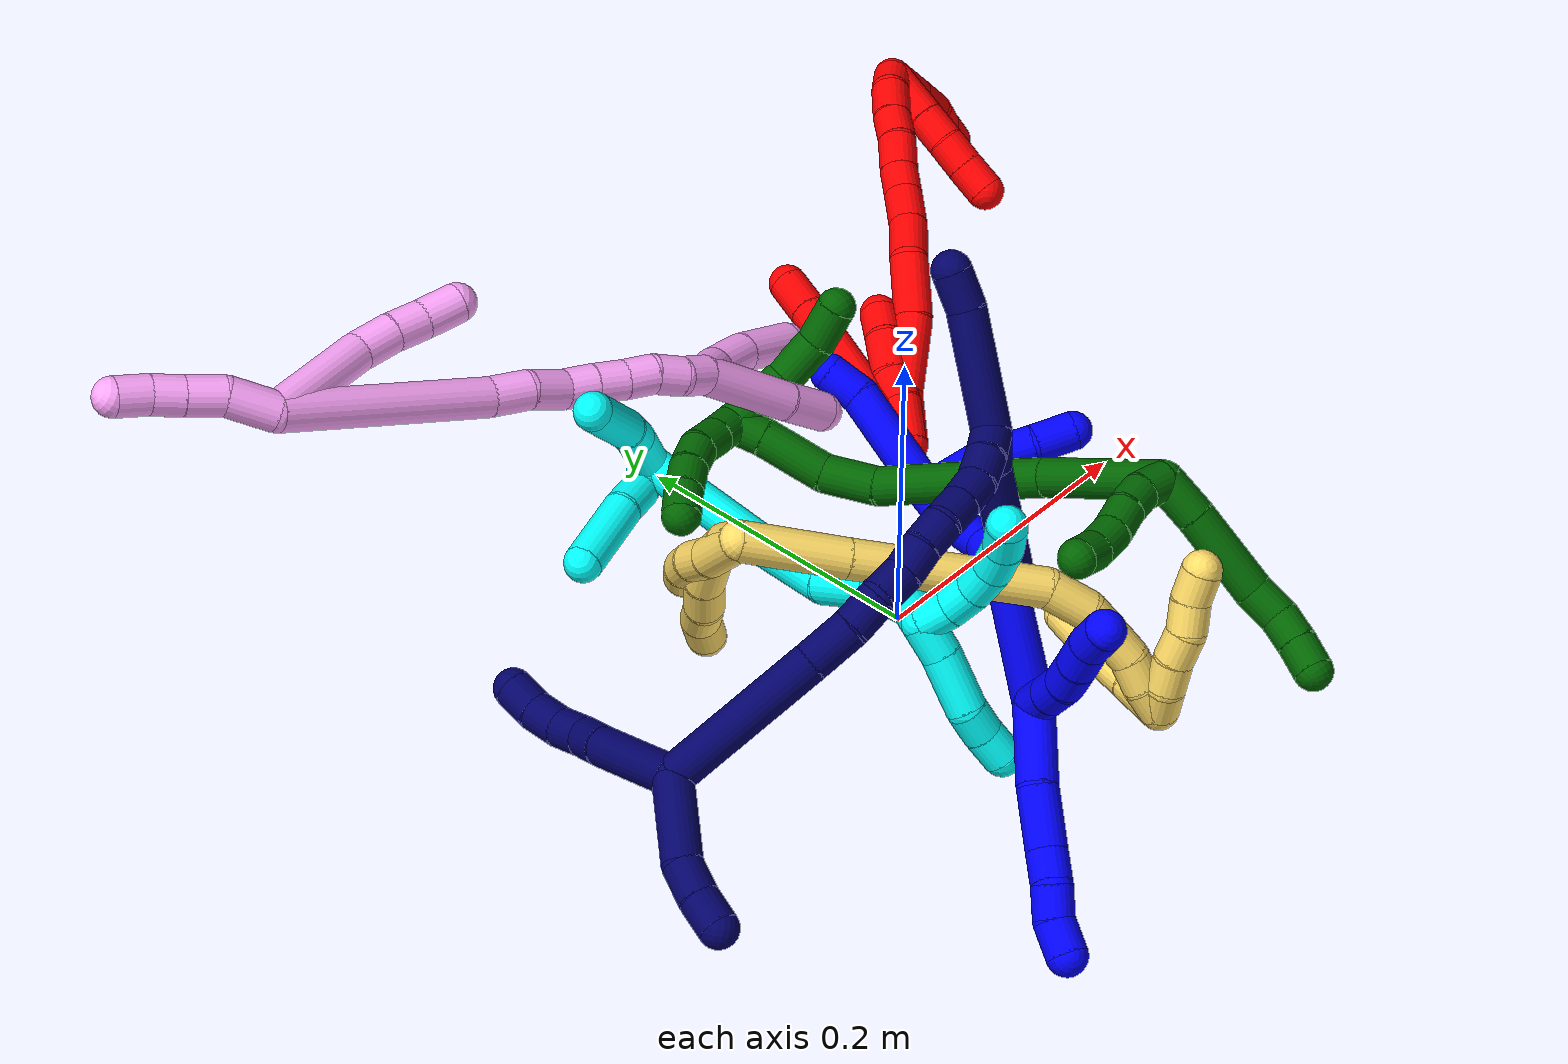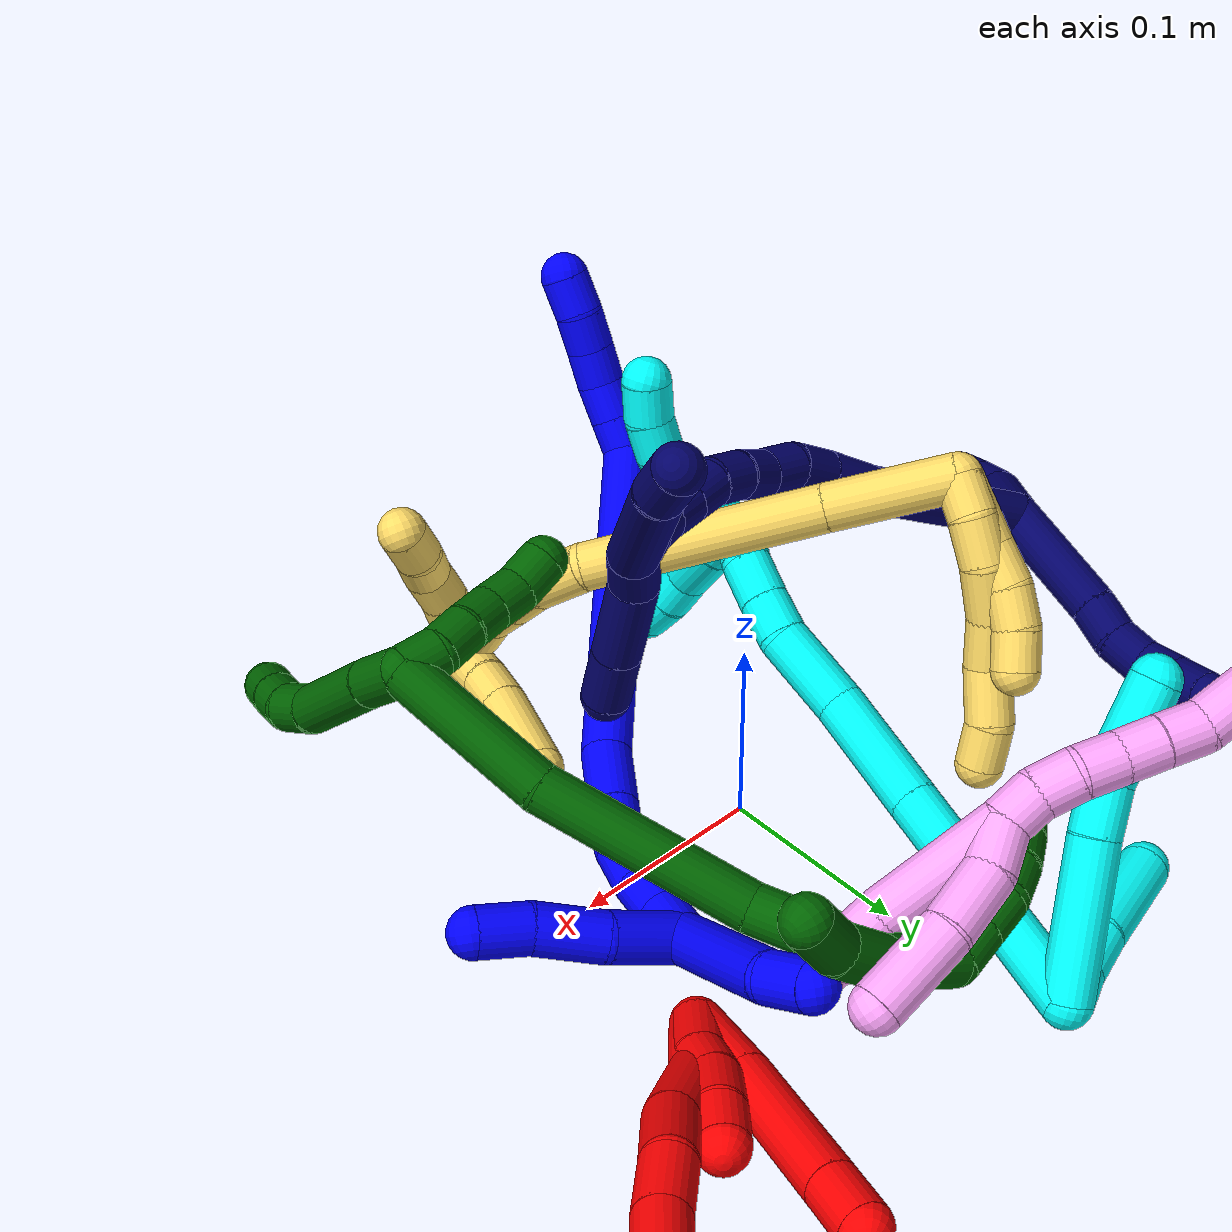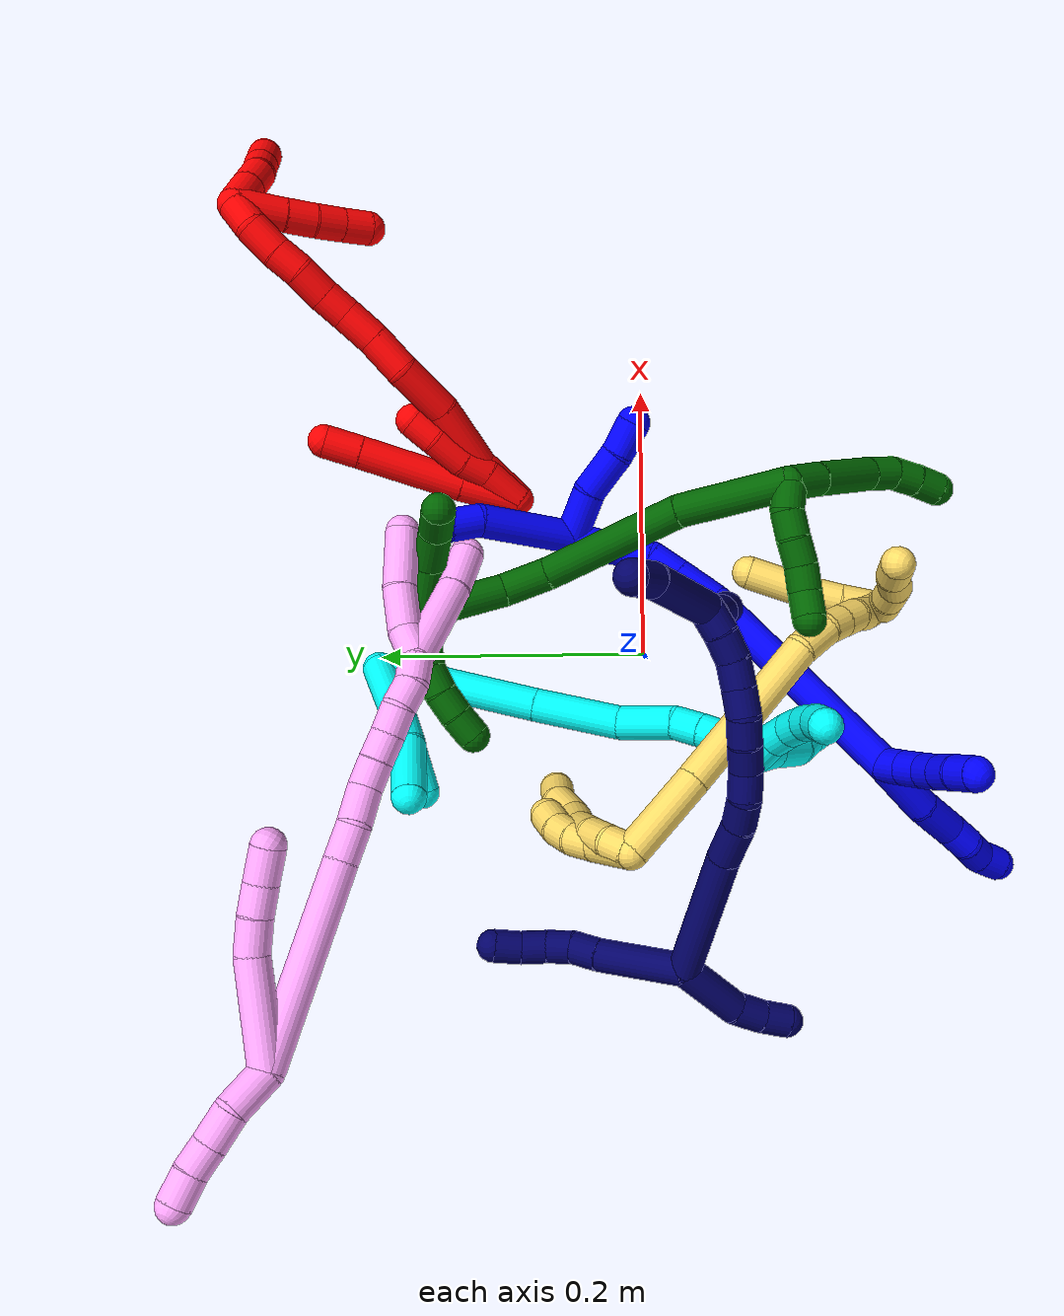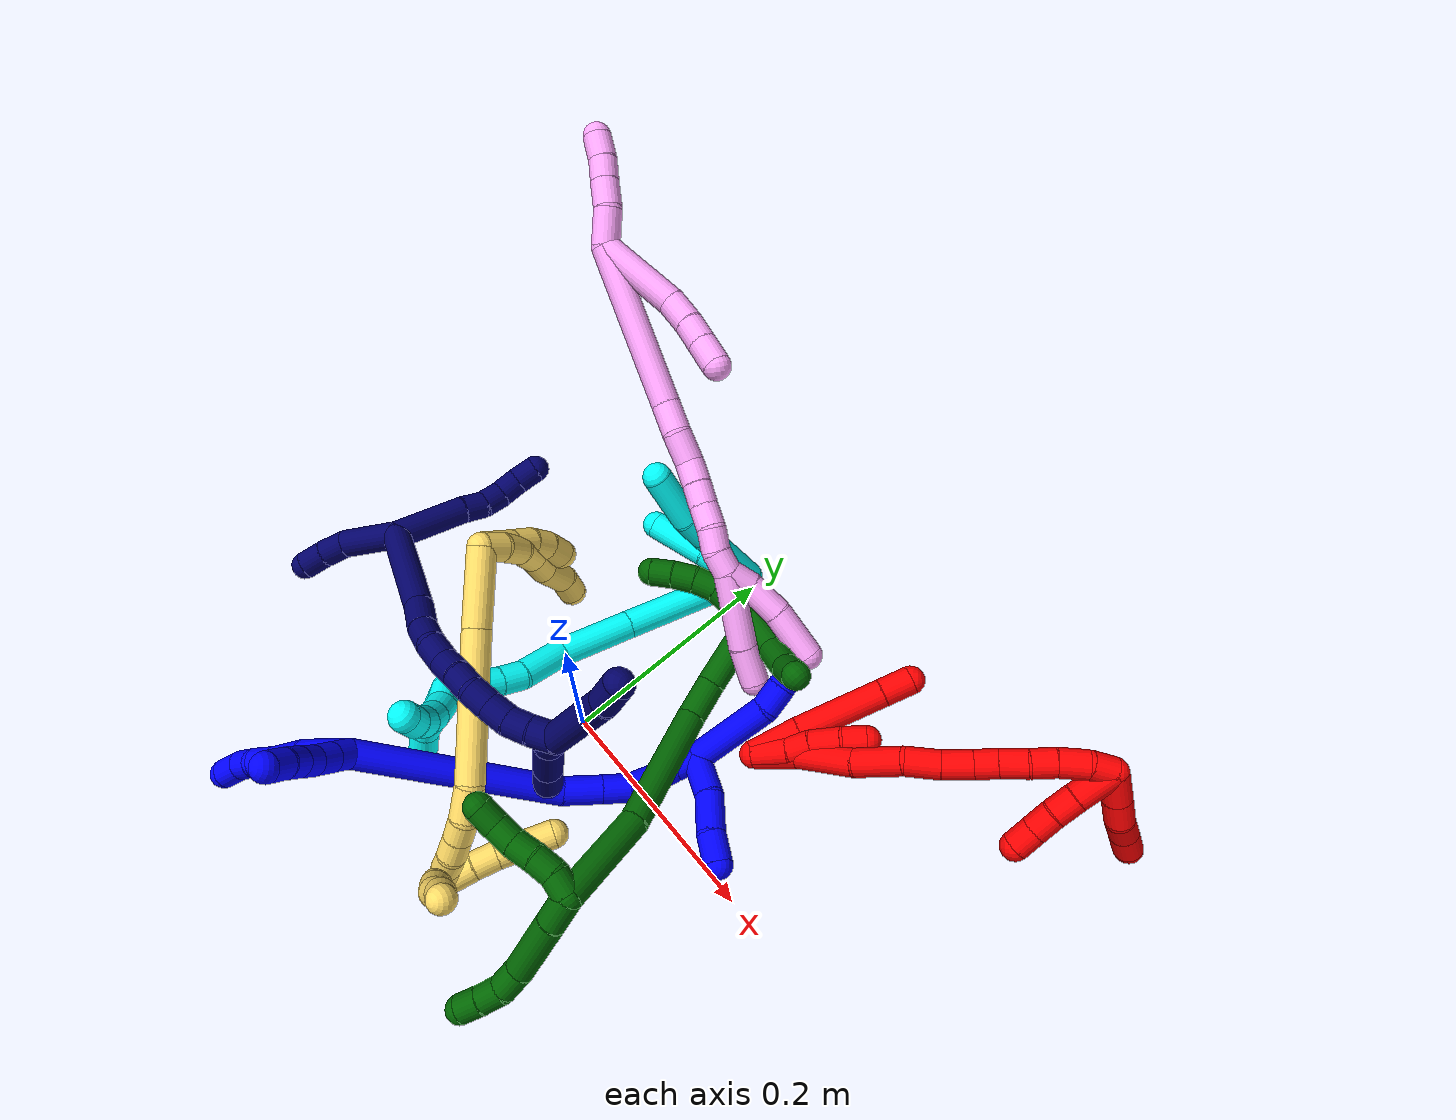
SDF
<sdf version="1.7">
 <world name="default">
  <plugin name="TubeGeneratorPlugin" filename="libtube_generator_plugin.so"/>
  <model name="photoneo_s_sensor">
   <static>1</static>
   <pose>0 0 2 1.57079 1.57079 3.14159</pose>
   <link name="link">
    <inertial><mass>0.1</mass></inertial>
    <sensor name="sensor" type="depth">
     <update_rate>30</update_rate>
     <camera>
      <horizontal_fov>1.22</horizontal_fov>
      <image><width>1920</width><height>1200</height><format>B8G8R8</format></image>
      <clip><near>0.1</near><far>4</far></clip>
      <depth_camera><output>points</output></depth_camera>
     </camera>
     <plugin name="camera_plugin" filename="libgazebo_ros_depth_camera.so">
      <baseline>0.2</baseline>
      <alwaysOn>1</alwaysOn>
      <updateRate>0.0</updateRate>
      <cameraName>camera_ir</cameraName>
      <imageTopicName>/camera/color/image_raw</imageTopicName>
      <cameraInfoTopicName>/camera/color/camera_info</cameraInfoTopicName>
      <depthImageTopicName>/camera/depth/image_raw</depthImageTopicName>
      <depthImageCameraInfoTopicName>/camera/depth/camera_info</depthImageCameraInfoTopicName>
      <pointCloudTopicName>/camera/depth/points</pointCloudTopicName>
      <frameName>fr_optical</frameName>
      <pointCloudCutoff>0.1</pointCloudCutoff>
      <pointCloudCutoffMax>2.0</pointCloudCutoffMax>
      <distortionK1>0</distortionK1>
      <distortionK2>0</distortionK2>
      <distortionK3>0</distortionK3>
      <distortionT1>0</distortionT1>
      <distortionT2>0</distortionT2>
      <CxPrime>0</CxPrime>
      <Cx>0</Cx>
      <Cy>0</Cy>
      <focalLength>0</focalLength>
      <hackBaseline>0</hackBaseline>
     </plugin>
    </sensor>
   </link>
  </model>
  <gravity>0 0 -9.8</gravity>
  <magnetic_field>6e-06 2.3e-05 -4.2e-05</magnetic_field>
  <atmosphere type="adiabatic"/>
  <physics name="default_physics" default="0" type="ode">
   <max_step_size>0.003</max_step_size>
   <real_time_factor>1</real_time_factor>
   <real_time_update_rate>1000</real_time_update_rate>
   <max_contacts>10000</max_contacts>
   <ode>
    <solver>
     <type>quick</type>
     <iters>100</iters>
     <sor>1.3</sor>
     <use_dynamic_moi_rescaling>0</use_dynamic_moi_rescaling>
    </solver>
    <constraints>
     <contact_max_correcting_vel>0</contact_max_correcting_vel>
     <contact_surface_layer>0.001</contact_surface_layer>
     <cfm>0</cfm>
     <erp>0.2</erp>
    </constraints>
   </ode>
  </physics>
  <scene><ambient>0.4 0.4 0.4 1</ambient><background>0.7 0.7 0.7 1</background><shadows>0</shadows></scene>
  <audio><device>default</device></audio>
  <spherical_coordinates>
   <surface_model>EARTH_WGS84</surface_model>
   <latitude_deg>0</latitude_deg>
   <longitude_deg>0</longitude_deg>
   <elevation>0</elevation>
   <heading_deg>0</heading_deg>
  </spherical_coordinates>
  <model name="bin">
   <static>1</static>
   <link name="bottom">
    <collision name="collision-bottom">
     <pose>0 0 -0.01 0 -0 0</pose>
     <geometry><box><size>0.8 0.6 0.02</size></box></geometry>
     <surface>
      <friction><ode><mu>100</mu><mu2>100</mu2></ode></friction>
      <contact><collide_bitmask>65535</collide_bitmask></contact>
     </surface>
    </collision>
   </link>
   <link name="west_wall">
    <collision name="collision-west_wall">
     <pose>-0.41 0 0.1 0 -0 0</pose>
     <geometry><box><size>0.02 0.6 0.2</size></box></geometry>
     <surface>
      <friction><ode><mu>100</mu><mu2>100</mu2></ode></friction>
      <contact><collide_bitmask>65535</collide_bitmask></contact>
     </surface>
    </collision>
   </link>
   <link name="east_wall">
    <collision name="collision-east_wall">
     <pose>0.41 0 0.1 0 -0 0</pose>
     <geometry><box><size>0.02 0.6 0.2</size></box></geometry>
     <surface>
      <friction><ode><mu>100</mu><mu2>100</mu2></ode></friction>
      <contact><collide_bitmask>65535</collide_bitmask></contact>
     </surface>
    </collision>
   </link>
   <link name="south_wall">
    <collision name="collision-south_wall">
     <pose>0 -0.31 0.1 0 -0 0</pose>
     <geometry><box><size>0.8 0.02 0.2</size></box></geometry>
     <surface>
      <friction><ode><mu>100</mu><mu2>100</mu2></ode></friction>
      <contact><collide_bitmask>65535</collide_bitmask></contact>
     </surface>
    </collision>
   </link>
   <link name="north_wall">
    <collision name="collision-north_wall">
     <pose>0 0.31 0.1 0 -0 0</pose>
     <geometry><box><size>0.8 0.02 0.2</size></box></geometry>
     <surface>
      <friction><ode><mu>100</mu><mu2>100</mu2></ode></friction>
      <contact><collide_bitmask>65535</collide_bitmask></contact>
     </surface>
    </collision>
   </link>
  </model>
  <model name="1">
   <static>0</static>
   <link name="1">
    <collision name="collision-cylinder-e_1_2_8">
     <pose>-0.020816 -0.01195 0.006282 1.08681 -0.995417 -0.634262</pose>
     <geometry><cylinder><radius>0.0125</radius><length>0.049622</length></cylinder></geometry>
     <surface>
      <friction><ode><mu>1.16</mu><mu2>1.16</mu2><slip1>0</slip1><slip2>0</slip2></ode></friction>
      <contact><ode><kp>1e+06</kp><kd>1</kd><max_vel>0</max_vel><min_depth>0.001</min_depth></ode></contact>
     </surface>
    </collision>
    <visual name="visual-cylinder-e_1_2_8">
     <pose>-0.020816 -0.01195 0.006282 1.08681 -0.995417 -0.634262</pose>
     <geometry><cylinder><radius>0.0125</radius><length>0.049622</length></cylinder></geometry>
     <material><ambient>0 0 1 1</ambient></material>
    </visual>
    <collision name="collision-cylinder-e_2_8_9">
     <pose>-0.056564 -0.03551 0.014994 1.36452 -0.899516 -0.747517</pose>
     <geometry><cylinder><radius>0.0125</radius><length>0.038139</length></cylinder></geometry>
     <surface>
      <friction><ode><mu>1.16</mu><mu2>1.16</mu2><slip1>0</slip1><slip2>0</slip2></ode></friction>
      <contact><ode><kp>1e+06</kp><kd>1</kd><max_vel>0</max_vel><min_depth>0.001</min_depth></ode></contact>
     </surface>
    </collision>
    <visual name="visual-cylinder-e_2_8_9">
     <pose>-0.056564 -0.03551 0.014994 1.36452 -0.899516 -0.747517</pose>
     <geometry><cylinder><radius>0.0125</radius><length>0.038139</length></cylinder></geometry>
     <material><ambient>0 0 1 1</ambient></material>
    </visual>
    <collision name="collision-cylinder-e_3_9_10">
     <pose>-0.079555 -0.052562 0.021198 0.964293 -0.882879 -0.484872</pose>
     <geometry><cylinder><radius>0.0125</radius><length>0.020864</length></cylinder></geometry>
     <surface>
      <friction><ode><mu>1.16</mu><mu2>1.16</mu2><slip1>0</slip1><slip2>0</slip2></ode></friction>
      <contact><ode><kp>1e+06</kp><kd>1</kd><max_vel>0</max_vel><min_depth>0.001</min_depth></ode></contact>
     </surface>
    </collision>
    <visual name="visual-cylinder-e_3_9_10">
     <pose>-0.079555 -0.052562 0.021198 0.964293 -0.882879 -0.484872</pose>
     <geometry><cylinder><radius>0.0125</radius><length>0.020864</length></cylinder></geometry>
     <material><ambient>0 0 1 1</ambient></material>
    </visual>
    <collision name="collision-cylinder-e_4_10_11">
     <pose>-0.095908 -0.063667 0.025447 1.48746 -0.970087 -0.902912</pose>
     <geometry><cylinder><radius>0.0125</radius><length>0.020106</length></cylinder></geometry>
     <surface>
      <friction><ode><mu>1.16</mu><mu2>1.16</mu2><slip1>0</slip1><slip2>0</slip2></ode></friction>
      <contact><ode><kp>1e+06</kp><kd>1</kd><max_vel>0</max_vel><min_depth>0.001</min_depth></ode></contact>
     </surface>
    </collision>
    <visual name="visual-cylinder-e_4_10_11">
     <pose>-0.095908 -0.063667 0.025447 1.48746 -0.970087 -0.902912</pose>
     <geometry><cylinder><radius>0.0125</radius><length>0.020106</length></cylinder></geometry>
     <material><ambient>0 0 1 1</ambient></material>
    </visual>
    <collision name="collision-cylinder-e_5_11_6">
     <pose>-0.110945 -0.077295 0.027959 1.32022 -0.686901 -0.541593</pose>
     <geometry><cylinder><radius>0.0125</radius><length>0.021269</length></cylinder></geometry>
     <surface>
      <friction><ode><mu>1.16</mu><mu2>1.16</mu2><slip1>0</slip1><slip2>0</slip2></ode></friction>
      <contact><ode><kp>1e+06</kp><kd>1</kd><max_vel>0</max_vel><min_depth>0.001</min_depth></ode></contact>
     </surface>
    </collision>
    <visual name="visual-cylinder-e_5_11_6">
     <pose>-0.110945 -0.077295 0.027959 1.32022 -0.686901 -0.541593</pose>
     <geometry><cylinder><radius>0.0125</radius><length>0.021269</length></cylinder></geometry>
     <material><ambient>0 0 1 1</ambient></material>
    </visual>
    <collision name="collision-cylinder-e_1_2_12">
     <pose>0.002844 -0.000401 0.009579 0.041793 0.288351 0.006068</pose>
     <geometry><cylinder><radius>0.0125</radius><length>0.02</length></cylinder></geometry>
     <surface>
      <friction><ode><mu>1.16</mu><mu2>1.16</mu2><slip1>0</slip1><slip2>0</slip2></ode></friction>
      <contact><ode><kp>1e+06</kp><kd>1</kd><max_vel>0</max_vel><min_depth>0.001</min_depth></ode></contact>
     </surface>
    </collision>
    <visual name="visual-cylinder-e_1_2_12">
     <pose>0.002844 -0.000401 0.009579 0.041793 0.288351 0.006068</pose>
     <geometry><cylinder><radius>0.0125</radius><length>0.02</length></cylinder></geometry>
     <material><ambient>0 0 1 1</ambient></material>
    </visual>
    <collision name="collision-cylinder-e_2_12_13">
     <pose>0.008778 -0.00099 0.028666 0.019894 0.31421 0.003152</pose>
     <geometry><cylinder><radius>0.0125</radius><length>0.02</length></cylinder></geometry>
     <surface>
      <friction><ode><mu>1.16</mu><mu2>1.16</mu2><slip1>0</slip1><slip2>0</slip2></ode></friction>
      <contact><ode><kp>1e+06</kp><kd>1</kd><max_vel>0</max_vel><min_depth>0.001</min_depth></ode></contact>
     </surface>
    </collision>
    <visual name="visual-cylinder-e_2_12_13">
     <pose>0.008778 -0.00099 0.028666 0.019894 0.31421 0.003152</pose>
     <geometry><cylinder><radius>0.0125</radius><length>0.02</length></cylinder></geometry>
     <material><ambient>0 0 1 1</ambient></material>
    </visual>
    <collision name="collision-cylinder-e_3_13_14">
     <pose>0.016094 0.000337 0.04711 -0.168144 0.436279 -0.037356</pose>
     <geometry><cylinder><radius>0.0125</radius><length>0.02</length></cylinder></geometry>
     <surface>
      <friction><ode><mu>1.16</mu><mu2>1.16</mu2><slip1>0</slip1><slip2>0</slip2></ode></friction>
      <contact><ode><kp>1e+06</kp><kd>1</kd><max_vel>0</max_vel><min_depth>0.001</min_depth></ode></contact>
     </surface>
    </collision>
    <visual name="visual-cylinder-e_3_13_14">
     <pose>0.016094 0.000337 0.04711 -0.168144 0.436279 -0.037356</pose>
     <geometry><cylinder><radius>0.0125</radius><length>0.02</length></cylinder></geometry>
     <material><ambient>0 0 1 1</ambient></material>
    </visual>
    <collision name="collision-cylinder-e_4_14_15">
     <pose>0.025091 0.003599 0.064659 -0.199843 0.49736 -0.050906</pose>
     <geometry><cylinder><radius>0.0125</radius><length>0.02</length></cylinder></geometry>
     <surface>
      <friction><ode><mu>1.16</mu><mu2>1.16</mu2><slip1>0</slip1><slip2>0</slip2></ode></friction>
      <contact><ode><kp>1e+06</kp><kd>1</kd><max_vel>0</max_vel><min_depth>0.001</min_depth></ode></contact>
     </surface>
    </collision>
    <visual name="visual-cylinder-e_4_14_15">
     <pose>0.025091 0.003599 0.064659 -0.199843 0.49736 -0.050906</pose>
     <geometry><cylinder><radius>0.0125</radius><length>0.02</length></cylinder></geometry>
     <material><ambient>0 0 1 1</ambient></material>
    </visual>
    <collision name="collision-cylinder-e_5_15_5">
     <pose>0.033633 0.005556 0.082532 -0.023007 0.386652 -0.004504</pose>
     <geometry><cylinder><radius>0.0125</radius><length>0.02</length></cylinder></geometry>
     <surface>
      <friction><ode><mu>1.16</mu><mu2>1.16</mu2><slip1>0</slip1><slip2>0</slip2></ode></friction>
      <contact><ode><kp>1e+06</kp><kd>1</kd><max_vel>0</max_vel><min_depth>0.001</min_depth></ode></contact>
     </surface>
    </collision>
    <visual name="visual-cylinder-e_5_15_5">
     <pose>0.033633 0.005556 0.082532 -0.023007 0.386652 -0.004504</pose>
     <geometry><cylinder><radius>0.0125</radius><length>0.02</length></cylinder></geometry>
     <material><ambient>0 0 1 1</ambient></material>
    </visual>
    <collision name="collision-cylinder-e_1_2_16">
     <pose>0.042117 0.008408 -0.078242 -3.03454 0.491415 -2.72064</pose>
     <geometry><cylinder><radius>0.0125</radius><length>0.178508</length></cylinder></geometry>
     <surface>
      <friction><ode><mu>1.16</mu><mu2>1.16</mu2><slip1>0</slip1><slip2>0</slip2></ode></friction>
      <contact><ode><kp>1e+06</kp><kd>1</kd><max_vel>0</max_vel><min_depth>0.001</min_depth></ode></contact>
     </surface>
    </collision>
    <visual name="visual-cylinder-e_1_2_16">
     <pose>0.042117 0.008408 -0.078242 -3.03454 0.491415 -2.72064</pose>
     <geometry><cylinder><radius>0.0125</radius><length>0.178508</length></cylinder></geometry>
     <material><ambient>0 0 1 1</ambient></material>
    </visual>
    <collision name="collision-cylinder-e_2_16_17">
     <pose>0.092633 0.022643 -0.169967 -2.73364 0.51943 -1.81864</pose>
     <geometry><cylinder><radius>0.0125</radius><length>0.033842</length></cylinder></geometry>
     <surface>
      <friction><ode><mu>1.16</mu><mu2>1.16</mu2><slip1>0</slip1><slip2>0</slip2></ode></friction>
      <contact><ode><kp>1e+06</kp><kd>1</kd><max_vel>0</max_vel><min_depth>0.001</min_depth></ode></contact>
     </surface>
    </collision>
    <visual name="visual-cylinder-e_2_16_17">
     <pose>0.092633 0.022643 -0.169967 -2.73364 0.51943 -1.81864</pose>
     <geometry><cylinder><radius>0.0125</radius><length>0.033842</length></cylinder></geometry>
     <material><ambient>0 0 1 1</ambient></material>
    </visual>
    <collision name="collision-cylinder-e_3_17_18">
     <pose>0.106975 0.032875 -0.193073 -2.71232 0.511703 -1.7521</pose>
     <geometry><cylinder><radius>0.0125</radius><length>0.024274</length></cylinder></geometry>
     <surface>
      <friction><ode><mu>1.16</mu><mu2>1.16</mu2><slip1>0</slip1><slip2>0</slip2></ode></friction>
      <contact><ode><kp>1e+06</kp><kd>1</kd><max_vel>0</max_vel><min_depth>0.001</min_depth></ode></contact>
     </surface>
    </collision>
    <visual name="visual-cylinder-e_3_17_18">
     <pose>0.106975 0.032875 -0.193073 -2.71232 0.511703 -1.7521</pose>
     <geometry><cylinder><radius>0.0125</radius><length>0.024274</length></cylinder></geometry>
     <material><ambient>0 0 1 1</ambient></material>
    </visual>
    <collision name="collision-cylinder-e_4_18_19">
     <pose>0.11516 0.042855 -0.211262 -2.56463 0.215937 -0.700378</pose>
     <geometry><cylinder><radius>0.0125</radius><length>0.020929</length></cylinder></geometry>
     <surface>
      <friction><ode><mu>1.16</mu><mu2>1.16</mu2><slip1>0</slip1><slip2>0</slip2></ode></friction>
      <contact><ode><kp>1e+06</kp><kd>1</kd><max_vel>0</max_vel><min_depth>0.001</min_depth></ode></contact>
     </surface>
    </collision>
    <visual name="visual-cylinder-e_4_18_19">
     <pose>0.11516 0.042855 -0.211262 -2.56463 0.215937 -0.700378</pose>
     <geometry><cylinder><radius>0.0125</radius><length>0.020929</length></cylinder></geometry>
     <material><ambient>0 0 1 1</ambient></material>
    </visual>
    <collision name="collision-cylinder-e_5_19_20">
     <pose>0.120221 0.055871 -0.22712 -2.34608 0.264283 -0.612783</pose>
     <geometry><cylinder><radius>0.0125</radius><length>0.021584</length></cylinder></geometry>
     <surface>
      <friction><ode><mu>1.16</mu><mu2>1.16</mu2><slip1>0</slip1><slip2>0</slip2></ode></friction>
      <contact><ode><kp>1e+06</kp><kd>1</kd><max_vel>0</max_vel><min_depth>0.001</min_depth></ode></contact>
     </surface>
    </collision>
    <visual name="visual-cylinder-e_5_19_20">
     <pose>0.120221 0.055871 -0.22712 -2.34608 0.264283 -0.612783</pose>
     <geometry><cylinder><radius>0.0125</radius><length>0.021584</length></cylinder></geometry>
     <material><ambient>0 0 1 1</ambient></material>
    </visual>
    <collision name="collision-cylinder-e_6_20_1">
     <pose>0.127133 0.070546 -0.240715 -2.28753 0.403139 -0.844168</pose>
     <geometry><cylinder><radius>0.0125</radius><length>0.020864</length></cylinder></geometry>
     <surface>
      <friction><ode><mu>1.16</mu><mu2>1.16</mu2><slip1>0</slip1><slip2>0</slip2></ode></friction>
      <contact><ode><kp>1e+06</kp><kd>1</kd><max_vel>0</max_vel><min_depth>0.001</min_depth></ode></contact>
     </surface>
    </collision>
    <visual name="visual-cylinder-e_6_20_1">
     <pose>0.127133 0.070546 -0.240715 -2.28753 0.403139 -0.844168</pose>
     <geometry><cylinder><radius>0.0125</radius><length>0.020864</length></cylinder></geometry>
     <material><ambient>0 0 1 1</ambient></material>
    </visual>
    <collision name="collision-cylinder-e_1_1_21">
     <pose>0.148344 0.069333 -0.243572 1.18349 1.08112 0.766838</pose>
     <geometry><cylinder><radius>0.0125</radius><length>0.038797</length></cylinder></geometry>
     <surface>
      <friction><ode><mu>1.16</mu><mu2>1.16</mu2><slip1>0</slip1><slip2>0</slip2></ode></friction>
      <contact><ode><kp>1e+06</kp><kd>1</kd><max_vel>0</max_vel><min_depth>0.001</min_depth></ode></contact>
     </surface>
    </collision>
    <visual name="visual-cylinder-e_1_1_21">
     <pose>0.148344 0.069333 -0.243572 1.18349 1.08112 0.766838</pose>
     <geometry><cylinder><radius>0.0125</radius><length>0.038797</length></cylinder></geometry>
     <material><ambient>0 0 1 1</ambient></material>
    </visual>
    <collision name="collision-cylinder-e_2_21_22">
     <pose>0.178145 0.049996 -0.235043 1.13406 0.812347 0.534641</pose>
     <geometry><cylinder><radius>0.0125</radius><length>0.034941</length></cylinder></geometry>
     <surface>
      <friction><ode><mu>1.16</mu><mu2>1.16</mu2><slip1>0</slip1><slip2>0</slip2></ode></friction>
      <contact><ode><kp>1e+06</kp><kd>1</kd><max_vel>0</max_vel><min_depth>0.001</min_depth></ode></contact>
     </surface>
    </collision>
    <visual name="visual-cylinder-e_2_21_22">
     <pose>0.178145 0.049996 -0.235043 1.13406 0.812347 0.534641</pose>
     <geometry><cylinder><radius>0.0125</radius><length>0.034941</length></cylinder></geometry>
     <material><ambient>0 0 1 1</ambient></material>
    </visual>
    <collision name="collision-cylinder-e_3_22_4">
     <pose>0.201114 0.031056 -0.228628 1.4068 0.900116 0.777765</pose>
     <geometry><cylinder><radius>0.0125</radius><length>0.026262</length></cylinder></geometry>
     <surface>
      <friction><ode><mu>1.16</mu><mu2>1.16</mu2><slip1>0</slip1><slip2>0</slip2></ode></friction>
      <contact><ode><kp>1e+06</kp><kd>1</kd><max_vel>0</max_vel><min_depth>0.001</min_depth></ode></contact>
     </surface>
    </collision>
    <visual name="visual-cylinder-e_3_22_4">
     <pose>0.201114 0.031056 -0.228628 1.4068 0.900116 0.777765</pose>
     <geometry><cylinder><radius>0.0125</radius><length>0.026262</length></cylinder></geometry>
     <material><ambient>0 0 1 1</ambient></material>
    </visual>
    <collision name="collision-cylinder-e_1_1_23">
     <pose>0.147457 0.110552 -0.256669 -1.8572 0.443542 -0.585587</pose>
     <geometry><cylinder><radius>0.0125</radius><length>0.075646</length></cylinder></geometry>
     <surface>
      <friction><ode><mu>1.16</mu><mu2>1.16</mu2><slip1>0</slip1><slip2>0</slip2></ode></friction>
      <contact><ode><kp>1e+06</kp><kd>1</kd><max_vel>0</max_vel><min_depth>0.001</min_depth></ode></contact>
     </surface>
    </collision>
    <visual name="visual-cylinder-e_1_1_23">
     <pose>0.147457 0.110552 -0.256669 -1.8572 0.443542 -0.585587</pose>
     <geometry><cylinder><radius>0.0125</radius><length>0.075646</length></cylinder></geometry>
     <material><ambient>0 0 1 1</ambient></material>
    </visual>
    <collision name="collision-cylinder-e_2_23_3">
     <pose>0.165041 0.155101 -0.269105 -1.80296 0.111346 -0.140654</pose>
     <geometry><cylinder><radius>0.0125</radius><length>0.024354</length></cylinder></geometry>
     <surface>
      <friction><ode><mu>1.16</mu><mu2>1.16</mu2><slip1>0</slip1><slip2>0</slip2></ode></friction>
      <contact><ode><kp>1e+06</kp><kd>1</kd><max_vel>0</max_vel><min_depth>0.001</min_depth></ode></contact>
     </surface>
    </collision>
    <visual name="visual-cylinder-e_2_23_3">
     <pose>0.165041 0.155101 -0.269105 -1.80296 0.111346 -0.140654</pose>
     <geometry><cylinder><radius>0.0125</radius><length>0.024354</length></cylinder></geometry>
     <material><ambient>0 0 1 1</ambient></material>
    </visual>
    <collision name="collision-sphere-3">
     <pose>0.166394 0.166878 -0.271889 0 -0 0</pose>
     <geometry><sphere><radius>0.0125</radius></sphere></geometry>
     <surface>
      <friction><ode><mu>1.16</mu><mu2>1.16</mu2><slip1>0</slip1><slip2>0</slip2></ode></friction>
      <contact><ode><kp>1e+06</kp><kd>1</kd><max_vel>0</max_vel><min_depth>0.001</min_depth></ode></contact>
     </surface>
    </collision>
    <visual name="visual-sphere-3">
     <pose>0.166394 0.166878 -0.271889 0 -0 0</pose>
     <geometry><sphere><radius>0.0125</radius></sphere></geometry>
     <material><ambient>0 0 1 1</ambient></material>
    </visual>
    <collision name="collision-sphere-23">
     <pose>0.163688 0.143324 -0.26632 0 -0 0</pose>
     <geometry><sphere><radius>0.0125</radius></sphere></geometry>
     <surface>
      <friction><ode><mu>1.16</mu><mu2>1.16</mu2><slip1>0</slip1><slip2>0</slip2></ode></friction>
      <contact><ode><kp>1e+06</kp><kd>1</kd><max_vel>0</max_vel><min_depth>0.001</min_depth></ode></contact>
     </surface>
    </collision>
    <visual name="visual-sphere-23">
     <pose>0.163688 0.143324 -0.26632 0 -0 0</pose>
     <geometry><sphere><radius>0.0125</radius></sphere></geometry>
     <material><ambient>0 0 1 1</ambient></material>
    </visual>
    <collision name="collision-sphere-4">
     <pose>0.211401 0.023005 -0.227296 0 -0 0</pose>
     <geometry><sphere><radius>0.0125</radius></sphere></geometry>
     <surface>
      <friction><ode><mu>1.16</mu><mu2>1.16</mu2><slip1>0</slip1><slip2>0</slip2></ode></friction>
      <contact><ode><kp>1e+06</kp><kd>1</kd><max_vel>0</max_vel><min_depth>0.001</min_depth></ode></contact>
     </surface>
    </collision>
    <visual name="visual-sphere-4">
     <pose>0.211401 0.023005 -0.227296 0 -0 0</pose>
     <geometry><sphere><radius>0.0125</radius></sphere></geometry>
     <material><ambient>0 0 1 1</ambient></material>
    </visual>
    <collision name="collision-sphere-22">
     <pose>0.190827 0.039108 -0.229961 0 -0 0</pose>
     <geometry><sphere><radius>0.0125</radius></sphere></geometry>
     <surface>
      <friction><ode><mu>1.16</mu><mu2>1.16</mu2><slip1>0</slip1><slip2>0</slip2></ode></friction>
      <contact><ode><kp>1e+06</kp><kd>1</kd><max_vel>0</max_vel><min_depth>0.001</min_depth></ode></contact>
     </surface>
    </collision>
    <visual name="visual-sphere-22">
     <pose>0.190827 0.039108 -0.229961 0 -0 0</pose>
     <geometry><sphere><radius>0.0125</radius></sphere></geometry>
     <material><ambient>0 0 1 1</ambient></material>
    </visual>
    <collision name="collision-sphere-21">
     <pose>0.165463 0.060885 -0.240126 0 -0 0</pose>
     <geometry><sphere><radius>0.0125</radius></sphere></geometry>
     <surface>
      <friction><ode><mu>1.16</mu><mu2>1.16</mu2><slip1>0</slip1><slip2>0</slip2></ode></friction>
      <contact><ode><kp>1e+06</kp><kd>1</kd><max_vel>0</max_vel><min_depth>0.001</min_depth></ode></contact>
     </surface>
    </collision>
    <visual name="visual-sphere-21">
     <pose>0.165463 0.060885 -0.240126 0 -0 0</pose>
     <geometry><sphere><radius>0.0125</radius></sphere></geometry>
     <material><ambient>0 0 1 1</ambient></material>
    </visual>
    <collision name="collision-sphere-1">
     <pose>0.131225 0.077781 -0.247018 0 -0 0</pose>
     <geometry><sphere><radius>0.0125</radius></sphere></geometry>
     <surface>
      <friction><ode><mu>1.16</mu><mu2>1.16</mu2><slip1>0</slip1><slip2>0</slip2></ode></friction>
      <contact><ode><kp>1e+06</kp><kd>1</kd><max_vel>0</max_vel><min_depth>0.001</min_depth></ode></contact>
     </surface>
    </collision>
    <visual name="visual-sphere-1">
     <pose>0.131225 0.077781 -0.247018 0 -0 0</pose>
     <geometry><sphere><radius>0.0125</radius></sphere></geometry>
     <material><ambient>0 0 1 1</ambient></material>
    </visual>
    <collision name="collision-sphere-6">
     <pose>-0.117689 -0.085261 0.029998 0 -0 0</pose>
     <geometry><sphere><radius>0.0125</radius></sphere></geometry>
     <surface>
      <friction><ode><mu>1.16</mu><mu2>1.16</mu2><slip1>0</slip1><slip2>0</slip2></ode></friction>
      <contact><ode><kp>1e+06</kp><kd>1</kd><max_vel>0</max_vel><min_depth>0.001</min_depth></ode></contact>
     </surface>
    </collision>
    <visual name="visual-sphere-6">
     <pose>-0.117689 -0.085261 0.029998 0 -0 0</pose>
     <geometry><sphere><radius>0.0125</radius></sphere></geometry>
     <material><ambient>0 0 1 1</ambient></material>
    </visual>
    <collision name="collision-sphere-11">
     <pose>-0.104201 -0.069329 0.02592 0 -0 0</pose>
     <geometry><sphere><radius>0.0125</radius></sphere></geometry>
     <surface>
      <friction><ode><mu>1.16</mu><mu2>1.16</mu2><slip1>0</slip1><slip2>0</slip2></ode></friction>
      <contact><ode><kp>1e+06</kp><kd>1</kd><max_vel>0</max_vel><min_depth>0.001</min_depth></ode></contact>
     </surface>
    </collision>
    <visual name="visual-sphere-11">
     <pose>-0.104201 -0.069329 0.02592 0 -0 0</pose>
     <geometry><sphere><radius>0.0125</radius></sphere></geometry>
     <material><ambient>0 0 1 1</ambient></material>
    </visual>
    <collision name="collision-sphere-10">
     <pose>-0.087615 -0.058004 0.024974 0 -0 0</pose>
     <geometry><sphere><radius>0.0125</radius></sphere></geometry>
     <surface>
      <friction><ode><mu>1.16</mu><mu2>1.16</mu2><slip1>0</slip1><slip2>0</slip2></ode></friction>
      <contact><ode><kp>1e+06</kp><kd>1</kd><max_vel>0</max_vel><min_depth>0.001</min_depth></ode></contact>
     </surface>
    </collision>
    <visual name="visual-sphere-10">
     <pose>-0.087615 -0.058004 0.024974 0 -0 0</pose>
     <geometry><sphere><radius>0.0125</radius></sphere></geometry>
     <material><ambient>0 0 1 1</ambient></material>
    </visual>
    <collision name="collision-sphere-9">
     <pose>-0.071495 -0.04712 0.017423 0 -0 0</pose>
     <geometry><sphere><radius>0.0125</radius></sphere></geometry>
     <surface>
      <friction><ode><mu>1.16</mu><mu2>1.16</mu2><slip1>0</slip1><slip2>0</slip2></ode></friction>
      <contact><ode><kp>1e+06</kp><kd>1</kd><max_vel>0</max_vel><min_depth>0.001</min_depth></ode></contact>
     </surface>
    </collision>
    <visual name="visual-sphere-9">
     <pose>-0.071495 -0.04712 0.017423 0 -0 0</pose>
     <geometry><sphere><radius>0.0125</radius></sphere></geometry>
     <material><ambient>0 0 1 1</ambient></material>
    </visual>
    <collision name="collision-sphere-2">
     <geometry><sphere><radius>0.0125</radius></sphere></geometry>
     <surface>
      <friction><ode><mu>1.16</mu><mu2>1.16</mu2><slip1>0</slip1><slip2>0</slip2></ode></friction>
      <contact><ode><kp>1e+06</kp><kd>1</kd><max_vel>0</max_vel><min_depth>0.001</min_depth></ode></contact>
     </surface>
    </collision>
    <visual name="visual-sphere-2">
     <geometry><sphere><radius>0.0125</radius></sphere></geometry>
     <material><ambient>0 0 1 1</ambient></material>
    </visual>
    <collision name="collision-sphere-19">
     <pose>0.117402 0.048431 -0.219828 0 -0 0</pose>
     <geometry><sphere><radius>0.0125</radius></sphere></geometry>
     <surface>
      <friction><ode><mu>1.16</mu><mu2>1.16</mu2><slip1>0</slip1><slip2>0</slip2></ode></friction>
      <contact><ode><kp>1e+06</kp><kd>1</kd><max_vel>0</max_vel><min_depth>0.001</min_depth></ode></contact>
     </surface>
    </collision>
    <visual name="visual-sphere-19">
     <pose>0.117402 0.048431 -0.219828 0 -0 0</pose>
     <geometry><sphere><radius>0.0125</radius></sphere></geometry>
     <material><ambient>0 0 1 1</ambient></material>
    </visual>
    <collision name="collision-sphere-8">
     <pose>-0.041632 -0.023901 0.012564 0 -0 0</pose>
     <geometry><sphere><radius>0.0125</radius></sphere></geometry>
     <surface>
      <friction><ode><mu>1.16</mu><mu2>1.16</mu2><slip1>0</slip1><slip2>0</slip2></ode></friction>
      <contact><ode><kp>1e+06</kp><kd>1</kd><max_vel>0</max_vel><min_depth>0.001</min_depth></ode></contact>
     </surface>
    </collision>
    <visual name="visual-sphere-8">
     <pose>-0.041632 -0.023901 0.012564 0 -0 0</pose>
     <geometry><sphere><radius>0.0125</radius></sphere></geometry>
     <material><ambient>0 0 1 1</ambient></material>
    </visual>
    <collision name="collision-sphere-12">
     <pose>0.005687 -0.000801 0.019158 0 -0 0</pose>
     <geometry><sphere><radius>0.0125</radius></sphere></geometry>
     <surface>
      <friction><ode><mu>1.16</mu><mu2>1.16</mu2><slip1>0</slip1><slip2>0</slip2></ode></friction>
      <contact><ode><kp>1e+06</kp><kd>1</kd><max_vel>0</max_vel><min_depth>0.001</min_depth></ode></contact>
     </surface>
    </collision>
    <visual name="visual-sphere-12">
     <pose>0.005687 -0.000801 0.019158 0 -0 0</pose>
     <geometry><sphere><radius>0.0125</radius></sphere></geometry>
     <material><ambient>0 0 1 1</ambient></material>
    </visual>
    <collision name="collision-sphere-13">
     <pose>0.011869 -0.001179 0.038175 0 -0 0</pose>
     <geometry><sphere><radius>0.0125</radius></sphere></geometry>
     <surface>
      <friction><ode><mu>1.16</mu><mu2>1.16</mu2><slip1>0</slip1><slip2>0</slip2></ode></friction>
      <contact><ode><kp>1e+06</kp><kd>1</kd><max_vel>0</max_vel><min_depth>0.001</min_depth></ode></contact>
     </surface>
    </collision>
    <visual name="visual-sphere-13">
     <pose>0.011869 -0.001179 0.038175 0 -0 0</pose>
     <geometry><sphere><radius>0.0125</radius></sphere></geometry>
     <material><ambient>0 0 1 1</ambient></material>
    </visual>
    <collision name="collision-sphere-14">
     <pose>0.02032 0.001854 0.056046 0 -0 0</pose>
     <geometry><sphere><radius>0.0125</radius></sphere></geometry>
     <surface>
      <friction><ode><mu>1.16</mu><mu2>1.16</mu2><slip1>0</slip1><slip2>0</slip2></ode></friction>
      <contact><ode><kp>1e+06</kp><kd>1</kd><max_vel>0</max_vel><min_depth>0.001</min_depth></ode></contact>
     </surface>
    </collision>
    <visual name="visual-sphere-14">
     <pose>0.02032 0.001854 0.056046 0 -0 0</pose>
     <geometry><sphere><radius>0.0125</radius></sphere></geometry>
     <material><ambient>0 0 1 1</ambient></material>
    </visual>
    <collision name="collision-sphere-15">
     <pose>0.029862 0.005343 0.073273 0 -0 0</pose>
     <geometry><sphere><radius>0.0125</radius></sphere></geometry>
     <surface>
      <friction><ode><mu>1.16</mu><mu2>1.16</mu2><slip1>0</slip1><slip2>0</slip2></ode></friction>
      <contact><ode><kp>1e+06</kp><kd>1</kd><max_vel>0</max_vel><min_depth>0.001</min_depth></ode></contact>
     </surface>
    </collision>
    <visual name="visual-sphere-15">
     <pose>0.029862 0.005343 0.073273 0 -0 0</pose>
     <geometry><sphere><radius>0.0125</radius></sphere></geometry>
     <material><ambient>0 0 1 1</ambient></material>
    </visual>
    <collision name="collision-sphere-5">
     <pose>0.037404 0.005769 0.091791 0 -0 0</pose>
     <geometry><sphere><radius>0.0125</radius></sphere></geometry>
     <surface>
      <friction><ode><mu>1.16</mu><mu2>1.16</mu2><slip1>0</slip1><slip2>0</slip2></ode></friction>
      <contact><ode><kp>1e+06</kp><kd>1</kd><max_vel>0</max_vel><min_depth>0.001</min_depth></ode></contact>
     </surface>
    </collision>
    <visual name="visual-sphere-5">
     <pose>0.037404 0.005769 0.091791 0 -0 0</pose>
     <geometry><sphere><radius>0.0125</radius></sphere></geometry>
     <material><ambient>0 0 1 1</ambient></material>
    </visual>
    <collision name="collision-sphere-16">
     <pose>0.084233 0.016816 -0.156483 0 -0 0</pose>
     <geometry><sphere><radius>0.0125</radius></sphere></geometry>
     <surface>
      <friction><ode><mu>1.16</mu><mu2>1.16</mu2><slip1>0</slip1><slip2>0</slip2></ode></friction>
      <contact><ode><kp>1e+06</kp><kd>1</kd><max_vel>0</max_vel><min_depth>0.001</min_depth></ode></contact>
     </surface>
    </collision>
    <visual name="visual-sphere-16">
     <pose>0.084233 0.016816 -0.156483 0 -0 0</pose>
     <geometry><sphere><radius>0.0125</radius></sphere></geometry>
     <material><ambient>0 0 1 1</ambient></material>
    </visual>
    <collision name="collision-sphere-17">
     <pose>0.101032 0.028471 -0.183451 0 -0 0</pose>
     <geometry><sphere><radius>0.0125</radius></sphere></geometry>
     <surface>
      <friction><ode><mu>1.16</mu><mu2>1.16</mu2><slip1>0</slip1><slip2>0</slip2></ode></friction>
      <contact><ode><kp>1e+06</kp><kd>1</kd><max_vel>0</max_vel><min_depth>0.001</min_depth></ode></contact>
     </surface>
    </collision>
    <visual name="visual-sphere-17">
     <pose>0.101032 0.028471 -0.183451 0 -0 0</pose>
     <geometry><sphere><radius>0.0125</radius></sphere></geometry>
     <material><ambient>0 0 1 1</ambient></material>
    </visual>
    <collision name="collision-sphere-18">
     <pose>0.112918 0.03728 -0.202695 0 -0 0</pose>
     <geometry><sphere><radius>0.0125</radius></sphere></geometry>
     <surface>
      <friction><ode><mu>1.16</mu><mu2>1.16</mu2><slip1>0</slip1><slip2>0</slip2></ode></friction>
      <contact><ode><kp>1e+06</kp><kd>1</kd><max_vel>0</max_vel><min_depth>0.001</min_depth></ode></contact>
     </surface>
    </collision>
    <visual name="visual-sphere-18">
     <pose>0.112918 0.03728 -0.202695 0 -0 0</pose>
     <geometry><sphere><radius>0.0125</radius></sphere></geometry>
     <material><ambient>0 0 1 1</ambient></material>
    </visual>
    <collision name="collision-sphere-20">
     <pose>0.12304 0.063311 -0.234411 0 -0 0</pose>
     <geometry><sphere><radius>0.0125</radius></sphere></geometry>
     <surface>
      <friction><ode><mu>1.16</mu><mu2>1.16</mu2><slip1>0</slip1><slip2>0</slip2></ode></friction>
      <contact><ode><kp>1e+06</kp><kd>1</kd><max_vel>0</max_vel><min_depth>0.001</min_depth></ode></contact>
     </surface>
    </collision>
    <visual name="visual-sphere-20">
     <pose>0.12304 0.063311 -0.234411 0 -0 0</pose>
     <geometry><sphere><radius>0.0125</radius></sphere></geometry>
     <material><ambient>0 0 1 1</ambient></material>
    </visual>
    <inertial>
     <pose>0.061244 0.024302 -0.108406 0 -0 0</pose>
     <mass>0.75</mass>
     <inertia>
      <ixx>-0.000522</ixx>
      <ixy>0</ixy>
      <ixz>0</ixz>
      <iyy>0.000278</iyy>
      <iyz>0</iyz>
      <izz>-0.000322</izz>
     </inertia>
    </inertial>
   </link>
   <pose>-0.079075 -0.16986 0.089624 0.604775 -0.505751 0.10527</pose>
  </model>
  <model name="2">
   <static>0</static>
   <link name="2">
    <collision name="collision-cylinder-e_1_2_8">
     <pose>-0.009327 -0.004561 0.019637 0.228221 -0.433336 -0.050445</pose>
     <geometry><cylinder><radius>0.0125</radius><length>0.044425</length></cylinder></geometry>
     <surface>
      <friction><ode><mu>1.16</mu><mu2>1.16</mu2><slip1>0</slip1><slip2>0</slip2></ode></friction>
      <contact><ode><kp>1e+06</kp><kd>1</kd><max_vel>0</max_vel><min_depth>0.001</min_depth></ode></contact>
     </surface>
    </collision>
    <visual name="visual-cylinder-e_1_2_8">
     <pose>-0.009327 -0.004561 0.019637 0.228221 -0.433336 -0.050445</pose>
     <geometry><cylinder><radius>0.0125</radius><length>0.044425</length></cylinder></geometry>
     <material><ambient>1 0 0 1</ambient></material>
    </visual>
    <collision name="collision-cylinder-e_2_8_9">
     <pose>-0.033545 -0.015985 0.075015 0.189716 -0.388379 -0.037419</pose>
     <geometry><cylinder><radius>0.0125</radius><length>0.078646</length></cylinder></geometry>
     <surface>
      <friction><ode><mu>1.16</mu><mu2>1.16</mu2><slip1>0</slip1><slip2>0</slip2></ode></friction>
      <contact><ode><kp>1e+06</kp><kd>1</kd><max_vel>0</max_vel><min_depth>0.001</min_depth></ode></contact>
     </surface>
    </collision>
    <visual name="visual-cylinder-e_2_8_9">
     <pose>-0.033545 -0.015985 0.075015 0.189716 -0.388379 -0.037419</pose>
     <geometry><cylinder><radius>0.0125</radius><length>0.078646</length></cylinder></geometry>
     <material><ambient>1 0 0 1</ambient></material>
    </visual>
    <collision name="collision-cylinder-e_3_9_6">
     <pose>-0.053892 -0.024905 0.122893 0.16787 -0.417151 -0.03561</pose>
     <geometry><cylinder><radius>0.0125</radius><length>0.026929</length></cylinder></geometry>
     <surface>
      <friction><ode><mu>1.16</mu><mu2>1.16</mu2><slip1>0</slip1><slip2>0</slip2></ode></friction>
      <contact><ode><kp>1e+06</kp><kd>1</kd><max_vel>0</max_vel><min_depth>0.001</min_depth></ode></contact>
     </surface>
    </collision>
    <visual name="visual-cylinder-e_3_9_6">
     <pose>-0.053892 -0.024905 0.122893 0.16787 -0.417151 -0.03561</pose>
     <geometry><cylinder><radius>0.0125</radius><length>0.026929</length></cylinder></geometry>
     <material><ambient>1 0 0 1</ambient></material>
    </visual>
    <collision name="collision-cylinder-e_1_2_10">
     <pose>0.000192 -0.001451 0.015579 0.092842 0.012246 0.000569</pose>
     <geometry><cylinder><radius>0.0125</radius><length>0.031295</length></cylinder></geometry>
     <surface>
      <friction><ode><mu>1.16</mu><mu2>1.16</mu2><slip1>0</slip1><slip2>0</slip2></ode></friction>
      <contact><ode><kp>1e+06</kp><kd>1</kd><max_vel>0</max_vel><min_depth>0.001</min_depth></ode></contact>
     </surface>
    </collision>
    <visual name="visual-cylinder-e_1_2_10">
     <pose>0.000192 -0.001451 0.015579 0.092842 0.012246 0.000569</pose>
     <geometry><cylinder><radius>0.0125</radius><length>0.031295</length></cylinder></geometry>
     <material><ambient>1 0 0 1</ambient></material>
    </visual>
    <collision name="collision-cylinder-e_2_10_11">
     <pose>-0.001246 -0.005367 0.041183 0.241152 -0.15649 -0.018999</pose>
     <geometry><cylinder><radius>0.0125</radius><length>0.020903</length></cylinder></geometry>
     <surface>
      <friction><ode><mu>1.16</mu><mu2>1.16</mu2><slip1>0</slip1><slip2>0</slip2></ode></friction>
      <contact><ode><kp>1e+06</kp><kd>1</kd><max_vel>0</max_vel><min_depth>0.001</min_depth></ode></contact>
     </surface>
    </collision>
    <visual name="visual-cylinder-e_2_10_11">
     <pose>-0.001246 -0.005367 0.041183 0.241152 -0.15649 -0.018999</pose>
     <geometry><cylinder><radius>0.0125</radius><length>0.020903</length></cylinder></geometry>
     <material><ambient>1 0 0 1</ambient></material>
    </visual>
    <collision name="collision-cylinder-e_3_11_12">
     <pose>-0.003078 -0.009035 0.064644 0.089284 -0.01509 -0.000674</pose>
     <geometry><cylinder><radius>0.0125</radius><length>0.026982</length></cylinder></geometry>
     <surface>
      <friction><ode><mu>1.16</mu><mu2>1.16</mu2><slip1>0</slip1><slip2>0</slip2></ode></friction>
      <contact><ode><kp>1e+06</kp><kd>1</kd><max_vel>0</max_vel><min_depth>0.001</min_depth></ode></contact>
     </surface>
    </collision>
    <visual name="visual-cylinder-e_3_11_12">
     <pose>-0.003078 -0.009035 0.064644 0.089284 -0.01509 -0.000674</pose>
     <geometry><cylinder><radius>0.0125</radius><length>0.026982</length></cylinder></geometry>
     <material><ambient>1 0 0 1</ambient></material>
    </visual>
    <collision name="collision-cylinder-e_4_12_5">
     <pose>-0.004548 -0.009294 0.088369 -0.091463 -0.121965 0.005588</pose>
     <geometry><cylinder><radius>0.0125</radius><length>0.02082</length></cylinder></geometry>
     <surface>
      <friction><ode><mu>1.16</mu><mu2>1.16</mu2><slip1>0</slip1><slip2>0</slip2></ode></friction>
      <contact><ode><kp>1e+06</kp><kd>1</kd><max_vel>0</max_vel><min_depth>0.001</min_depth></ode></contact>
     </surface>
    </collision>
    <visual name="visual-cylinder-e_4_12_5">
     <pose>-0.004548 -0.009294 0.088369 -0.091463 -0.121965 0.005588</pose>
     <geometry><cylinder><radius>0.0125</radius><length>0.02082</length></cylinder></geometry>
     <material><ambient>1 0 0 1</ambient></material>
    </visual>
    <collision name="collision-cylinder-e_1_2_13">
     <pose>0.000124 0.000237 0.019199 -0.012369 0.006435 -4e-05</pose>
     <geometry><cylinder><radius>0.0125</radius><length>0.038402</length></cylinder></geometry>
     <surface>
      <friction><ode><mu>1.16</mu><mu2>1.16</mu2><slip1>0</slip1><slip2>0</slip2></ode></friction>
      <contact><ode><kp>1e+06</kp><kd>1</kd><max_vel>0</max_vel><min_depth>0.001</min_depth></ode></contact>
     </surface>
    </collision>
    <visual name="visual-cylinder-e_1_2_13">
     <pose>0.000124 0.000237 0.019199 -0.012369 0.006435 -4e-05</pose>
     <geometry><cylinder><radius>0.0125</radius><length>0.038402</length></cylinder></geometry>
     <material><ambient>1 0 0 1</ambient></material>
    </visual>
    <collision name="collision-cylinder-e_2_13_14">
     <pose>0.007783 -0.001074 0.063728 0.061061 0.288656 0.008877</pose>
     <geometry><cylinder><radius>0.0125</radius><length>0.052944</length></cylinder></geometry>
     <surface>
      <friction><ode><mu>1.16</mu><mu2>1.16</mu2><slip1>0</slip1><slip2>0</slip2></ode></friction>
      <contact><ode><kp>1e+06</kp><kd>1</kd><max_vel>0</max_vel><min_depth>0.001</min_depth></ode></contact>
     </surface>
    </collision>
    <visual name="visual-cylinder-e_2_13_14">
     <pose>0.007783 -0.001074 0.063728 0.061061 0.288656 0.008877</pose>
     <geometry><cylinder><radius>0.0125</radius><length>0.052944</length></cylinder></geometry>
     <material><ambient>1 0 0 1</ambient></material>
    </visual>
    <collision name="collision-cylinder-e_3_14_15">
     <pose>0.017706 -0.005501 0.109845 0.137628 0.11329 0.007817</pose>
     <geometry><cylinder><radius>0.0125</radius><length>0.042243</length></cylinder></geometry>
     <surface>
      <friction><ode><mu>1.16</mu><mu2>1.16</mu2><slip1>0</slip1><slip2>0</slip2></ode></friction>
      <contact><ode><kp>1e+06</kp><kd>1</kd><max_vel>0</max_vel><min_depth>0.001</min_depth></ode></contact>
     </surface>
    </collision>
    <visual name="visual-cylinder-e_3_14_15">
     <pose>0.017706 -0.005501 0.109845 0.137628 0.11329 0.007817</pose>
     <geometry><cylinder><radius>0.0125</radius><length>0.042243</length></cylinder></geometry>
     <material><ambient>1 0 0 1</ambient></material>
    </visual>
    <collision name="collision-cylinder-e_4_15_16">
     <pose>0.020123 -0.00588 0.145281 -0.169054 0.001956 -0.000166</pose>
     <geometry><cylinder><radius>0.0125</radius><length>0.02972</length></cylinder></geometry>
     <surface>
      <friction><ode><mu>1.16</mu><mu2>1.16</mu2><slip1>0</slip1><slip2>0</slip2></ode></friction>
      <contact><ode><kp>1e+06</kp><kd>1</kd><max_vel>0</max_vel><min_depth>0.001</min_depth></ode></contact>
     </surface>
    </collision>
    <visual name="visual-cylinder-e_4_15_16">
     <pose>0.020123 -0.00588 0.145281 -0.169054 0.001956 -0.000166</pose>
     <geometry><cylinder><radius>0.0125</radius><length>0.02972</length></cylinder></geometry>
     <material><ambient>1 0 0 1</ambient></material>
    </visual>
    <collision name="collision-cylinder-e_5_16_17">
     <pose>0.019197 -0.002261 0.172995 -0.085465 -0.072696 0.00311</pose>
     <geometry><cylinder><radius>0.0125</radius><length>0.026299</length></cylinder></geometry>
     <surface>
      <friction><ode><mu>1.16</mu><mu2>1.16</mu2><slip1>0</slip1><slip2>0</slip2></ode></friction>
      <contact><ode><kp>1e+06</kp><kd>1</kd><max_vel>0</max_vel><min_depth>0.001</min_depth></ode></contact>
     </surface>
    </collision>
    <visual name="visual-cylinder-e_5_16_17">
     <pose>0.019197 -0.002261 0.172995 -0.085465 -0.072696 0.00311</pose>
     <geometry><cylinder><radius>0.0125</radius><length>0.026299</length></cylinder></geometry>
     <material><ambient>1 0 0 1</ambient></material>
    </visual>
    <collision name="collision-cylinder-e_6_17_18">
     <pose>0.017746 -0.001075 0.196163 -0.00651 -0.049008 0.00016</pose>
     <geometry><cylinder><radius>0.0125</radius><length>0.020227</length></cylinder></geometry>
     <surface>
      <friction><ode><mu>1.16</mu><mu2>1.16</mu2><slip1>0</slip1><slip2>0</slip2></ode></friction>
      <contact><ode><kp>1e+06</kp><kd>1</kd><max_vel>0</max_vel><min_depth>0.001</min_depth></ode></contact>
     </surface>
    </collision>
    <visual name="visual-cylinder-e_6_17_18">
     <pose>0.017746 -0.001075 0.196163 -0.00651 -0.049008 0.00016</pose>
     <geometry><cylinder><radius>0.0125</radius><length>0.020227</length></cylinder></geometry>
     <material><ambient>1 0 0 1</ambient></material>
    </visual>
    <collision name="collision-cylinder-e_7_18_19">
     <pose>0.018045 -0.001305 0.21814 0.024884 0.066782 0.000831</pose>
     <geometry><cylinder><radius>0.0125</radius><length>0.023811</length></cylinder></geometry>
     <surface>
      <friction><ode><mu>1.16</mu><mu2>1.16</mu2><slip1>0</slip1><slip2>0</slip2></ode></friction>
      <contact><ode><kp>1e+06</kp><kd>1</kd><max_vel>0</max_vel><min_depth>0.001</min_depth></ode></contact>
     </surface>
    </collision>
    <visual name="visual-cylinder-e_7_18_19">
     <pose>0.018045 -0.001305 0.21814 0.024884 0.066782 0.000831</pose>
     <geometry><cylinder><radius>0.0125</radius><length>0.023811</length></cylinder></geometry>
     <material><ambient>1 0 0 1</ambient></material>
    </visual>
    <collision name="collision-cylinder-e_8_19_20">
     <pose>0.017703 -0.00094 0.240345 -0.063924 -0.109353 0.0035</pose>
     <geometry><cylinder><radius>0.0125</radius><length>0.020826</length></cylinder></geometry>
     <surface>
      <friction><ode><mu>1.16</mu><mu2>1.16</mu2><slip1>0</slip1><slip2>0</slip2></ode></friction>
      <contact><ode><kp>1e+06</kp><kd>1</kd><max_vel>0</max_vel><min_depth>0.001</min_depth></ode></contact>
     </surface>
    </collision>
    <visual name="visual-cylinder-e_8_19_20">
     <pose>0.017703 -0.00094 0.240345 -0.063924 -0.109353 0.0035</pose>
     <geometry><cylinder><radius>0.0125</radius><length>0.020826</length></cylinder></geometry>
     <material><ambient>1 0 0 1</ambient></material>
    </visual>
    <collision name="collision-cylinder-e_9_20_21">
     <pose>0.016176 0.001759 0.262994 -0.163876 -0.031266 0.002568</pose>
     <geometry><cylinder><radius>0.0125</radius><length>0.024986</length></cylinder></geometry>
     <surface>
      <friction><ode><mu>1.16</mu><mu2>1.16</mu2><slip1>0</slip1><slip2>0</slip2></ode></friction>
      <contact><ode><kp>1e+06</kp><kd>1</kd><max_vel>0</max_vel><min_depth>0.001</min_depth></ode></contact>
     </surface>
    </collision>
    <visual name="visual-cylinder-e_9_20_21">
     <pose>0.016176 0.001759 0.262994 -0.163876 -0.031266 0.002568</pose>
     <geometry><cylinder><radius>0.0125</radius><length>0.024986</length></cylinder></geometry>
     <material><ambient>1 0 0 1</ambient></material>
    </visual>
    <collision name="collision-cylinder-e_10_21_1">
     <pose>0.014936 0.008525 0.284392 -0.480228 -0.082867 0.0203</pose>
     <geometry><cylinder><radius>0.0125</radius><length>0.020542</length></cylinder></geometry>
     <surface>
      <friction><ode><mu>1.16</mu><mu2>1.16</mu2><slip1>0</slip1><slip2>0</slip2></ode></friction>
      <contact><ode><kp>1e+06</kp><kd>1</kd><max_vel>0</max_vel><min_depth>0.001</min_depth></ode></contact>
     </surface>
    </collision>
    <visual name="visual-cylinder-e_10_21_1">
     <pose>0.014936 0.008525 0.284392 -0.480228 -0.082867 0.0203</pose>
     <geometry><cylinder><radius>0.0125</radius><length>0.020542</length></cylinder></geometry>
     <material><ambient>1 0 0 1</ambient></material>
    </visual>
    <collision name="collision-cylinder-e_1_1_22">
     <pose>0.014542 0.027588 0.294459 -1.50193 0.031771 -0.029656</pose>
     <geometry><cylinder><radius>0.0125</radius><length>0.028752</length></cylinder></geometry>
     <surface>
      <friction><ode><mu>1.16</mu><mu2>1.16</mu2><slip1>0</slip1><slip2>0</slip2></ode></friction>
      <contact><ode><kp>1e+06</kp><kd>1</kd><max_vel>0</max_vel><min_depth>0.001</min_depth></ode></contact>
     </surface>
    </collision>
    <visual name="visual-cylinder-e_1_1_22">
     <pose>0.014542 0.027588 0.294459 -1.50193 0.031771 -0.029656</pose>
     <geometry><cylinder><radius>0.0125</radius><length>0.028752</length></cylinder></geometry>
     <material><ambient>1 0 0 1</ambient></material>
    </visual>
    <collision name="collision-cylinder-e_2_22_23">
     <pose>0.01536 0.054141 0.296194 -1.50974 0.029472 -0.027726</pose>
     <geometry><cylinder><radius>0.0125</radius><length>0.024492</length></cylinder></geometry>
     <surface>
      <friction><ode><mu>1.16</mu><mu2>1.16</mu2><slip1>0</slip1><slip2>0</slip2></ode></friction>
      <contact><ode><kp>1e+06</kp><kd>1</kd><max_vel>0</max_vel><min_depth>0.001</min_depth></ode></contact>
     </surface>
    </collision>
    <visual name="visual-cylinder-e_2_22_23">
     <pose>0.01536 0.054141 0.296194 -1.50974 0.029472 -0.027726</pose>
     <geometry><cylinder><radius>0.0125</radius><length>0.024492</length></cylinder></geometry>
     <material><ambient>1 0 0 1</ambient></material>
    </visual>
    <collision name="collision-cylinder-e_3_23_24">
     <pose>0.013029 0.077049 0.298556 -1.42091 -0.244027 0.210211</pose>
     <geometry><cylinder><radius>0.0125</radius><length>0.022282</length></cylinder></geometry>
     <surface>
      <friction><ode><mu>1.16</mu><mu2>1.16</mu2><slip1>0</slip1><slip2>0</slip2></ode></friction>
      <contact><ode><kp>1e+06</kp><kd>1</kd><max_vel>0</max_vel><min_depth>0.001</min_depth></ode></contact>
     </surface>
    </collision>
    <visual name="visual-cylinder-e_3_23_24">
     <pose>0.013029 0.077049 0.298556 -1.42091 -0.244027 0.210211</pose>
     <geometry><cylinder><radius>0.0125</radius><length>0.022282</length></cylinder></geometry>
     <material><ambient>1 0 0 1</ambient></material>
    </visual>
    <collision name="collision-cylinder-e_4_24_4">
     <pose>0.008184 0.099657 0.301918 -1.42512 -0.176908 0.152948</pose>
     <geometry><cylinder><radius>0.0125</radius><length>0.024474</length></cylinder></geometry>
     <surface>
      <friction><ode><mu>1.16</mu><mu2>1.16</mu2><slip1>0</slip1><slip2>0</slip2></ode></friction>
      <contact><ode><kp>1e+06</kp><kd>1</kd><max_vel>0</max_vel><min_depth>0.001</min_depth></ode></contact>
     </surface>
    </collision>
    <visual name="visual-cylinder-e_4_24_4">
     <pose>0.008184 0.099657 0.301918 -1.42512 -0.176908 0.152948</pose>
     <geometry><cylinder><radius>0.0125</radius><length>0.024474</length></cylinder></geometry>
     <material><ambient>1 0 0 1</ambient></material>
    </visual>
    <collision name="collision-cylinder-e_1_1_25">
     <pose>0.020552 0.020823 0.278578 -2.67136 0.369321 -1.32455</pose>
     <geometry><cylinder><radius>0.0125</radius><length>0.035826</length></cylinder></geometry>
     <surface>
      <friction><ode><mu>1.16</mu><mu2>1.16</mu2><slip1>0</slip1><slip2>0</slip2></ode></friction>
      <contact><ode><kp>1e+06</kp><kd>1</kd><max_vel>0</max_vel><min_depth>0.001</min_depth></ode></contact>
     </surface>
    </collision>
    <visual name="visual-cylinder-e_1_1_25">
     <pose>0.020552 0.020823 0.278578 -2.67136 0.369321 -1.32455</pose>
     <geometry><cylinder><radius>0.0125</radius><length>0.035826</length></cylinder></geometry>
     <material><ambient>1 0 0 1</ambient></material>
    </visual>
    <collision name="collision-cylinder-e_2_25_26">
     <pose>0.030813 0.033537 0.254786 -2.6174 0.353602 -1.17508</pose>
     <geometry><cylinder><radius>0.0125</radius><length>0.021916</length></cylinder></geometry>
     <surface>
      <friction><ode><mu>1.16</mu><mu2>1.16</mu2><slip1>0</slip1><slip2>0</slip2></ode></friction>
      <contact><ode><kp>1e+06</kp><kd>1</kd><max_vel>0</max_vel><min_depth>0.001</min_depth></ode></contact>
     </surface>
    </collision>
    <visual name="visual-cylinder-e_2_25_26">
     <pose>0.030813 0.033537 0.254786 -2.6174 0.353602 -1.17508</pose>
     <geometry><cylinder><radius>0.0125</radius><length>0.021916</length></cylinder></geometry>
     <material><ambient>1 0 0 1</ambient></material>
    </visual>
    <collision name="collision-cylinder-e_3_26_27">
     <pose>0.037671 0.044738 0.23784 -2.49642 0.295297 -0.837299</pose>
     <geometry><cylinder><radius>0.0125</radius><length>0.021053</length></cylinder></geometry>
     <surface>
      <friction><ode><mu>1.16</mu><mu2>1.16</mu2><slip1>0</slip1><slip2>0</slip2></ode></friction>
      <contact><ode><kp>1e+06</kp><kd>1</kd><max_vel>0</max_vel><min_depth>0.001</min_depth></ode></contact>
     </surface>
    </collision>
    <visual name="visual-cylinder-e_3_26_27">
     <pose>0.037671 0.044738 0.23784 -2.49642 0.295297 -0.837299</pose>
     <geometry><cylinder><radius>0.0125</radius><length>0.021053</length></cylinder></geometry>
     <material><ambient>1 0 0 1</ambient></material>
    </visual>
    <collision name="collision-cylinder-e_4_27_3">
     <pose>0.044249 0.056619 0.221661 -2.52003 0.337903 -0.976401</pose>
     <geometry><cylinder><radius>0.0125</radius><length>0.021205</length></cylinder></geometry>
     <surface>
      <friction><ode><mu>1.16</mu><mu2>1.16</mu2><slip1>0</slip1><slip2>0</slip2></ode></friction>
      <contact><ode><kp>1e+06</kp><kd>1</kd><max_vel>0</max_vel><min_depth>0.001</min_depth></ode></contact>
     </surface>
    </collision>
    <visual name="visual-cylinder-e_4_27_3">
     <pose>0.044249 0.056619 0.221661 -2.52003 0.337903 -0.976401</pose>
     <geometry><cylinder><radius>0.0125</radius><length>0.021205</length></cylinder></geometry>
     <material><ambient>1 0 0 1</ambient></material>
    </visual>
    <collision name="collision-sphere-3">
     <pose>0.047764 0.062444 0.213529 0 -0 0</pose>
     <geometry><sphere><radius>0.0125</radius></sphere></geometry>
     <surface>
      <friction><ode><mu>1.16</mu><mu2>1.16</mu2><slip1>0</slip1><slip2>0</slip2></ode></friction>
      <contact><ode><kp>1e+06</kp><kd>1</kd><max_vel>0</max_vel><min_depth>0.001</min_depth></ode></contact>
     </surface>
    </collision>
    <visual name="visual-sphere-3">
     <pose>0.047764 0.062444 0.213529 0 -0 0</pose>
     <geometry><sphere><radius>0.0125</radius></sphere></geometry>
     <material><ambient>1 0 0 1</ambient></material>
    </visual>
    <collision name="collision-sphere-27">
     <pose>0.040734 0.050794 0.229793 0 -0 0</pose>
     <geometry><sphere><radius>0.0125</radius></sphere></geometry>
     <surface>
      <friction><ode><mu>1.16</mu><mu2>1.16</mu2><slip1>0</slip1><slip2>0</slip2></ode></friction>
      <contact><ode><kp>1e+06</kp><kd>1</kd><max_vel>0</max_vel><min_depth>0.001</min_depth></ode></contact>
     </surface>
    </collision>
    <visual name="visual-sphere-27">
     <pose>0.040734 0.050794 0.229793 0 -0 0</pose>
     <geometry><sphere><radius>0.0125</radius></sphere></geometry>
     <material><ambient>1 0 0 1</ambient></material>
    </visual>
    <collision name="collision-sphere-26">
     <pose>0.034607 0.038682 0.245886 0 -0 0</pose>
     <geometry><sphere><radius>0.0125</radius></sphere></geometry>
     <surface>
      <friction><ode><mu>1.16</mu><mu2>1.16</mu2><slip1>0</slip1><slip2>0</slip2></ode></friction>
      <contact><ode><kp>1e+06</kp><kd>1</kd><max_vel>0</max_vel><min_depth>0.001</min_depth></ode></contact>
     </surface>
    </collision>
    <visual name="visual-sphere-26">
     <pose>0.034607 0.038682 0.245886 0 -0 0</pose>
     <geometry><sphere><radius>0.0125</radius></sphere></geometry>
     <material><ambient>1 0 0 1</ambient></material>
    </visual>
    <collision name="collision-sphere-25">
     <pose>0.027018 0.028392 0.263686 0 -0 0</pose>
     <geometry><sphere><radius>0.0125</radius></sphere></geometry>
     <surface>
      <friction><ode><mu>1.16</mu><mu2>1.16</mu2><slip1>0</slip1><slip2>0</slip2></ode></friction>
      <contact><ode><kp>1e+06</kp><kd>1</kd><max_vel>0</max_vel><min_depth>0.001</min_depth></ode></contact>
     </surface>
    </collision>
    <visual name="visual-sphere-25">
     <pose>0.027018 0.028392 0.263686 0 -0 0</pose>
     <geometry><sphere><radius>0.0125</radius></sphere></geometry>
     <material><ambient>1 0 0 1</ambient></material>
    </visual>
    <collision name="collision-sphere-4">
     <pose>0.00603 0.111575 0.303667 0 -0 0</pose>
     <geometry><sphere><radius>0.0125</radius></sphere></geometry>
     <surface>
      <friction><ode><mu>1.16</mu><mu2>1.16</mu2><slip1>0</slip1><slip2>0</slip2></ode></friction>
      <contact><ode><kp>1e+06</kp><kd>1</kd><max_vel>0</max_vel><min_depth>0.001</min_depth></ode></contact>
     </surface>
    </collision>
    <visual name="visual-sphere-4">
     <pose>0.00603 0.111575 0.303667 0 -0 0</pose>
     <geometry><sphere><radius>0.0125</radius></sphere></geometry>
     <material><ambient>1 0 0 1</ambient></material>
    </visual>
    <collision name="collision-sphere-24">
     <pose>0.010337 0.087738 0.30017 0 -0 0</pose>
     <geometry><sphere><radius>0.0125</radius></sphere></geometry>
     <surface>
      <friction><ode><mu>1.16</mu><mu2>1.16</mu2><slip1>0</slip1><slip2>0</slip2></ode></friction>
      <contact><ode><kp>1e+06</kp><kd>1</kd><max_vel>0</max_vel><min_depth>0.001</min_depth></ode></contact>
     </surface>
    </collision>
    <visual name="visual-sphere-24">
     <pose>0.010337 0.087738 0.30017 0 -0 0</pose>
     <geometry><sphere><radius>0.0125</radius></sphere></geometry>
     <material><ambient>1 0 0 1</ambient></material>
    </visual>
    <collision name="collision-sphere-23">
     <pose>0.015721 0.066359 0.296941 0 -0 0</pose>
     <geometry><sphere><radius>0.0125</radius></sphere></geometry>
     <surface>
      <friction><ode><mu>1.16</mu><mu2>1.16</mu2><slip1>0</slip1><slip2>0</slip2></ode></friction>
      <contact><ode><kp>1e+06</kp><kd>1</kd><max_vel>0</max_vel><min_depth>0.001</min_depth></ode></contact>
     </surface>
    </collision>
    <visual name="visual-sphere-23">
     <pose>0.015721 0.066359 0.296941 0 -0 0</pose>
     <geometry><sphere><radius>0.0125</radius></sphere></geometry>
     <material><ambient>1 0 0 1</ambient></material>
    </visual>
    <collision name="collision-sphere-22">
     <pose>0.014999 0.041923 0.295447 0 -0 0</pose>
     <geometry><sphere><radius>0.0125</radius></sphere></geometry>
     <surface>
      <friction><ode><mu>1.16</mu><mu2>1.16</mu2><slip1>0</slip1><slip2>0</slip2></ode></friction>
      <contact><ode><kp>1e+06</kp><kd>1</kd><max_vel>0</max_vel><min_depth>0.001</min_depth></ode></contact>
     </surface>
    </collision>
    <visual name="visual-sphere-22">
     <pose>0.014999 0.041923 0.295447 0 -0 0</pose>
     <geometry><sphere><radius>0.0125</radius></sphere></geometry>
     <material><ambient>1 0 0 1</ambient></material>
    </visual>
    <collision name="collision-sphere-1">
     <pose>0.014086 0.013254 0.29347 0 -0 0</pose>
     <geometry><sphere><radius>0.0125</radius></sphere></geometry>
     <surface>
      <friction><ode><mu>1.16</mu><mu2>1.16</mu2><slip1>0</slip1><slip2>0</slip2></ode></friction>
      <contact><ode><kp>1e+06</kp><kd>1</kd><max_vel>0</max_vel><min_depth>0.001</min_depth></ode></contact>
     </surface>
    </collision>
    <visual name="visual-sphere-1">
     <pose>0.014086 0.013254 0.29347 0 -0 0</pose>
     <geometry><sphere><radius>0.0125</radius></sphere></geometry>
     <material><ambient>1 0 0 1</ambient></material>
    </visual>
    <collision name="collision-sphere-21">
     <pose>0.015786 0.003796 0.275314 0 -0 0</pose>
     <geometry><sphere><radius>0.0125</radius></sphere></geometry>
     <surface>
      <friction><ode><mu>1.16</mu><mu2>1.16</mu2><slip1>0</slip1><slip2>0</slip2></ode></friction>
      <contact><ode><kp>1e+06</kp><kd>1</kd><max_vel>0</max_vel><min_depth>0.001</min_depth></ode></contact>
     </surface>
    </collision>
    <visual name="visual-sphere-21">
     <pose>0.015786 0.003796 0.275314 0 -0 0</pose>
     <geometry><sphere><radius>0.0125</radius></sphere></geometry>
     <material><ambient>1 0 0 1</ambient></material>
    </visual>
    <collision name="collision-sphere-11">
     <pose>-0.002875 -0.007832 0.051208 0 -0 0</pose>
     <geometry><sphere><radius>0.0125</radius></sphere></geometry>
     <surface>
      <friction><ode><mu>1.16</mu><mu2>1.16</mu2><slip1>0</slip1><slip2>0</slip2></ode></friction>
      <contact><ode><kp>1e+06</kp><kd>1</kd><max_vel>0</max_vel><min_depth>0.001</min_depth></ode></contact>
     </surface>
    </collision>
    <visual name="visual-sphere-11">
     <pose>-0.002875 -0.007832 0.051208 0 -0 0</pose>
     <geometry><sphere><radius>0.0125</radius></sphere></geometry>
     <material><ambient>1 0 0 1</ambient></material>
    </visual>
    <collision name="collision-sphere-10">
     <pose>0.000383 -0.002901 0.031157 0 -0 0</pose>
     <geometry><sphere><radius>0.0125</radius></sphere></geometry>
     <surface>
      <friction><ode><mu>1.16</mu><mu2>1.16</mu2><slip1>0</slip1><slip2>0</slip2></ode></friction>
      <contact><ode><kp>1e+06</kp><kd>1</kd><max_vel>0</max_vel><min_depth>0.001</min_depth></ode></contact>
     </surface>
    </collision>
    <visual name="visual-sphere-10">
     <pose>0.000383 -0.002901 0.031157 0 -0 0</pose>
     <geometry><sphere><radius>0.0125</radius></sphere></geometry>
     <material><ambient>1 0 0 1</ambient></material>
    </visual>
    <collision name="collision-sphere-6">
     <pose>-0.059347 -0.026962 0.13503 0 -0 0</pose>
     <geometry><sphere><radius>0.0125</radius></sphere></geometry>
     <surface>
      <friction><ode><mu>1.16</mu><mu2>1.16</mu2><slip1>0</slip1><slip2>0</slip2></ode></friction>
      <contact><ode><kp>1e+06</kp><kd>1</kd><max_vel>0</max_vel><min_depth>0.001</min_depth></ode></contact>
     </surface>
    </collision>
    <visual name="visual-sphere-6">
     <pose>-0.059347 -0.026962 0.13503 0 -0 0</pose>
     <geometry><sphere><radius>0.0125</radius></sphere></geometry>
     <material><ambient>1 0 0 1</ambient></material>
    </visual>
    <collision name="collision-sphere-9">
     <pose>-0.048437 -0.022848 0.110756 0 -0 0</pose>
     <geometry><sphere><radius>0.0125</radius></sphere></geometry>
     <surface>
      <friction><ode><mu>1.16</mu><mu2>1.16</mu2><slip1>0</slip1><slip2>0</slip2></ode></friction>
      <contact><ode><kp>1e+06</kp><kd>1</kd><max_vel>0</max_vel><min_depth>0.001</min_depth></ode></contact>
     </surface>
    </collision>
    <visual name="visual-sphere-9">
     <pose>-0.048437 -0.022848 0.110756 0 -0 0</pose>
     <geometry><sphere><radius>0.0125</radius></sphere></geometry>
     <material><ambient>1 0 0 1</ambient></material>
    </visual>
    <collision name="collision-sphere-2">
     <geometry><sphere><radius>0.0125</radius></sphere></geometry>
     <surface>
      <friction><ode><mu>1.16</mu><mu2>1.16</mu2><slip1>0</slip1><slip2>0</slip2></ode></friction>
      <contact><ode><kp>1e+06</kp><kd>1</kd><max_vel>0</max_vel><min_depth>0.001</min_depth></ode></contact>
     </surface>
    </collision>
    <visual name="visual-sphere-2">
     <geometry><sphere><radius>0.0125</radius></sphere></geometry>
     <material><ambient>1 0 0 1</ambient></material>
    </visual>
    <collision name="collision-sphere-19">
     <pose>0.01884 -0.001601 0.230015 0 -0 0</pose>
     <geometry><sphere><radius>0.0125</radius></sphere></geometry>
     <surface>
      <friction><ode><mu>1.16</mu><mu2>1.16</mu2><slip1>0</slip1><slip2>0</slip2></ode></friction>
      <contact><ode><kp>1e+06</kp><kd>1</kd><max_vel>0</max_vel><min_depth>0.001</min_depth></ode></contact>
     </surface>
    </collision>
    <visual name="visual-sphere-19">
     <pose>0.01884 -0.001601 0.230015 0 -0 0</pose>
     <geometry><sphere><radius>0.0125</radius></sphere></geometry>
     <material><ambient>1 0 0 1</ambient></material>
    </visual>
    <collision name="collision-sphere-8">
     <pose>-0.018654 -0.009122 0.039274 0 -0 0</pose>
     <geometry><sphere><radius>0.0125</radius></sphere></geometry>
     <surface>
      <friction><ode><mu>1.16</mu><mu2>1.16</mu2><slip1>0</slip1><slip2>0</slip2></ode></friction>
      <contact><ode><kp>1e+06</kp><kd>1</kd><max_vel>0</max_vel><min_depth>0.001</min_depth></ode></contact>
     </surface>
    </collision>
    <visual name="visual-sphere-8">
     <pose>-0.018654 -0.009122 0.039274 0 -0 0</pose>
     <geometry><sphere><radius>0.0125</radius></sphere></geometry>
     <material><ambient>1 0 0 1</ambient></material>
    </visual>
    <collision name="collision-sphere-12">
     <pose>-0.003282 -0.010238 0.078079 0 -0 0</pose>
     <geometry><sphere><radius>0.0125</radius></sphere></geometry>
     <surface>
      <friction><ode><mu>1.16</mu><mu2>1.16</mu2><slip1>0</slip1><slip2>0</slip2></ode></friction>
      <contact><ode><kp>1e+06</kp><kd>1</kd><max_vel>0</max_vel><min_depth>0.001</min_depth></ode></contact>
     </surface>
    </collision>
    <visual name="visual-sphere-12">
     <pose>-0.003282 -0.010238 0.078079 0 -0 0</pose>
     <geometry><sphere><radius>0.0125</radius></sphere></geometry>
     <material><ambient>1 0 0 1</ambient></material>
    </visual>
    <collision name="collision-sphere-5">
     <pose>-0.005815 -0.00835 0.098658 0 -0 0</pose>
     <geometry><sphere><radius>0.0125</radius></sphere></geometry>
     <surface>
      <friction><ode><mu>1.16</mu><mu2>1.16</mu2><slip1>0</slip1><slip2>0</slip2></ode></friction>
      <contact><ode><kp>1e+06</kp><kd>1</kd><max_vel>0</max_vel><min_depth>0.001</min_depth></ode></contact>
     </surface>
    </collision>
    <visual name="visual-sphere-5">
     <pose>-0.005815 -0.00835 0.098658 0 -0 0</pose>
     <geometry><sphere><radius>0.0125</radius></sphere></geometry>
     <material><ambient>1 0 0 1</ambient></material>
    </visual>
    <collision name="collision-sphere-13">
     <pose>0.000247 0.000475 0.038398 0 -0 0</pose>
     <geometry><sphere><radius>0.0125</radius></sphere></geometry>
     <surface>
      <friction><ode><mu>1.16</mu><mu2>1.16</mu2><slip1>0</slip1><slip2>0</slip2></ode></friction>
      <contact><ode><kp>1e+06</kp><kd>1</kd><max_vel>0</max_vel><min_depth>0.001</min_depth></ode></contact>
     </surface>
    </collision>
    <visual name="visual-sphere-13">
     <pose>0.000247 0.000475 0.038398 0 -0 0</pose>
     <geometry><sphere><radius>0.0125</radius></sphere></geometry>
     <material><ambient>1 0 0 1</ambient></material>
    </visual>
    <collision name="collision-sphere-14">
     <pose>0.015318 -0.002622 0.089057 0 -0 0</pose>
     <geometry><sphere><radius>0.0125</radius></sphere></geometry>
     <surface>
      <friction><ode><mu>1.16</mu><mu2>1.16</mu2><slip1>0</slip1><slip2>0</slip2></ode></friction>
      <contact><ode><kp>1e+06</kp><kd>1</kd><max_vel>0</max_vel><min_depth>0.001</min_depth></ode></contact>
     </surface>
    </collision>
    <visual name="visual-sphere-14">
     <pose>0.015318 -0.002622 0.089057 0 -0 0</pose>
     <geometry><sphere><radius>0.0125</radius></sphere></geometry>
     <material><ambient>1 0 0 1</ambient></material>
    </visual>
    <collision name="collision-sphere-15">
     <pose>0.020094 -0.008381 0.130633 0 -0 0</pose>
     <geometry><sphere><radius>0.0125</radius></sphere></geometry>
     <surface>
      <friction><ode><mu>1.16</mu><mu2>1.16</mu2><slip1>0</slip1><slip2>0</slip2></ode></friction>
      <contact><ode><kp>1e+06</kp><kd>1</kd><max_vel>0</max_vel><min_depth>0.001</min_depth></ode></contact>
     </surface>
    </collision>
    <visual name="visual-sphere-15">
     <pose>0.020094 -0.008381 0.130633 0 -0 0</pose>
     <geometry><sphere><radius>0.0125</radius></sphere></geometry>
     <material><ambient>1 0 0 1</ambient></material>
    </visual>
    <collision name="collision-sphere-16">
     <pose>0.020152 -0.00338 0.159929 0 -0 0</pose>
     <geometry><sphere><radius>0.0125</radius></sphere></geometry>
     <surface>
      <friction><ode><mu>1.16</mu><mu2>1.16</mu2><slip1>0</slip1><slip2>0</slip2></ode></friction>
      <contact><ode><kp>1e+06</kp><kd>1</kd><max_vel>0</max_vel><min_depth>0.001</min_depth></ode></contact>
     </surface>
    </collision>
    <visual name="visual-sphere-16">
     <pose>0.020152 -0.00338 0.159929 0 -0 0</pose>
     <geometry><sphere><radius>0.0125</radius></sphere></geometry>
     <material><ambient>1 0 0 1</ambient></material>
    </visual>
    <collision name="collision-sphere-17">
     <pose>0.018242 -0.001141 0.186062 0 -0 0</pose>
     <geometry><sphere><radius>0.0125</radius></sphere></geometry>
     <surface>
      <friction><ode><mu>1.16</mu><mu2>1.16</mu2><slip1>0</slip1><slip2>0</slip2></ode></friction>
      <contact><ode><kp>1e+06</kp><kd>1</kd><max_vel>0</max_vel><min_depth>0.001</min_depth></ode></contact>
     </surface>
    </collision>
    <visual name="visual-sphere-17">
     <pose>0.018242 -0.001141 0.186062 0 -0 0</pose>
     <geometry><sphere><radius>0.0125</radius></sphere></geometry>
     <material><ambient>1 0 0 1</ambient></material>
    </visual>
    <collision name="collision-sphere-18">
     <pose>0.017251 -0.00101 0.206265 0 -0 0</pose>
     <geometry><sphere><radius>0.0125</radius></sphere></geometry>
     <surface>
      <friction><ode><mu>1.16</mu><mu2>1.16</mu2><slip1>0</slip1><slip2>0</slip2></ode></friction>
      <contact><ode><kp>1e+06</kp><kd>1</kd><max_vel>0</max_vel><min_depth>0.001</min_depth></ode></contact>
     </surface>
    </collision>
    <visual name="visual-sphere-18">
     <pose>0.017251 -0.00101 0.206265 0 -0 0</pose>
     <geometry><sphere><radius>0.0125</radius></sphere></geometry>
     <material><ambient>1 0 0 1</ambient></material>
    </visual>
    <collision name="collision-sphere-20">
     <pose>0.016567 -0.000278 0.250674 0 -0 0</pose>
     <geometry><sphere><radius>0.0125</radius></sphere></geometry>
     <surface>
      <friction><ode><mu>1.16</mu><mu2>1.16</mu2><slip1>0</slip1><slip2>0</slip2></ode></friction>
      <contact><ode><kp>1e+06</kp><kd>1</kd><max_vel>0</max_vel><min_depth>0.001</min_depth></ode></contact>
     </surface>
    </collision>
    <visual name="visual-sphere-20">
     <pose>0.016567 -0.000278 0.250674 0 -0 0</pose>
     <geometry><sphere><radius>0.0125</radius></sphere></geometry>
     <material><ambient>1 0 0 1</ambient></material>
    </visual>
    <inertial>
     <pose>0.00515 0.009074 0.15233 0 -0 0</pose>
     <mass>0.75</mass>
     <inertia>
      <ixx>0.000104</ixx>
      <ixy>0</ixy>
      <ixz>0</ixz>
      <iyy>0.000106</iyy>
      <iyz>0</iyz>
      <izz>4.7e-05</izz>
     </inertia>
    </inertial>
   </link>
   <pose>0.119395 0.094407 0.011492 -1.22987 -0.541123 -0.927968</pose>
  </model>
  <model name="3">
   <static>0</static>
   <link name="3">
    <collision name="collision-cylinder-e_1_2_8">
     <pose>-0.002359 -0.006994 0.03683 0.187661 -0.062839 -0.005916</pose>
     <geometry><cylinder><radius>0.0125</radius><length>0.075125</length></cylinder></geometry>
     <surface>
      <friction><ode><mu>1.16</mu><mu2>1.16</mu2><slip1>0</slip1><slip2>0</slip2></ode></friction>
      <contact><ode><kp>1e+06</kp><kd>1</kd><max_vel>0</max_vel><min_depth>0.001</min_depth></ode></contact>
     </surface>
    </collision>
    <visual name="visual-cylinder-e_1_2_8">
     <pose>-0.002359 -0.006994 0.03683 0.187661 -0.062839 -0.005916</pose>
     <geometry><cylinder><radius>0.0125</radius><length>0.075125</length></cylinder></geometry>
     <material><ambient>0.003922 1 0.996078 1</ambient></material>
    </visual>
    <collision name="collision-cylinder-e_2_8_9">
     <pose>-0.006429 -0.015941 0.086239 0.154032 -0.133664 -0.01033</pose>
     <geometry><cylinder><radius>0.0125</radius><length>0.025687</length></cylinder></geometry>
     <surface>
      <friction><ode><mu>1.16</mu><mu2>1.16</mu2><slip1>0</slip1><slip2>0</slip2></ode></friction>
      <contact><ode><kp>1e+06</kp><kd>1</kd><max_vel>0</max_vel><min_depth>0.001</min_depth></ode></contact>
     </surface>
    </collision>
    <visual name="visual-cylinder-e_2_8_9">
     <pose>-0.006429 -0.015941 0.086239 0.154032 -0.133664 -0.01033</pose>
     <geometry><cylinder><radius>0.0125</radius><length>0.025687</length></cylinder></geometry>
     <material><ambient>0.003922 1 0.996078 1</ambient></material>
    </visual>
    <collision name="collision-cylinder-e_3_9_6">
     <pose>-0.013452 -0.016832 0.122807 -0.044232 -0.217687 0.004834</pose>
     <geometry><cylinder><radius>0.0125</radius><length>0.049187</length></cylinder></geometry>
     <surface>
      <friction><ode><mu>1.16</mu><mu2>1.16</mu2><slip1>0</slip1><slip2>0</slip2></ode></friction>
      <contact><ode><kp>1e+06</kp><kd>1</kd><max_vel>0</max_vel><min_depth>0.001</min_depth></ode></contact>
     </surface>
    </collision>
    <visual name="visual-cylinder-e_3_9_6">
     <pose>-0.013452 -0.016832 0.122807 -0.044232 -0.217687 0.004834</pose>
     <geometry><cylinder><radius>0.0125</radius><length>0.049187</length></cylinder></geometry>
     <material><ambient>0.003922 1 0.996078 1</ambient></material>
    </visual>
    <collision name="collision-cylinder-e_1_2_10">
     <pose>-0.009446 -0.004486 0.004191 0.819356 -0.994428 -0.462879</pose>
     <geometry><cylinder><radius>0.0125</radius><length>0.022531</length></cylinder></geometry>
     <surface>
      <friction><ode><mu>1.16</mu><mu2>1.16</mu2><slip1>0</slip1><slip2>0</slip2></ode></friction>
      <contact><ode><kp>1e+06</kp><kd>1</kd><max_vel>0</max_vel><min_depth>0.001</min_depth></ode></contact>
     </surface>
    </collision>
    <visual name="visual-cylinder-e_1_2_10">
     <pose>-0.009446 -0.004486 0.004191 0.819356 -0.994428 -0.462879</pose>
     <geometry><cylinder><radius>0.0125</radius><length>0.022531</length></cylinder></geometry>
     <material><ambient>0.003922 1 0.996078 1</ambient></material>
    </visual>
    <collision name="collision-cylinder-e_2_10_11">
     <pose>-0.028356 -0.011519 0.015796 0.330835 -0.879101 -0.156683</pose>
     <geometry><cylinder><radius>0.0125</radius><length>0.024578</length></cylinder></geometry>
     <surface>
      <friction><ode><mu>1.16</mu><mu2>1.16</mu2><slip1>0</slip1><slip2>0</slip2></ode></friction>
      <contact><ode><kp>1e+06</kp><kd>1</kd><max_vel>0</max_vel><min_depth>0.001</min_depth></ode></contact>
     </surface>
    </collision>
    <visual name="visual-cylinder-e_2_10_11">
     <pose>-0.028356 -0.011519 0.015796 0.330835 -0.879101 -0.156683</pose>
     <geometry><cylinder><radius>0.0125</radius><length>0.024578</length></cylinder></geometry>
     <material><ambient>0.003922 1 0.996078 1</ambient></material>
    </visual>
    <collision name="collision-cylinder-e_3_11_5">
     <pose>-0.06066 -0.01993 0.035181 0.455529 -1.04246 -0.264627</pose>
     <geometry><cylinder><radius>0.0125</radius><length>0.052891</length></cylinder></geometry>
     <surface>
      <friction><ode><mu>1.16</mu><mu2>1.16</mu2><slip1>0</slip1><slip2>0</slip2></ode></friction>
      <contact><ode><kp>1e+06</kp><kd>1</kd><max_vel>0</max_vel><min_depth>0.001</min_depth></ode></contact>
     </surface>
    </collision>
    <visual name="visual-cylinder-e_3_11_5">
     <pose>-0.06066 -0.01993 0.035181 0.455529 -1.04246 -0.264627</pose>
     <geometry><cylinder><radius>0.0125</radius><length>0.052891</length></cylinder></geometry>
     <material><ambient>0.003922 1 0.996078 1</ambient></material>
    </visual>
    <collision name="collision-cylinder-e_1_2_12">
     <pose>-0.006801 -0.056956 0.023946 1.1728 -0.109631 -0.072875</pose>
     <geometry><cylinder><radius>0.0125</radius><length>0.124317</length></cylinder></geometry>
     <surface>
      <friction><ode><mu>1.16</mu><mu2>1.16</mu2><slip1>0</slip1><slip2>0</slip2></ode></friction>
      <contact><ode><kp>1e+06</kp><kd>1</kd><max_vel>0</max_vel><min_depth>0.001</min_depth></ode></contact>
     </surface>
    </collision>
    <visual name="visual-cylinder-e_1_2_12">
     <pose>-0.006801 -0.056956 0.023946 1.1728 -0.109631 -0.072875</pose>
     <geometry><cylinder><radius>0.0125</radius><length>0.124317</length></cylinder></geometry>
     <material><ambient>0.003922 1 0.996078 1</ambient></material>
    </visual>
    <collision name="collision-cylinder-e_2_12_13">
     <pose>-0.015911 -0.143784 0.061336 1.14789 -0.070382 -0.045516</pose>
     <geometry><cylinder><radius>0.0125</radius><length>0.065678</length></cylinder></geometry>
     <surface>
      <friction><ode><mu>1.16</mu><mu2>1.16</mu2><slip1>0</slip1><slip2>0</slip2></ode></friction>
      <contact><ode><kp>1e+06</kp><kd>1</kd><max_vel>0</max_vel><min_depth>0.001</min_depth></ode></contact>
     </surface>
    </collision>
    <visual name="visual-cylinder-e_2_12_13">
     <pose>-0.015911 -0.143784 0.061336 1.14789 -0.070382 -0.045516</pose>
     <geometry><cylinder><radius>0.0125</radius><length>0.065678</length></cylinder></geometry>
     <material><ambient>0.003922 1 0.996078 1</ambient></material>
    </visual>
    <collision name="collision-cylinder-e_3_13_14">
     <pose>-0.013226 -0.192155 0.085511 1.04517 0.229402 0.132524</pose>
     <geometry><cylinder><radius>0.0125</radius><length>0.043923</length></cylinder></geometry>
     <surface>
      <friction><ode><mu>1.16</mu><mu2>1.16</mu2><slip1>0</slip1><slip2>0</slip2></ode></friction>
      <contact><ode><kp>1e+06</kp><kd>1</kd><max_vel>0</max_vel><min_depth>0.001</min_depth></ode></contact>
     </surface>
    </collision>
    <visual name="visual-cylinder-e_3_13_14">
     <pose>-0.013226 -0.192155 0.085511 1.04517 0.229402 0.132524</pose>
     <geometry><cylinder><radius>0.0125</radius><length>0.043923</length></cylinder></geometry>
     <material><ambient>0.003922 1 0.996078 1</ambient></material>
    </visual>
    <collision name="collision-cylinder-e_4_14_15">
     <pose>-0.008383 -0.219154 0.102493 0.936667 -0.014233 -0.0072</pose>
     <geometry><cylinder><radius>0.0125</radius><length>0.021106</length></cylinder></geometry>
     <surface>
      <friction><ode><mu>1.16</mu><mu2>1.16</mu2><slip1>0</slip1><slip2>0</slip2></ode></friction>
      <contact><ode><kp>1e+06</kp><kd>1</kd><max_vel>0</max_vel><min_depth>0.001</min_depth></ode></contact>
     </surface>
    </collision>
    <visual name="visual-cylinder-e_4_14_15">
     <pose>-0.008383 -0.219154 0.102493 0.936667 -0.014233 -0.0072</pose>
     <geometry><cylinder><radius>0.0125</radius><length>0.021106</length></cylinder></geometry>
     <material><ambient>0.003922 1 0.996078 1</ambient></material>
    </visual>
    <collision name="collision-cylinder-e_5_15_16">
     <pose>-0.009067 -0.236853 0.11587 0.911761 -0.045856 -0.022487</pose>
     <geometry><cylinder><radius>0.0125</radius><length>0.023295</length></cylinder></geometry>
     <surface>
      <friction><ode><mu>1.16</mu><mu2>1.16</mu2><slip1>0</slip1><slip2>0</slip2></ode></friction>
      <contact><ode><kp>1e+06</kp><kd>1</kd><max_vel>0</max_vel><min_depth>0.001</min_depth></ode></contact>
     </surface>
    </collision>
    <visual name="visual-cylinder-e_5_15_16">
     <pose>-0.009067 -0.236853 0.11587 0.911761 -0.045856 -0.022487</pose>
     <geometry><cylinder><radius>0.0125</radius><length>0.023295</length></cylinder></geometry>
     <material><ambient>0.003922 1 0.996078 1</ambient></material>
    </visual>
    <collision name="collision-cylinder-e_6_16_1">
     <pose>-0.013215 -0.254064 0.129341 0.900893 -0.339885 -0.165592</pose>
     <geometry><cylinder><radius>0.0125</radius><length>0.021682</length></cylinder></geometry>
     <surface>
      <friction><ode><mu>1.16</mu><mu2>1.16</mu2><slip1>0</slip1><slip2>0</slip2></ode></friction>
      <contact><ode><kp>1e+06</kp><kd>1</kd><max_vel>0</max_vel><min_depth>0.001</min_depth></ode></contact>
     </surface>
    </collision>
    <visual name="visual-cylinder-e_6_16_1">
     <pose>-0.013215 -0.254064 0.129341 0.900893 -0.339885 -0.165592</pose>
     <geometry><cylinder><radius>0.0125</radius><length>0.021682</length></cylinder></geometry>
     <material><ambient>0.003922 1 0.996078 1</ambient></material>
    </visual>
    <collision name="collision-cylinder-e_1_1_17">
     <pose>-0.008785 -0.267454 0.138209 1.13232 0.934734 0.620754</pose>
     <geometry><cylinder><radius>0.0125</radius><length>0.02</length></cylinder></geometry>
     <surface>
      <friction><ode><mu>1.16</mu><mu2>1.16</mu2><slip1>0</slip1><slip2>0</slip2></ode></friction>
      <contact><ode><kp>1e+06</kp><kd>1</kd><max_vel>0</max_vel><min_depth>0.001</min_depth></ode></contact>
     </surface>
    </collision>
    <visual name="visual-cylinder-e_1_1_17">
     <pose>-0.008785 -0.267454 0.138209 1.13232 0.934734 0.620754</pose>
     <geometry><cylinder><radius>0.0125</radius><length>0.02</length></cylinder></geometry>
     <material><ambient>0.003922 1 0.996078 1</ambient></material>
    </visual>
    <collision name="collision-cylinder-e_2_17_18">
     <pose>0.006448 -0.277421 0.145953 0.720878 0.802168 0.316987</pose>
     <geometry><cylinder><radius>0.0125</radius><length>0.02</length></cylinder></geometry>
     <surface>
      <friction><ode><mu>1.16</mu><mu2>1.16</mu2><slip1>0</slip1><slip2>0</slip2></ode></friction>
      <contact><ode><kp>1e+06</kp><kd>1</kd><max_vel>0</max_vel><min_depth>0.001</min_depth></ode></contact>
     </surface>
    </collision>
    <visual name="visual-cylinder-e_2_17_18">
     <pose>0.006448 -0.277421 0.145953 0.720878 0.802168 0.316987</pose>
     <geometry><cylinder><radius>0.0125</radius><length>0.02</length></cylinder></geometry>
     <material><ambient>0.003922 1 0.996078 1</ambient></material>
    </visual>
    <collision name="collision-cylinder-e_3_18_19">
     <pose>0.020128 -0.285363 0.158003 0.456536 0.70645 0.170888</pose>
     <geometry><cylinder><radius>0.0125</radius><length>0.02</length></cylinder></geometry>
     <surface>
      <friction><ode><mu>1.16</mu><mu2>1.16</mu2><slip1>0</slip1><slip2>0</slip2></ode></friction>
      <contact><ode><kp>1e+06</kp><kd>1</kd><max_vel>0</max_vel><min_depth>0.001</min_depth></ode></contact>
     </surface>
    </collision>
    <visual name="visual-cylinder-e_3_18_19">
     <pose>0.020128 -0.285363 0.158003 0.456536 0.70645 0.170888</pose>
     <geometry><cylinder><radius>0.0125</radius><length>0.02</length></cylinder></geometry>
     <material><ambient>0.003922 1 0.996078 1</ambient></material>
    </visual>
    <collision name="collision-cylinder-e_4_19_20">
     <pose>0.031993 -0.290742 0.173017 0.242583 0.567292 0.071033</pose>
     <geometry><cylinder><radius>0.0125</radius><length>0.02</length></cylinder></geometry>
     <surface>
      <friction><ode><mu>1.16</mu><mu2>1.16</mu2><slip1>0</slip1><slip2>0</slip2></ode></friction>
      <contact><ode><kp>1e+06</kp><kd>1</kd><max_vel>0</max_vel><min_depth>0.001</min_depth></ode></contact>
     </surface>
    </collision>
    <visual name="visual-cylinder-e_4_19_20">
     <pose>0.031993 -0.290742 0.173017 0.242583 0.567292 0.071033</pose>
     <geometry><cylinder><radius>0.0125</radius><length>0.02</length></cylinder></geometry>
     <material><ambient>0.003922 1 0.996078 1</ambient></material>
    </visual>
    <collision name="collision-cylinder-e_5_20_4">
     <pose>0.041439 -0.29322 0.190326 0.049601 0.419425 0.010559</pose>
     <geometry><cylinder><radius>0.0125</radius><length>0.02</length></cylinder></geometry>
     <surface>
      <friction><ode><mu>1.16</mu><mu2>1.16</mu2><slip1>0</slip1><slip2>0</slip2></ode></friction>
      <contact><ode><kp>1e+06</kp><kd>1</kd><max_vel>0</max_vel><min_depth>0.001</min_depth></ode></contact>
     </surface>
    </collision>
    <visual name="visual-cylinder-e_5_20_4">
     <pose>0.041439 -0.29322 0.190326 0.049601 0.419425 0.010559</pose>
     <geometry><cylinder><radius>0.0125</radius><length>0.02</length></cylinder></geometry>
     <material><ambient>0.003922 1 0.996078 1</ambient></material>
    </visual>
    <collision name="collision-cylinder-e_1_1_21">
     <pose>-0.020133 -0.269963 0.128336 2.32101 -0.297374 -0.663295</pose>
     <geometry><cylinder><radius>0.0125</radius><length>0.022553</length></cylinder></geometry>
     <surface>
      <friction><ode><mu>1.16</mu><mu2>1.16</mu2><slip1>0</slip1><slip2>0</slip2></ode></friction>
      <contact><ode><kp>1e+06</kp><kd>1</kd><max_vel>0</max_vel><min_depth>0.001</min_depth></ode></contact>
     </surface>
    </collision>
    <visual name="visual-cylinder-e_1_1_21">
     <pose>-0.020133 -0.269963 0.128336 2.32101 -0.297374 -0.663295</pose>
     <geometry><cylinder><radius>0.0125</radius><length>0.022553</length></cylinder></geometry>
     <material><ambient>0.003922 1 0.996078 1</ambient></material>
    </visual>
    <collision name="collision-cylinder-e_2_21_22">
     <pose>-0.031051 -0.29017 0.109414 2.3249 -0.423245 -0.921766</pose>
     <geometry><cylinder><radius>0.0125</radius><length>0.037074</length></cylinder></geometry>
     <surface>
      <friction><ode><mu>1.16</mu><mu2>1.16</mu2><slip1>0</slip1><slip2>0</slip2></ode></friction>
      <contact><ode><kp>1e+06</kp><kd>1</kd><max_vel>0</max_vel><min_depth>0.001</min_depth></ode></contact>
     </surface>
    </collision>
    <visual name="visual-cylinder-e_2_21_22">
     <pose>-0.031051 -0.29017 0.109414 2.3249 -0.423245 -0.921766</pose>
     <geometry><cylinder><radius>0.0125</radius><length>0.037074</length></cylinder></geometry>
     <material><ambient>0.003922 1 0.996078 1</ambient></material>
    </visual>
    <collision name="collision-cylinder-e_3_22_23">
     <pose>-0.040585 -0.308076 0.08958 2.54705 -0.1902 -0.60371</pose>
     <geometry><cylinder><radius>0.0125</radius><length>0.020315</length></cylinder></geometry>
     <surface>
      <friction><ode><mu>1.16</mu><mu2>1.16</mu2><slip1>0</slip1><slip2>0</slip2></ode></friction>
      <contact><ode><kp>1e+06</kp><kd>1</kd><max_vel>0</max_vel><min_depth>0.001</min_depth></ode></contact>
     </surface>
    </collision>
    <visual name="visual-cylinder-e_3_22_23">
     <pose>-0.040585 -0.308076 0.08958 2.54705 -0.1902 -0.60371</pose>
     <geometry><cylinder><radius>0.0125</radius><length>0.020315</length></cylinder></geometry>
     <material><ambient>0.003922 1 0.996078 1</ambient></material>
    </visual>
    <collision name="collision-cylinder-e_4_23_3">
     <pose>-0.043889 -0.320337 0.07396 2.40482 -0.138388 -0.355296</pose>
     <geometry><cylinder><radius>0.0125</radius><length>0.020058</length></cylinder></geometry>
     <surface>
      <friction><ode><mu>1.16</mu><mu2>1.16</mu2><slip1>0</slip1><slip2>0</slip2></ode></friction>
      <contact><ode><kp>1e+06</kp><kd>1</kd><max_vel>0</max_vel><min_depth>0.001</min_depth></ode></contact>
     </surface>
    </collision>
    <visual name="visual-cylinder-e_4_23_3">
     <pose>-0.043889 -0.320337 0.07396 2.40482 -0.138388 -0.355296</pose>
     <geometry><cylinder><radius>0.0125</radius><length>0.020058</length></cylinder></geometry>
     <material><ambient>0.003922 1 0.996078 1</ambient></material>
    </visual>
    <collision name="collision-sphere-3">
     <pose>-0.045272 -0.32701 0.066603 0 -0 0</pose>
     <geometry><sphere><radius>0.0125</radius></sphere></geometry>
     <surface>
      <friction><ode><mu>1.16</mu><mu2>1.16</mu2><slip1>0</slip1><slip2>0</slip2></ode></friction>
      <contact><ode><kp>1e+06</kp><kd>1</kd><max_vel>0</max_vel><min_depth>0.001</min_depth></ode></contact>
     </surface>
    </collision>
    <visual name="visual-sphere-3">
     <pose>-0.045272 -0.32701 0.066603 0 -0 0</pose>
     <geometry><sphere><radius>0.0125</radius></sphere></geometry>
     <material><ambient>0.003922 1 0.996078 1</ambient></material>
    </visual>
    <collision name="collision-sphere-23">
     <pose>-0.042505 -0.313663 0.081317 0 -0 0</pose>
     <geometry><sphere><radius>0.0125</radius></sphere></geometry>
     <surface>
      <friction><ode><mu>1.16</mu><mu2>1.16</mu2><slip1>0</slip1><slip2>0</slip2></ode></friction>
      <contact><ode><kp>1e+06</kp><kd>1</kd><max_vel>0</max_vel><min_depth>0.001</min_depth></ode></contact>
     </surface>
    </collision>
    <visual name="visual-sphere-23">
     <pose>-0.042505 -0.313663 0.081317 0 -0 0</pose>
     <geometry><sphere><radius>0.0125</radius></sphere></geometry>
     <material><ambient>0.003922 1 0.996078 1</ambient></material>
    </visual>
    <collision name="collision-sphere-22">
     <pose>-0.038665 -0.302489 0.097842 0 -0 0</pose>
     <geometry><sphere><radius>0.0125</radius></sphere></geometry>
     <surface>
      <friction><ode><mu>1.16</mu><mu2>1.16</mu2><slip1>0</slip1><slip2>0</slip2></ode></friction>
      <contact><ode><kp>1e+06</kp><kd>1</kd><max_vel>0</max_vel><min_depth>0.001</min_depth></ode></contact>
     </surface>
    </collision>
    <visual name="visual-sphere-22">
     <pose>-0.038665 -0.302489 0.097842 0 -0 0</pose>
     <geometry><sphere><radius>0.0125</radius></sphere></geometry>
     <material><ambient>0.003922 1 0.996078 1</ambient></material>
    </visual>
    <collision name="collision-sphere-21">
     <pose>-0.023437 -0.277851 0.120985 0 -0 0</pose>
     <geometry><sphere><radius>0.0125</radius></sphere></geometry>
     <surface>
      <friction><ode><mu>1.16</mu><mu2>1.16</mu2><slip1>0</slip1><slip2>0</slip2></ode></friction>
      <contact><ode><kp>1e+06</kp><kd>1</kd><max_vel>0</max_vel><min_depth>0.001</min_depth></ode></contact>
     </surface>
    </collision>
    <visual name="visual-sphere-21">
     <pose>-0.023437 -0.277851 0.120985 0 -0 0</pose>
     <geometry><sphere><radius>0.0125</radius></sphere></geometry>
     <material><ambient>0.003922 1 0.996078 1</ambient></material>
    </visual>
    <collision name="collision-sphere-4">
     <pose>0.045512 -0.293673 0.199448 0 -0 0</pose>
     <geometry><sphere><radius>0.0125</radius></sphere></geometry>
     <surface>
      <friction><ode><mu>1.16</mu><mu2>1.16</mu2><slip1>0</slip1><slip2>0</slip2></ode></friction>
      <contact><ode><kp>1e+06</kp><kd>1</kd><max_vel>0</max_vel><min_depth>0.001</min_depth></ode></contact>
     </surface>
    </collision>
    <visual name="visual-sphere-4">
     <pose>0.045512 -0.293673 0.199448 0 -0 0</pose>
     <geometry><sphere><radius>0.0125</radius></sphere></geometry>
     <material><ambient>0.003922 1 0.996078 1</ambient></material>
    </visual>
    <collision name="collision-sphere-20">
     <pose>0.037367 -0.292768 0.181204 0 -0 0</pose>
     <geometry><sphere><radius>0.0125</radius></sphere></geometry>
     <surface>
      <friction><ode><mu>1.16</mu><mu2>1.16</mu2><slip1>0</slip1><slip2>0</slip2></ode></friction>
      <contact><ode><kp>1e+06</kp><kd>1</kd><max_vel>0</max_vel><min_depth>0.001</min_depth></ode></contact>
     </surface>
    </collision>
    <visual name="visual-sphere-20">
     <pose>0.037367 -0.292768 0.181204 0 -0 0</pose>
     <geometry><sphere><radius>0.0125</radius></sphere></geometry>
     <material><ambient>0.003922 1 0.996078 1</ambient></material>
    </visual>
    <collision name="collision-sphere-11">
     <pose>-0.03782 -0.014065 0.02321 0 -0 0</pose>
     <geometry><sphere><radius>0.0125</radius></sphere></geometry>
     <surface>
      <friction><ode><mu>1.16</mu><mu2>1.16</mu2><slip1>0</slip1><slip2>0</slip2></ode></friction>
      <contact><ode><kp>1e+06</kp><kd>1</kd><max_vel>0</max_vel><min_depth>0.001</min_depth></ode></contact>
     </surface>
    </collision>
    <visual name="visual-sphere-11">
     <pose>-0.03782 -0.014065 0.02321 0 -0 0</pose>
     <geometry><sphere><radius>0.0125</radius></sphere></geometry>
     <material><ambient>0.003922 1 0.996078 1</ambient></material>
    </visual>
    <collision name="collision-sphere-10">
     <pose>-0.018891 -0.008972 0.008383 0 -0 0</pose>
     <geometry><sphere><radius>0.0125</radius></sphere></geometry>
     <surface>
      <friction><ode><mu>1.16</mu><mu2>1.16</mu2><slip1>0</slip1><slip2>0</slip2></ode></friction>
      <contact><ode><kp>1e+06</kp><kd>1</kd><max_vel>0</max_vel><min_depth>0.001</min_depth></ode></contact>
     </surface>
    </collision>
    <visual name="visual-sphere-10">
     <pose>-0.018891 -0.008972 0.008383 0 -0 0</pose>
     <geometry><sphere><radius>0.0125</radius></sphere></geometry>
     <material><ambient>0.003922 1 0.996078 1</ambient></material>
    </visual>
    <collision name="collision-sphere-6">
     <pose>-0.018764 -0.01577 0.146797 0 -0 0</pose>
     <geometry><sphere><radius>0.0125</radius></sphere></geometry>
     <surface>
      <friction><ode><mu>1.16</mu><mu2>1.16</mu2><slip1>0</slip1><slip2>0</slip2></ode></friction>
      <contact><ode><kp>1e+06</kp><kd>1</kd><max_vel>0</max_vel><min_depth>0.001</min_depth></ode></contact>
     </surface>
    </collision>
    <visual name="visual-sphere-6">
     <pose>-0.018764 -0.01577 0.146797 0 -0 0</pose>
     <geometry><sphere><radius>0.0125</radius></sphere></geometry>
     <material><ambient>0.003922 1 0.996078 1</ambient></material>
    </visual>
    <collision name="collision-sphere-9">
     <pose>-0.008141 -0.017894 0.098818 0 -0 0</pose>
     <geometry><sphere><radius>0.0125</radius></sphere></geometry>
     <surface>
      <friction><ode><mu>1.16</mu><mu2>1.16</mu2><slip1>0</slip1><slip2>0</slip2></ode></friction>
      <contact><ode><kp>1e+06</kp><kd>1</kd><max_vel>0</max_vel><min_depth>0.001</min_depth></ode></contact>
     </surface>
    </collision>
    <visual name="visual-sphere-9">
     <pose>-0.008141 -0.017894 0.098818 0 -0 0</pose>
     <geometry><sphere><radius>0.0125</radius></sphere></geometry>
     <material><ambient>0.003922 1 0.996078 1</ambient></material>
    </visual>
    <collision name="collision-sphere-2">
     <geometry><sphere><radius>0.0125</radius></sphere></geometry>
     <surface>
      <friction><ode><mu>1.16</mu><mu2>1.16</mu2><slip1>0</slip1><slip2>0</slip2></ode></friction>
      <contact><ode><kp>1e+06</kp><kd>1</kd><max_vel>0</max_vel><min_depth>0.001</min_depth></ode></contact>
     </surface>
    </collision>
    <visual name="visual-sphere-2">
     <geometry><sphere><radius>0.0125</radius></sphere></geometry>
     <material><ambient>0.003922 1 0.996078 1</ambient></material>
    </visual>
    <collision name="collision-sphere-19">
     <pose>0.02662 -0.288716 0.16483 0 -0 0</pose>
     <geometry><sphere><radius>0.0125</radius></sphere></geometry>
     <surface>
      <friction><ode><mu>1.16</mu><mu2>1.16</mu2><slip1>0</slip1><slip2>0</slip2></ode></friction>
      <contact><ode><kp>1e+06</kp><kd>1</kd><max_vel>0</max_vel><min_depth>0.001</min_depth></ode></contact>
     </surface>
    </collision>
    <visual name="visual-sphere-19">
     <pose>0.02662 -0.288716 0.16483 0 -0 0</pose>
     <geometry><sphere><radius>0.0125</radius></sphere></geometry>
     <material><ambient>0.003922 1 0.996078 1</ambient></material>
    </visual>
    <collision name="collision-sphere-8">
     <pose>-0.004718 -0.013988 0.073661 0 -0 0</pose>
     <geometry><sphere><radius>0.0125</radius></sphere></geometry>
     <surface>
      <friction><ode><mu>1.16</mu><mu2>1.16</mu2><slip1>0</slip1><slip2>0</slip2></ode></friction>
      <contact><ode><kp>1e+06</kp><kd>1</kd><max_vel>0</max_vel><min_depth>0.001</min_depth></ode></contact>
     </surface>
    </collision>
    <visual name="visual-sphere-8">
     <pose>-0.004718 -0.013988 0.073661 0 -0 0</pose>
     <geometry><sphere><radius>0.0125</radius></sphere></geometry>
     <material><ambient>0.003922 1 0.996078 1</ambient></material>
    </visual>
    <collision name="collision-sphere-5">
     <pose>-0.083499 -0.025794 0.047153 0 -0 0</pose>
     <geometry><sphere><radius>0.0125</radius></sphere></geometry>
     <surface>
      <friction><ode><mu>1.16</mu><mu2>1.16</mu2><slip1>0</slip1><slip2>0</slip2></ode></friction>
      <contact><ode><kp>1e+06</kp><kd>1</kd><max_vel>0</max_vel><min_depth>0.001</min_depth></ode></contact>
     </surface>
    </collision>
    <visual name="visual-sphere-5">
     <pose>-0.083499 -0.025794 0.047153 0 -0 0</pose>
     <geometry><sphere><radius>0.0125</radius></sphere></geometry>
     <material><ambient>0.003922 1 0.996078 1</ambient></material>
    </visual>
    <collision name="collision-sphere-12">
     <pose>-0.013602 -0.113912 0.047892 0 -0 0</pose>
     <geometry><sphere><radius>0.0125</radius></sphere></geometry>
     <surface>
      <friction><ode><mu>1.16</mu><mu2>1.16</mu2><slip1>0</slip1><slip2>0</slip2></ode></friction>
      <contact><ode><kp>1e+06</kp><kd>1</kd><max_vel>0</max_vel><min_depth>0.001</min_depth></ode></contact>
     </surface>
    </collision>
    <visual name="visual-sphere-12">
     <pose>-0.013602 -0.113912 0.047892 0 -0 0</pose>
     <geometry><sphere><radius>0.0125</radius></sphere></geometry>
     <material><ambient>0.003922 1 0.996078 1</ambient></material>
    </visual>
    <collision name="collision-sphere-13">
     <pose>-0.01822 -0.173656 0.07478 0 -0 0</pose>
     <geometry><sphere><radius>0.0125</radius></sphere></geometry>
     <surface>
      <friction><ode><mu>1.16</mu><mu2>1.16</mu2><slip1>0</slip1><slip2>0</slip2></ode></friction>
      <contact><ode><kp>1e+06</kp><kd>1</kd><max_vel>0</max_vel><min_depth>0.001</min_depth></ode></contact>
     </surface>
    </collision>
    <visual name="visual-sphere-13">
     <pose>-0.01822 -0.173656 0.07478 0 -0 0</pose>
     <geometry><sphere><radius>0.0125</radius></sphere></geometry>
     <material><ambient>0.003922 1 0.996078 1</ambient></material>
    </visual>
    <collision name="collision-sphere-14">
     <pose>-0.008232 -0.210654 0.096241 0 -0 0</pose>
     <geometry><sphere><radius>0.0125</radius></sphere></geometry>
     <surface>
      <friction><ode><mu>1.16</mu><mu2>1.16</mu2><slip1>0</slip1><slip2>0</slip2></ode></friction>
      <contact><ode><kp>1e+06</kp><kd>1</kd><max_vel>0</max_vel><min_depth>0.001</min_depth></ode></contact>
     </surface>
    </collision>
    <visual name="visual-sphere-14">
     <pose>-0.008232 -0.210654 0.096241 0 -0 0</pose>
     <geometry><sphere><radius>0.0125</radius></sphere></geometry>
     <material><ambient>0.003922 1 0.996078 1</ambient></material>
    </visual>
    <collision name="collision-sphere-15">
     <pose>-0.008533 -0.227655 0.108745 0 -0 0</pose>
     <geometry><sphere><radius>0.0125</radius></sphere></geometry>
     <surface>
      <friction><ode><mu>1.16</mu><mu2>1.16</mu2><slip1>0</slip1><slip2>0</slip2></ode></friction>
      <contact><ode><kp>1e+06</kp><kd>1</kd><max_vel>0</max_vel><min_depth>0.001</min_depth></ode></contact>
     </surface>
    </collision>
    <visual name="visual-sphere-15">
     <pose>-0.008533 -0.227655 0.108745 0 -0 0</pose>
     <geometry><sphere><radius>0.0125</radius></sphere></geometry>
     <material><ambient>0.003922 1 0.996078 1</ambient></material>
    </visual>
    <collision name="collision-sphere-16">
     <pose>-0.009601 -0.246052 0.122994 0 -0 0</pose>
     <geometry><sphere><radius>0.0125</radius></sphere></geometry>
     <surface>
      <friction><ode><mu>1.16</mu><mu2>1.16</mu2><slip1>0</slip1><slip2>0</slip2></ode></friction>
      <contact><ode><kp>1e+06</kp><kd>1</kd><max_vel>0</max_vel><min_depth>0.001</min_depth></ode></contact>
     </surface>
    </collision>
    <visual name="visual-sphere-16">
     <pose>-0.009601 -0.246052 0.122994 0 -0 0</pose>
     <geometry><sphere><radius>0.0125</radius></sphere></geometry>
     <material><ambient>0.003922 1 0.996078 1</ambient></material>
    </visual>
    <collision name="collision-sphere-1">
     <pose>-0.016829 -0.262076 0.135687 0 -0 0</pose>
     <geometry><sphere><radius>0.0125</radius></sphere></geometry>
     <surface>
      <friction><ode><mu>1.16</mu><mu2>1.16</mu2><slip1>0</slip1><slip2>0</slip2></ode></friction>
      <contact><ode><kp>1e+06</kp><kd>1</kd><max_vel>0</max_vel><min_depth>0.001</min_depth></ode></contact>
     </surface>
    </collision>
    <visual name="visual-sphere-1">
     <pose>-0.016829 -0.262076 0.135687 0 -0 0</pose>
     <geometry><sphere><radius>0.0125</radius></sphere></geometry>
     <material><ambient>0.003922 1 0.996078 1</ambient></material>
    </visual>
    <collision name="collision-sphere-18">
     <pose>0.013637 -0.282009 0.151175 0 -0 0</pose>
     <geometry><sphere><radius>0.0125</radius></sphere></geometry>
     <surface>
      <friction><ode><mu>1.16</mu><mu2>1.16</mu2><slip1>0</slip1><slip2>0</slip2></ode></friction>
      <contact><ode><kp>1e+06</kp><kd>1</kd><max_vel>0</max_vel><min_depth>0.001</min_depth></ode></contact>
     </surface>
    </collision>
    <visual name="visual-sphere-18">
     <pose>0.013637 -0.282009 0.151175 0 -0 0</pose>
     <geometry><sphere><radius>0.0125</radius></sphere></geometry>
     <material><ambient>0.003922 1 0.996078 1</ambient></material>
    </visual>
    <collision name="collision-sphere-17">
     <pose>-0.00074 -0.272833 0.140731 0 -0 0</pose>
     <geometry><sphere><radius>0.0125</radius></sphere></geometry>
     <surface>
      <friction><ode><mu>1.16</mu><mu2>1.16</mu2><slip1>0</slip1><slip2>0</slip2></ode></friction>
      <contact><ode><kp>1e+06</kp><kd>1</kd><max_vel>0</max_vel><min_depth>0.001</min_depth></ode></contact>
     </surface>
    </collision>
    <visual name="visual-sphere-17">
     <pose>-0.00074 -0.272833 0.140731 0 -0 0</pose>
     <geometry><sphere><radius>0.0125</radius></sphere></geometry>
     <material><ambient>0.003922 1 0.996078 1</ambient></material>
    </visual>
    <inertial>
     <pose>-0.013005 -0.135508 0.077544 0 -0 0</pose>
     <mass>0.75</mass>
     <inertia>
      <ixx>0.00025</ixx>
      <ixy>0</ixy>
      <ixz>0</ixz>
      <iyy>0.000104</iyy>
      <iyz>0</iyz>
      <izz>0.000271</izz>
     </inertia>
    </inertial>
   </link>
   <pose>-0.007628 0.199849 0.015395 0.138474 -0.509481 -0.006091</pose>
  </model>
  <model name="4">
   <static>0</static>
   <link name="4">
    <collision name="collision-cylinder-e_1_2_8">
     <pose>0.025717 -0.010163 -0.026497 2.77533 0.736218 2.24624</pose>
     <geometry><cylinder><radius>0.0125</radius><length>0.076596</length></cylinder></geometry>
     <surface>
      <friction><ode><mu>1.16</mu><mu2>1.16</mu2><slip1>0</slip1><slip2>0</slip2></ode></friction>
      <contact><ode><kp>1e+06</kp><kd>1</kd><max_vel>0</max_vel><min_depth>0.001</min_depth></ode></contact>
     </surface>
    </collision>
    <visual name="visual-cylinder-e_1_2_8">
     <pose>0.025717 -0.010163 -0.026497 2.77533 0.736218 2.24624</pose>
     <geometry><cylinder><radius>0.0125</radius><length>0.076596</length></cylinder></geometry>
     <material><ambient>1 0.65098 0.996078 1</ambient></material>
    </visual>
    <collision name="collision-cylinder-e_2_8_9">
     <pose>0.057999 -0.026376 -0.062378 2.56896 0.53161 1.49263</pose>
     <geometry><cylinder><radius>0.0125</radius><length>0.025905</length></cylinder></geometry>
     <surface>
      <friction><ode><mu>1.16</mu><mu2>1.16</mu2><slip1>0</slip1><slip2>0</slip2></ode></friction>
      <contact><ode><kp>1e+06</kp><kd>1</kd><max_vel>0</max_vel><min_depth>0.001</min_depth></ode></contact>
     </surface>
    </collision>
    <visual name="visual-cylinder-e_2_8_9">
     <pose>0.057999 -0.026376 -0.062378 2.56896 0.53161 1.49263</pose>
     <geometry><cylinder><radius>0.0125</radius><length>0.025905</length></cylinder></geometry>
     <material><ambient>1 0.65098 0.996078 1</ambient></material>
    </visual>
    <collision name="collision-cylinder-e_3_9_10">
     <pose>0.069309 -0.037319 -0.080402 2.62631 0.445698 1.42056</pose>
     <geometry><cylinder><radius>0.0125</radius><length>0.022009</length></cylinder></geometry>
     <surface>
      <friction><ode><mu>1.16</mu><mu2>1.16</mu2><slip1>0</slip1><slip2>0</slip2></ode></friction>
      <contact><ode><kp>1e+06</kp><kd>1</kd><max_vel>0</max_vel><min_depth>0.001</min_depth></ode></contact>
     </surface>
    </collision>
    <visual name="visual-cylinder-e_3_9_10">
     <pose>0.069309 -0.037319 -0.080402 2.62631 0.445698 1.42056</pose>
     <geometry><cylinder><radius>0.0125</radius><length>0.022009</length></cylinder></geometry>
     <material><ambient>1 0.65098 0.996078 1</ambient></material>
    </visual>
    <collision name="collision-cylinder-e_4_10_6">
     <pose>0.079375 -0.048905 -0.098493 2.52535 0.430748 1.20443</pose>
     <geometry><cylinder><radius>0.0125</radius><length>0.02549</length></cylinder></geometry>
     <surface>
      <friction><ode><mu>1.16</mu><mu2>1.16</mu2><slip1>0</slip1><slip2>0</slip2></ode></friction>
      <contact><ode><kp>1e+06</kp><kd>1</kd><max_vel>0</max_vel><min_depth>0.001</min_depth></ode></contact>
     </surface>
    </collision>
    <visual name="visual-cylinder-e_4_10_6">
     <pose>0.079375 -0.048905 -0.098493 2.52535 0.430748 1.20443</pose>
     <geometry><cylinder><radius>0.0125</radius><length>0.02549</length></cylinder></geometry>
     <material><ambient>1 0.65098 0.996078 1</ambient></material>
    </visual>
    <collision name="collision-cylinder-e_1_2_11">
     <pose>0.003105 0.003526 0.015603 -0.222264 0.19174 -0.021462</pose>
     <geometry><cylinder><radius>0.0125</radius><length>0.03259</length></cylinder></geometry>
     <surface>
      <friction><ode><mu>1.16</mu><mu2>1.16</mu2><slip1>0</slip1><slip2>0</slip2></ode></friction>
      <contact><ode><kp>1e+06</kp><kd>1</kd><max_vel>0</max_vel><min_depth>0.001</min_depth></ode></contact>
     </surface>
    </collision>
    <visual name="visual-cylinder-e_1_2_11">
     <pose>0.003105 0.003526 0.015603 -0.222264 0.19174 -0.021462</pose>
     <geometry><cylinder><radius>0.0125</radius><length>0.03259</length></cylinder></geometry>
     <material><ambient>1 0.65098 0.996078 1</ambient></material>
    </visual>
    <collision name="collision-cylinder-e_2_11_12">
     <pose>0.00588 0.012361 0.042418 -0.442212 -0.026687 0.005999</pose>
     <geometry><cylinder><radius>0.0125</radius><length>0.024819</length></cylinder></geometry>
     <surface>
      <friction><ode><mu>1.16</mu><mu2>1.16</mu2><slip1>0</slip1><slip2>0</slip2></ode></friction>
      <contact><ode><kp>1e+06</kp><kd>1</kd><max_vel>0</max_vel><min_depth>0.001</min_depth></ode></contact>
     </surface>
    </collision>
    <visual name="visual-cylinder-e_2_11_12">
     <pose>0.00588 0.012361 0.042418 -0.442212 -0.026687 0.005999</pose>
     <geometry><cylinder><radius>0.0125</radius><length>0.024819</length></cylinder></geometry>
     <material><ambient>1 0.65098 0.996078 1</ambient></material>
    </visual>
    <collision name="collision-cylinder-e_3_12_13">
     <pose>0.005657 0.021703 0.06299 -0.406821 0.010699 -0.002207</pose>
     <geometry><cylinder><radius>0.0125</radius><length>0.020385</length></cylinder></geometry>
     <surface>
      <friction><ode><mu>1.16</mu><mu2>1.16</mu2><slip1>0</slip1><slip2>0</slip2></ode></friction>
      <contact><ode><kp>1e+06</kp><kd>1</kd><max_vel>0</max_vel><min_depth>0.001</min_depth></ode></contact>
     </surface>
    </collision>
    <visual name="visual-cylinder-e_3_12_13">
     <pose>0.005657 0.021703 0.06299 -0.406821 0.010699 -0.002207</pose>
     <geometry><cylinder><radius>0.0125</radius><length>0.020385</length></cylinder></geometry>
     <material><ambient>1 0.65098 0.996078 1</ambient></material>
    </visual>
    <collision name="collision-cylinder-e_4_13_5">
     <pose>0.004258 0.029967 0.082503 -0.39491 -0.136289 0.027307</pose>
     <geometry><cylinder><radius>0.0125</radius><length>0.022206</length></cylinder></geometry>
     <surface>
      <friction><ode><mu>1.16</mu><mu2>1.16</mu2><slip1>0</slip1><slip2>0</slip2></ode></friction>
      <contact><ode><kp>1e+06</kp><kd>1</kd><max_vel>0</max_vel><min_depth>0.001</min_depth></ode></contact>
     </surface>
    </collision>
    <visual name="visual-cylinder-e_4_13_5">
     <pose>0.004258 0.029967 0.082503 -0.39491 -0.136289 0.027307</pose>
     <geometry><cylinder><radius>0.0125</radius><length>0.022206</length></cylinder></geometry>
     <material><ambient>1 0.65098 0.996078 1</ambient></material>
    </visual>
    <collision name="collision-cylinder-e_1_2_14">
     <pose>0.017685 -0.018254 -0.068138 2.87983 0.245644 1.50662</pose>
     <geometry><cylinder><radius>0.0125</radius><length>0.145447</length></cylinder></geometry>
     <surface>
      <friction><ode><mu>1.16</mu><mu2>1.16</mu2><slip1>0</slip1><slip2>0</slip2></ode></friction>
      <contact><ode><kp>1e+06</kp><kd>1</kd><max_vel>0</max_vel><min_depth>0.001</min_depth></ode></contact>
     </surface>
    </collision>
    <visual name="visual-cylinder-e_1_2_14">
     <pose>0.017685 -0.018254 -0.068138 2.87983 0.245644 1.50662</pose>
     <geometry><cylinder><radius>0.0125</radius><length>0.145447</length></cylinder></geometry>
     <material><ambient>1 0.65098 0.996078 1</ambient></material>
    </visual>
    <collision name="collision-cylinder-e_2_14_15">
     <pose>0.038732 -0.04177 -0.148044 2.72121 0.255121 1.08257</pose>
     <geometry><cylinder><radius>0.0125</radius><length>0.026644</length></cylinder></geometry>
     <surface>
      <friction><ode><mu>1.16</mu><mu2>1.16</mu2><slip1>0</slip1><slip2>0</slip2></ode></friction>
      <contact><ode><kp>1e+06</kp><kd>1</kd><max_vel>0</max_vel><min_depth>0.001</min_depth></ode></contact>
     </surface>
    </collision>
    <visual name="visual-cylinder-e_2_14_15">
     <pose>0.038732 -0.04177 -0.148044 2.72121 0.255121 1.08257</pose>
     <geometry><cylinder><radius>0.0125</radius><length>0.026644</length></cylinder></geometry>
     <material><ambient>1 0.65098 0.996078 1</ambient></material>
    </visual>
    <collision name="collision-cylinder-e_3_15_16">
     <pose>0.045779 -0.048816 -0.172802 3.00504 0.274004 2.22067</pose>
     <geometry><cylinder><radius>0.0125</radius><length>0.02724</length></cylinder></geometry>
     <surface>
      <friction><ode><mu>1.16</mu><mu2>1.16</mu2><slip1>0</slip1><slip2>0</slip2></ode></friction>
      <contact><ode><kp>1e+06</kp><kd>1</kd><max_vel>0</max_vel><min_depth>0.001</min_depth></ode></contact>
     </surface>
    </collision>
    <visual name="visual-cylinder-e_3_15_16">
     <pose>0.045779 -0.048816 -0.172802 3.00504 0.274004 2.22067</pose>
     <geometry><cylinder><radius>0.0125</radius><length>0.02724</length></cylinder></geometry>
     <material><ambient>1 0.65098 0.996078 1</ambient></material>
    </visual>
    <collision name="collision-cylinder-e_4_16_17">
     <pose>0.051754 -0.05514 -0.194759 2.67299 0.223928 0.880449</pose>
     <geometry><cylinder><radius>0.0125</radius><length>0.020616</length></cylinder></geometry>
     <surface>
      <friction><ode><mu>1.16</mu><mu2>1.16</mu2><slip1>0</slip1><slip2>0</slip2></ode></friction>
      <contact><ode><kp>1e+06</kp><kd>1</kd><max_vel>0</max_vel><min_depth>0.001</min_depth></ode></contact>
     </surface>
    </collision>
    <visual name="visual-cylinder-e_4_16_17">
     <pose>0.051754 -0.05514 -0.194759 2.67299 0.223928 0.880449</pose>
     <geometry><cylinder><radius>0.0125</radius><length>0.020616</length></cylinder></geometry>
     <material><ambient>1 0.65098 0.996078 1</ambient></material>
    </visual>
    <collision name="collision-cylinder-e_5_17_18">
     <pose>0.05593 -0.06373 -0.212687 2.71702 0.189599 0.83095</pose>
     <geometry><cylinder><radius>0.0125</radius><length>0.020028</length></cylinder></geometry>
     <surface>
      <friction><ode><mu>1.16</mu><mu2>1.16</mu2><slip1>0</slip1><slip2>0</slip2></ode></friction>
      <contact><ode><kp>1e+06</kp><kd>1</kd><max_vel>0</max_vel><min_depth>0.001</min_depth></ode></contact>
     </surface>
    </collision>
    <visual name="visual-cylinder-e_5_17_18">
     <pose>0.05593 -0.06373 -0.212687 2.71702 0.189599 0.83095</pose>
     <geometry><cylinder><radius>0.0125</radius><length>0.020028</length></cylinder></geometry>
     <material><ambient>1 0.65098 0.996078 1</ambient></material>
    </visual>
    <collision name="collision-cylinder-e_6_18_19">
     <pose>0.0601 -0.072197 -0.230331 2.67114 0.230207 0.898939</pose>
     <geometry><cylinder><radius>0.0125</radius><length>0.02001</length></cylinder></geometry>
     <surface>
      <friction><ode><mu>1.16</mu><mu2>1.16</mu2><slip1>0</slip1><slip2>0</slip2></ode></friction>
      <contact><ode><kp>1e+06</kp><kd>1</kd><max_vel>0</max_vel><min_depth>0.001</min_depth></ode></contact>
     </surface>
    </collision>
    <visual name="visual-cylinder-e_6_18_19">
     <pose>0.0601 -0.072197 -0.230331 2.67114 0.230207 0.898939</pose>
     <geometry><cylinder><radius>0.0125</radius><length>0.02001</length></cylinder></geometry>
     <material><ambient>1 0.65098 0.996078 1</ambient></material>
    </visual>
    <collision name="collision-cylinder-e_7_19_20">
     <pose>0.063223 -0.078992 -0.248693 2.90056 0.084093 0.668718</pose>
     <geometry><cylinder><radius>0.0125</radius><length>0.020004</length></cylinder></geometry>
     <surface>
      <friction><ode><mu>1.16</mu><mu2>1.16</mu2><slip1>0</slip1><slip2>0</slip2></ode></friction>
      <contact><ode><kp>1e+06</kp><kd>1</kd><max_vel>0</max_vel><min_depth>0.001</min_depth></ode></contact>
     </surface>
    </collision>
    <visual name="visual-cylinder-e_7_19_20">
     <pose>0.063223 -0.078992 -0.248693 2.90056 0.084093 0.668718</pose>
     <geometry><cylinder><radius>0.0125</radius><length>0.020004</length></cylinder></geometry>
     <material><ambient>1 0.65098 0.996078 1</ambient></material>
    </visual>
    <collision name="collision-cylinder-e_8_20_1">
     <pose>0.067635 -0.08228 -0.267673 3.04413 0.36502 2.6249</pose>
     <geometry><cylinder><radius>0.0125</radius><length>0.020011</length></cylinder></geometry>
     <surface>
      <friction><ode><mu>1.16</mu><mu2>1.16</mu2><slip1>0</slip1><slip2>0</slip2></ode></friction>
      <contact><ode><kp>1e+06</kp><kd>1</kd><max_vel>0</max_vel><min_depth>0.001</min_depth></ode></contact>
     </surface>
    </collision>
    <visual name="visual-cylinder-e_8_20_1">
     <pose>0.067635 -0.08228 -0.267673 3.04413 0.36502 2.6249</pose>
     <geometry><cylinder><radius>0.0125</radius><length>0.020011</length></cylinder></geometry>
     <material><ambient>1 0.65098 0.996078 1</ambient></material>
    </visual>
    <collision name="collision-cylinder-e_1_1_21">
     <pose>0.079351 -0.080773 -0.284723 -2.83925 0.787153 -2.43836</pose>
     <geometry><cylinder><radius>0.0125</radius><length>0.022994</length></cylinder></geometry>
     <surface>
      <friction><ode><mu>1.16</mu><mu2>1.16</mu2><slip1>0</slip1><slip2>0</slip2></ode></friction>
      <contact><ode><kp>1e+06</kp><kd>1</kd><max_vel>0</max_vel><min_depth>0.001</min_depth></ode></contact>
     </surface>
    </collision>
    <visual name="visual-cylinder-e_1_1_21">
     <pose>0.079351 -0.080773 -0.284723 -2.83925 0.787153 -2.43836</pose>
     <geometry><cylinder><radius>0.0125</radius><length>0.022994</length></cylinder></geometry>
     <material><ambient>1 0.65098 0.996078 1</ambient></material>
    </visual>
    <collision name="collision-cylinder-e_2_21_22">
     <pose>0.097505 -0.079582 -0.305217 3.04574 0.663489 2.86491</pose>
     <geometry><cylinder><radius>0.0125</radius><length>0.032509</length></cylinder></geometry>
     <surface>
      <friction><ode><mu>1.16</mu><mu2>1.16</mu2><slip1>0</slip1><slip2>0</slip2></ode></friction>
      <contact><ode><kp>1e+06</kp><kd>1</kd><max_vel>0</max_vel><min_depth>0.001</min_depth></ode></contact>
     </surface>
    </collision>
    <visual name="visual-cylinder-e_2_21_22">
     <pose>0.097505 -0.079582 -0.305217 3.04574 0.663489 2.86491</pose>
     <geometry><cylinder><radius>0.0125</radius><length>0.032509</length></cylinder></geometry>
     <material><ambient>1 0.65098 0.996078 1</ambient></material>
    </visual>
    <collision name="collision-cylinder-e_3_22_4">
     <pose>0.118019 -0.082729 -0.337484 3.04351 0.491641 2.75521</pose>
     <geometry><cylinder><radius>0.0125</radius><length>0.044497</length></cylinder></geometry>
     <surface>
      <friction><ode><mu>1.16</mu><mu2>1.16</mu2><slip1>0</slip1><slip2>0</slip2></ode></friction>
      <contact><ode><kp>1e+06</kp><kd>1</kd><max_vel>0</max_vel><min_depth>0.001</min_depth></ode></contact>
     </surface>
    </collision>
    <visual name="visual-cylinder-e_3_22_4">
     <pose>0.118019 -0.082729 -0.337484 3.04351 0.491641 2.75521</pose>
     <geometry><cylinder><radius>0.0125</radius><length>0.044497</length></cylinder></geometry>
     <material><ambient>1 0.65098 0.996078 1</ambient></material>
    </visual>
    <collision name="collision-cylinder-e_1_1_23">
     <pose>0.072951 -0.083413 -0.310058 3.13484 0.052673 2.88653</pose>
     <geometry><cylinder><radius>0.0125</radius><length>0.066259</length></cylinder></geometry>
     <surface>
      <friction><ode><mu>1.16</mu><mu2>1.16</mu2><slip1>0</slip1><slip2>0</slip2></ode></friction>
      <contact><ode><kp>1e+06</kp><kd>1</kd><max_vel>0</max_vel><min_depth>0.001</min_depth></ode></contact>
     </surface>
    </collision>
    <visual name="visual-cylinder-e_1_1_23">
     <pose>0.072951 -0.083413 -0.310058 3.13484 0.052673 2.88653</pose>
     <geometry><cylinder><radius>0.0125</radius><length>0.066259</length></cylinder></geometry>
     <material><ambient>1 0.65098 0.996078 1</ambient></material>
    </visual>
    <collision name="collision-cylinder-e_2_23_3">
     <pose>0.077352 -0.082857 -0.359783 -3.09475 0.158165 -2.56677</pose>
     <geometry><cylinder><radius>0.0125</radius><length>0.033741</length></cylinder></geometry>
     <surface>
      <friction><ode><mu>1.16</mu><mu2>1.16</mu2><slip1>0</slip1><slip2>0</slip2></ode></friction>
      <contact><ode><kp>1e+06</kp><kd>1</kd><max_vel>0</max_vel><min_depth>0.001</min_depth></ode></contact>
     </surface>
    </collision>
    <visual name="visual-cylinder-e_2_23_3">
     <pose>0.077352 -0.082857 -0.359783 -3.09475 0.158165 -2.56677</pose>
     <geometry><cylinder><radius>0.0125</radius><length>0.033741</length></cylinder></geometry>
     <material><ambient>1 0.65098 0.996078 1</ambient></material>
    </visual>
    <collision name="collision-sphere-3">
     <pose>0.08001 -0.082076 -0.376424 0 -0 0</pose>
     <geometry><sphere><radius>0.0125</radius></sphere></geometry>
     <surface>
      <friction><ode><mu>1.16</mu><mu2>1.16</mu2><slip1>0</slip1><slip2>0</slip2></ode></friction>
      <contact><ode><kp>1e+06</kp><kd>1</kd><max_vel>0</max_vel><min_depth>0.001</min_depth></ode></contact>
     </surface>
    </collision>
    <visual name="visual-sphere-3">
     <pose>0.08001 -0.082076 -0.376424 0 -0 0</pose>
     <geometry><sphere><radius>0.0125</radius></sphere></geometry>
     <material><ambient>1 0.65098 0.996078 1</ambient></material>
    </visual>
    <collision name="collision-sphere-23">
     <pose>0.074695 -0.083637 -0.343141 0 -0 0</pose>
     <geometry><sphere><radius>0.0125</radius></sphere></geometry>
     <surface>
      <friction><ode><mu>1.16</mu><mu2>1.16</mu2><slip1>0</slip1><slip2>0</slip2></ode></friction>
      <contact><ode><kp>1e+06</kp><kd>1</kd><max_vel>0</max_vel><min_depth>0.001</min_depth></ode></contact>
     </surface>
    </collision>
    <visual name="visual-sphere-23">
     <pose>0.074695 -0.083637 -0.343141 0 -0 0</pose>
     <geometry><sphere><radius>0.0125</radius></sphere></geometry>
     <material><ambient>1 0.65098 0.996078 1</ambient></material>
    </visual>
    <collision name="collision-sphere-4">
     <pose>0.128522 -0.084649 -0.357003 0 -0 0</pose>
     <geometry><sphere><radius>0.0125</radius></sphere></geometry>
     <surface>
      <friction><ode><mu>1.16</mu><mu2>1.16</mu2><slip1>0</slip1><slip2>0</slip2></ode></friction>
      <contact><ode><kp>1e+06</kp><kd>1</kd><max_vel>0</max_vel><min_depth>0.001</min_depth></ode></contact>
     </surface>
    </collision>
    <visual name="visual-sphere-4">
     <pose>0.128522 -0.084649 -0.357003 0 -0 0</pose>
     <geometry><sphere><radius>0.0125</radius></sphere></geometry>
     <material><ambient>1 0.65098 0.996078 1</ambient></material>
    </visual>
    <collision name="collision-sphere-22">
     <pose>0.107516 -0.080808 -0.317965 0 -0 0</pose>
     <geometry><sphere><radius>0.0125</radius></sphere></geometry>
     <surface>
      <friction><ode><mu>1.16</mu><mu2>1.16</mu2><slip1>0</slip1><slip2>0</slip2></ode></friction>
      <contact><ode><kp>1e+06</kp><kd>1</kd><max_vel>0</max_vel><min_depth>0.001</min_depth></ode></contact>
     </surface>
    </collision>
    <visual name="visual-sphere-22">
     <pose>0.107516 -0.080808 -0.317965 0 -0 0</pose>
     <geometry><sphere><radius>0.0125</radius></sphere></geometry>
     <material><ambient>1 0.65098 0.996078 1</ambient></material>
    </visual>
    <collision name="collision-sphere-21">
     <pose>0.087495 -0.078357 -0.29247 0 -0 0</pose>
     <geometry><sphere><radius>0.0125</radius></sphere></geometry>
     <surface>
      <friction><ode><mu>1.16</mu><mu2>1.16</mu2><slip1>0</slip1><slip2>0</slip2></ode></friction>
      <contact><ode><kp>1e+06</kp><kd>1</kd><max_vel>0</max_vel><min_depth>0.001</min_depth></ode></contact>
     </surface>
    </collision>
    <visual name="visual-sphere-21">
     <pose>0.087495 -0.078357 -0.29247 0 -0 0</pose>
     <geometry><sphere><radius>0.0125</radius></sphere></geometry>
     <material><ambient>1 0.65098 0.996078 1</ambient></material>
    </visual>
    <collision name="collision-sphere-1">
     <pose>0.071207 -0.08319 -0.276975 0 -0 0</pose>
     <geometry><sphere><radius>0.0125</radius></sphere></geometry>
     <surface>
      <friction><ode><mu>1.16</mu><mu2>1.16</mu2><slip1>0</slip1><slip2>0</slip2></ode></friction>
      <contact><ode><kp>1e+06</kp><kd>1</kd><max_vel>0</max_vel><min_depth>0.001</min_depth></ode></contact>
     </surface>
    </collision>
    <visual name="visual-sphere-1">
     <pose>0.071207 -0.08319 -0.276975 0 -0 0</pose>
     <geometry><sphere><radius>0.0125</radius></sphere></geometry>
     <material><ambient>1 0.65098 0.996078 1</ambient></material>
    </visual>
    <collision name="collision-sphere-11">
     <pose>0.006211 0.007052 0.031206 0 -0 0</pose>
     <geometry><sphere><radius>0.0125</radius></sphere></geometry>
     <surface>
      <friction><ode><mu>1.16</mu><mu2>1.16</mu2><slip1>0</slip1><slip2>0</slip2></ode></friction>
      <contact><ode><kp>1e+06</kp><kd>1</kd><max_vel>0</max_vel><min_depth>0.001</min_depth></ode></contact>
     </surface>
    </collision>
    <visual name="visual-sphere-11">
     <pose>0.006211 0.007052 0.031206 0 -0 0</pose>
     <geometry><sphere><radius>0.0125</radius></sphere></geometry>
     <material><ambient>1 0.65098 0.996078 1</ambient></material>
    </visual>
    <collision name="collision-sphere-6">
     <pose>0.084696 -0.055599 -0.107943 0 -0 0</pose>
     <geometry><sphere><radius>0.0125</radius></sphere></geometry>
     <surface>
      <friction><ode><mu>1.16</mu><mu2>1.16</mu2><slip1>0</slip1><slip2>0</slip2></ode></friction>
      <contact><ode><kp>1e+06</kp><kd>1</kd><max_vel>0</max_vel><min_depth>0.001</min_depth></ode></contact>
     </surface>
    </collision>
    <visual name="visual-sphere-6">
     <pose>0.084696 -0.055599 -0.107943 0 -0 0</pose>
     <geometry><sphere><radius>0.0125</radius></sphere></geometry>
     <material><ambient>1 0.65098 0.996078 1</ambient></material>
    </visual>
    <collision name="collision-sphere-10">
     <pose>0.074053 -0.042212 -0.089042 0 -0 0</pose>
     <geometry><sphere><radius>0.0125</radius></sphere></geometry>
     <surface>
      <friction><ode><mu>1.16</mu><mu2>1.16</mu2><slip1>0</slip1><slip2>0</slip2></ode></friction>
      <contact><ode><kp>1e+06</kp><kd>1</kd><max_vel>0</max_vel><min_depth>0.001</min_depth></ode></contact>
     </surface>
    </collision>
    <visual name="visual-sphere-10">
     <pose>0.074053 -0.042212 -0.089042 0 -0 0</pose>
     <geometry><sphere><radius>0.0125</radius></sphere></geometry>
     <material><ambient>1 0.65098 0.996078 1</ambient></material>
    </visual>
    <collision name="collision-sphere-9">
     <pose>0.064565 -0.032426 -0.071762 0 -0 0</pose>
     <geometry><sphere><radius>0.0125</radius></sphere></geometry>
     <surface>
      <friction><ode><mu>1.16</mu><mu2>1.16</mu2><slip1>0</slip1><slip2>0</slip2></ode></friction>
      <contact><ode><kp>1e+06</kp><kd>1</kd><max_vel>0</max_vel><min_depth>0.001</min_depth></ode></contact>
     </surface>
    </collision>
    <visual name="visual-sphere-9">
     <pose>0.064565 -0.032426 -0.071762 0 -0 0</pose>
     <geometry><sphere><radius>0.0125</radius></sphere></geometry>
     <material><ambient>1 0.65098 0.996078 1</ambient></material>
    </visual>
    <collision name="collision-sphere-2">
     <geometry><sphere><radius>0.0125</radius></sphere></geometry>
     <surface>
      <friction><ode><mu>1.16</mu><mu2>1.16</mu2><slip1>0</slip1><slip2>0</slip2></ode></friction>
      <contact><ode><kp>1e+06</kp><kd>1</kd><max_vel>0</max_vel><min_depth>0.001</min_depth></ode></contact>
     </surface>
    </collision>
    <visual name="visual-sphere-2">
     <geometry><sphere><radius>0.0125</radius></sphere></geometry>
     <material><ambient>1 0.65098 0.996078 1</ambient></material>
    </visual>
    <collision name="collision-sphere-19">
     <pose>0.062383 -0.076612 -0.239014 0 -0 0</pose>
     <geometry><sphere><radius>0.0125</radius></sphere></geometry>
     <surface>
      <friction><ode><mu>1.16</mu><mu2>1.16</mu2><slip1>0</slip1><slip2>0</slip2></ode></friction>
      <contact><ode><kp>1e+06</kp><kd>1</kd><max_vel>0</max_vel><min_depth>0.001</min_depth></ode></contact>
     </surface>
    </collision>
    <visual name="visual-sphere-19">
     <pose>0.062383 -0.076612 -0.239014 0 -0 0</pose>
     <geometry><sphere><radius>0.0125</radius></sphere></geometry>
     <material><ambient>1 0.65098 0.996078 1</ambient></material>
    </visual>
    <collision name="collision-sphere-8">
     <pose>0.051434 -0.020327 -0.052994 0 -0 0</pose>
     <geometry><sphere><radius>0.0125</radius></sphere></geometry>
     <surface>
      <friction><ode><mu>1.16</mu><mu2>1.16</mu2><slip1>0</slip1><slip2>0</slip2></ode></friction>
      <contact><ode><kp>1e+06</kp><kd>1</kd><max_vel>0</max_vel><min_depth>0.001</min_depth></ode></contact>
     </surface>
    </collision>
    <visual name="visual-sphere-8">
     <pose>0.051434 -0.020327 -0.052994 0 -0 0</pose>
     <geometry><sphere><radius>0.0125</radius></sphere></geometry>
     <material><ambient>1 0.65098 0.996078 1</ambient></material>
    </visual>
    <collision name="collision-sphere-12">
     <pose>0.005548 0.01767 0.05363 0 -0 0</pose>
     <geometry><sphere><radius>0.0125</radius></sphere></geometry>
     <surface>
      <friction><ode><mu>1.16</mu><mu2>1.16</mu2><slip1>0</slip1><slip2>0</slip2></ode></friction>
      <contact><ode><kp>1e+06</kp><kd>1</kd><max_vel>0</max_vel><min_depth>0.001</min_depth></ode></contact>
     </surface>
    </collision>
    <visual name="visual-sphere-12">
     <pose>0.005548 0.01767 0.05363 0 -0 0</pose>
     <geometry><sphere><radius>0.0125</radius></sphere></geometry>
     <material><ambient>1 0.65098 0.996078 1</ambient></material>
    </visual>
    <collision name="collision-sphere-13">
     <pose>0.005766 0.025735 0.07235 0 -0 0</pose>
     <geometry><sphere><radius>0.0125</radius></sphere></geometry>
     <surface>
      <friction><ode><mu>1.16</mu><mu2>1.16</mu2><slip1>0</slip1><slip2>0</slip2></ode></friction>
      <contact><ode><kp>1e+06</kp><kd>1</kd><max_vel>0</max_vel><min_depth>0.001</min_depth></ode></contact>
     </surface>
    </collision>
    <visual name="visual-sphere-13">
     <pose>0.005766 0.025735 0.07235 0 -0 0</pose>
     <geometry><sphere><radius>0.0125</radius></sphere></geometry>
     <material><ambient>1 0.65098 0.996078 1</ambient></material>
    </visual>
    <collision name="collision-sphere-5">
     <pose>0.002749 0.034199 0.092656 0 -0 0</pose>
     <geometry><sphere><radius>0.0125</radius></sphere></geometry>
     <surface>
      <friction><ode><mu>1.16</mu><mu2>1.16</mu2><slip1>0</slip1><slip2>0</slip2></ode></friction>
      <contact><ode><kp>1e+06</kp><kd>1</kd><max_vel>0</max_vel><min_depth>0.001</min_depth></ode></contact>
     </surface>
    </collision>
    <visual name="visual-sphere-5">
     <pose>0.002749 0.034199 0.092656 0 -0 0</pose>
     <geometry><sphere><radius>0.0125</radius></sphere></geometry>
     <material><ambient>1 0.65098 0.996078 1</ambient></material>
    </visual>
    <collision name="collision-sphere-14">
     <pose>0.03537 -0.036509 -0.136275 0 -0 0</pose>
     <geometry><sphere><radius>0.0125</radius></sphere></geometry>
     <surface>
      <friction><ode><mu>1.16</mu><mu2>1.16</mu2><slip1>0</slip1><slip2>0</slip2></ode></friction>
      <contact><ode><kp>1e+06</kp><kd>1</kd><max_vel>0</max_vel><min_depth>0.001</min_depth></ode></contact>
     </surface>
    </collision>
    <visual name="visual-sphere-14">
     <pose>0.03537 -0.036509 -0.136275 0 -0 0</pose>
     <geometry><sphere><radius>0.0125</radius></sphere></geometry>
     <material><ambient>1 0.65098 0.996078 1</ambient></material>
    </visual>
    <collision name="collision-sphere-15">
     <pose>0.042094 -0.047031 -0.159812 0 -0 0</pose>
     <geometry><sphere><radius>0.0125</radius></sphere></geometry>
     <surface>
      <friction><ode><mu>1.16</mu><mu2>1.16</mu2><slip1>0</slip1><slip2>0</slip2></ode></friction>
      <contact><ode><kp>1e+06</kp><kd>1</kd><max_vel>0</max_vel><min_depth>0.001</min_depth></ode></contact>
     </surface>
    </collision>
    <visual name="visual-sphere-15">
     <pose>0.042094 -0.047031 -0.159812 0 -0 0</pose>
     <geometry><sphere><radius>0.0125</radius></sphere></geometry>
     <material><ambient>1 0.65098 0.996078 1</ambient></material>
    </visual>
    <collision name="collision-sphere-16">
     <pose>0.049465 -0.050601 -0.185792 0 -0 0</pose>
     <geometry><sphere><radius>0.0125</radius></sphere></geometry>
     <surface>
      <friction><ode><mu>1.16</mu><mu2>1.16</mu2><slip1>0</slip1><slip2>0</slip2></ode></friction>
      <contact><ode><kp>1e+06</kp><kd>1</kd><max_vel>0</max_vel><min_depth>0.001</min_depth></ode></contact>
     </surface>
    </collision>
    <visual name="visual-sphere-16">
     <pose>0.049465 -0.050601 -0.185792 0 -0 0</pose>
     <geometry><sphere><radius>0.0125</radius></sphere></geometry>
     <material><ambient>1 0.65098 0.996078 1</ambient></material>
    </visual>
    <collision name="collision-sphere-17">
     <pose>0.054043 -0.059679 -0.203726 0 -0 0</pose>
     <geometry><sphere><radius>0.0125</radius></sphere></geometry>
     <surface>
      <friction><ode><mu>1.16</mu><mu2>1.16</mu2><slip1>0</slip1><slip2>0</slip2></ode></friction>
      <contact><ode><kp>1e+06</kp><kd>1</kd><max_vel>0</max_vel><min_depth>0.001</min_depth></ode></contact>
     </surface>
    </collision>
    <visual name="visual-sphere-17">
     <pose>0.054043 -0.059679 -0.203726 0 -0 0</pose>
     <geometry><sphere><radius>0.0125</radius></sphere></geometry>
     <material><ambient>1 0.65098 0.996078 1</ambient></material>
    </visual>
    <collision name="collision-sphere-18">
     <pose>0.057817 -0.067781 -0.221648 0 -0 0</pose>
     <geometry><sphere><radius>0.0125</radius></sphere></geometry>
     <surface>
      <friction><ode><mu>1.16</mu><mu2>1.16</mu2><slip1>0</slip1><slip2>0</slip2></ode></friction>
      <contact><ode><kp>1e+06</kp><kd>1</kd><max_vel>0</max_vel><min_depth>0.001</min_depth></ode></contact>
     </surface>
    </collision>
    <visual name="visual-sphere-18">
     <pose>0.057817 -0.067781 -0.221648 0 -0 0</pose>
     <geometry><sphere><radius>0.0125</radius></sphere></geometry>
     <material><ambient>1 0.65098 0.996078 1</ambient></material>
    </visual>
    <collision name="collision-sphere-20">
     <pose>0.064063 -0.081371 -0.258371 0 -0 0</pose>
     <geometry><sphere><radius>0.0125</radius></sphere></geometry>
     <surface>
      <friction><ode><mu>1.16</mu><mu2>1.16</mu2><slip1>0</slip1><slip2>0</slip2></ode></friction>
      <contact><ode><kp>1e+06</kp><kd>1</kd><max_vel>0</max_vel><min_depth>0.001</min_depth></ode></contact>
     </surface>
    </collision>
    <visual name="visual-sphere-20">
     <pose>0.064063 -0.081371 -0.258371 0 -0 0</pose>
     <geometry><sphere><radius>0.0125</radius></sphere></geometry>
     <material><ambient>1 0.65098 0.996078 1</ambient></material>
    </visual>
    <inertial>
     <pose>0.048035 -0.040841 -0.145593 0 -0 0</pose>
     <mass>0.75</mass>
     <inertia>
      <ixx>0.000286</ixx>
      <ixy>0</ixy>
      <ixz>0</ixz>
      <iyy>0.000375</iyy>
      <iyz>0</iyz>
      <izz>-6.4e-05</izz>
     </inertia>
    </inertial>
   </link>
   <pose>-0.26864 0.252774 0.189059 -0.925292 -0.182553 0.930469</pose>
  </model>
  <model name="5">
   <static>0</static>
   <link name="5">
    <collision name="collision-cylinder-e_1_2_8">
     <pose>0.001493 0.000611 -0.010152 -3.08146 0.14573 -2.35992</pose>
     <geometry><cylinder><radius>0.0125</radius><length>0.020559</length></cylinder></geometry>
     <surface>
      <friction><ode><mu>1.16</mu><mu2>1.16</mu2><slip1>0</slip1><slip2>0</slip2></ode></friction>
      <contact><ode><kp>1e+06</kp><kd>1</kd><max_vel>0</max_vel><min_depth>0.001</min_depth></ode></contact>
     </surface>
    </collision>
    <visual name="visual-cylinder-e_1_2_8">
     <pose>0.001493 0.000611 -0.010152 -3.08146 0.14573 -2.35992</pose>
     <geometry><cylinder><radius>0.0125</radius><length>0.020559</length></cylinder></geometry>
     <material><ambient>1 0.858824 0.4 1</ambient></material>
    </visual>
    <collision name="collision-cylinder-e_2_8_9">
     <pose>0.002847 -0.000632 -0.032154 2.98635 -0.011564 -0.148405</pose>
     <geometry><cylinder><radius>0.0125</radius><length>0.023988</length></cylinder></geometry>
     <surface>
      <friction><ode><mu>1.16</mu><mu2>1.16</mu2><slip1>0</slip1><slip2>0</slip2></ode></friction>
      <contact><ode><kp>1e+06</kp><kd>1</kd><max_vel>0</max_vel><min_depth>0.001</min_depth></ode></contact>
     </surface>
    </collision>
    <visual name="visual-cylinder-e_2_8_9">
     <pose>0.002847 -0.000632 -0.032154 2.98635 -0.011564 -0.148405</pose>
     <geometry><cylinder><radius>0.0125</radius><length>0.023988</length></cylinder></geometry>
     <material><ambient>1 0.858824 0.4 1</ambient></material>
    </visual>
    <collision name="collision-cylinder-e_3_9_10">
     <pose>0.000501 -0.007836 -0.057026 2.7518 -0.155475 -0.751687</pose>
     <geometry><cylinder><radius>0.0125</radius><length>0.028503</length></cylinder></geometry>
     <surface>
      <friction><ode><mu>1.16</mu><mu2>1.16</mu2><slip1>0</slip1><slip2>0</slip2></ode></friction>
      <contact><ode><kp>1e+06</kp><kd>1</kd><max_vel>0</max_vel><min_depth>0.001</min_depth></ode></contact>
     </surface>
    </collision>
    <visual name="visual-cylinder-e_3_9_10">
     <pose>0.000501 -0.007836 -0.057026 2.7518 -0.155475 -0.751687</pose>
     <geometry><cylinder><radius>0.0125</radius><length>0.028503</length></cylinder></geometry>
     <material><ambient>1 0.858824 0.4 1</ambient></material>
    </visual>
    <collision name="collision-cylinder-e_4_10_11">
     <pose>-0.00211 -0.019792 -0.081288 2.61023 -0.031011 -0.113849</pose>
     <geometry><cylinder><radius>0.0125</radius><length>0.026084</length></cylinder></geometry>
     <surface>
      <friction><ode><mu>1.16</mu><mu2>1.16</mu2><slip1>0</slip1><slip2>0</slip2></ode></friction>
      <contact><ode><kp>1e+06</kp><kd>1</kd><max_vel>0</max_vel><min_depth>0.001</min_depth></ode></contact>
     </surface>
    </collision>
    <visual name="visual-cylinder-e_4_10_11">
     <pose>-0.00211 -0.019792 -0.081288 2.61023 -0.031011 -0.113849</pose>
     <geometry><cylinder><radius>0.0125</radius><length>0.026084</length></cylinder></geometry>
     <material><ambient>1 0.858824 0.4 1</ambient></material>
    </visual>
    <collision name="collision-cylinder-e_5_11_12">
     <pose>-0.000334 -0.03077 -0.106195 2.83197 0.150791 0.901591</pose>
     <geometry><cylinder><radius>0.0125</radius><length>0.029032</length></cylinder></geometry>
     <surface>
      <friction><ode><mu>1.16</mu><mu2>1.16</mu2><slip1>0</slip1><slip2>0</slip2></ode></friction>
      <contact><ode><kp>1e+06</kp><kd>1</kd><max_vel>0</max_vel><min_depth>0.001</min_depth></ode></contact>
     </surface>
    </collision>
    <visual name="visual-cylinder-e_5_11_12">
     <pose>-0.000334 -0.03077 -0.106195 2.83197 0.150791 0.901591</pose>
     <geometry><cylinder><radius>0.0125</radius><length>0.029032</length></cylinder></geometry>
     <material><ambient>1 0.858824 0.4 1</ambient></material>
    </visual>
    <collision name="collision-cylinder-e_6_12_6">
     <pose>0.00303 -0.04163 -0.128564 2.50088 0.108582 0.324703</pose>
     <geometry><cylinder><radius>0.0125</radius><length>0.021834</length></cylinder></geometry>
     <surface>
      <friction><ode><mu>1.16</mu><mu2>1.16</mu2><slip1>0</slip1><slip2>0</slip2></ode></friction>
      <contact><ode><kp>1e+06</kp><kd>1</kd><max_vel>0</max_vel><min_depth>0.001</min_depth></ode></contact>
     </surface>
    </collision>
    <visual name="visual-cylinder-e_6_12_6">
     <pose>0.00303 -0.04163 -0.128564 2.50088 0.108582 0.324703</pose>
     <geometry><cylinder><radius>0.0125</radius><length>0.021834</length></cylinder></geometry>
     <material><ambient>1 0.858824 0.4 1</ambient></material>
    </visual>
    <collision name="collision-cylinder-e_1_2_13">
     <pose>-0.00128 9.1e-05 -0.018554 -3.1367 -0.068863 2.99986</pose>
     <geometry><cylinder><radius>0.0125</radius><length>0.037197</length></cylinder></geometry>
     <surface>
      <friction><ode><mu>1.16</mu><mu2>1.16</mu2><slip1>0</slip1><slip2>0</slip2></ode></friction>
      <contact><ode><kp>1e+06</kp><kd>1</kd><max_vel>0</max_vel><min_depth>0.001</min_depth></ode></contact>
     </surface>
    </collision>
    <visual name="visual-cylinder-e_1_2_13">
     <pose>-0.00128 9.1e-05 -0.018554 -3.1367 -0.068863 2.99986</pose>
     <geometry><cylinder><radius>0.0125</radius><length>0.037197</length></cylinder></geometry>
     <material><ambient>1 0.858824 0.4 1</ambient></material>
    </visual>
    <collision name="collision-cylinder-e_2_13_14">
     <pose>-0.00218 0.001262 -0.048018 -3.04284 0.034577 -0.673145</pose>
     <geometry><cylinder><radius>0.0125</radius><length>0.021939</length></cylinder></geometry>
     <surface>
      <friction><ode><mu>1.16</mu><mu2>1.16</mu2><slip1>0</slip1><slip2>0</slip2></ode></friction>
      <contact><ode><kp>1e+06</kp><kd>1</kd><max_vel>0</max_vel><min_depth>0.001</min_depth></ode></contact>
     </surface>
    </collision>
    <visual name="visual-cylinder-e_2_13_14">
     <pose>-0.00218 0.001262 -0.048018 -3.04284 0.034577 -0.673145</pose>
     <geometry><cylinder><radius>0.0125</radius><length>0.021939</length></cylinder></geometry>
     <material><ambient>1 0.858824 0.4 1</ambient></material>
    </visual>
    <collision name="collision-cylinder-e_3_14_15">
     <pose>-0.000562 0.001109 -0.06904 3.02016 0.121048 1.56758</pose>
     <geometry><cylinder><radius>0.0125</radius><length>0.020526</length></cylinder></geometry>
     <surface>
      <friction><ode><mu>1.16</mu><mu2>1.16</mu2><slip1>0</slip1><slip2>0</slip2></ode></friction>
      <contact><ode><kp>1e+06</kp><kd>1</kd><max_vel>0</max_vel><min_depth>0.001</min_depth></ode></contact>
     </surface>
    </collision>
    <visual name="visual-cylinder-e_3_14_15">
     <pose>-0.000562 0.001109 -0.06904 3.02016 0.121048 1.56758</pose>
     <geometry><cylinder><radius>0.0125</radius><length>0.020526</length></cylinder></geometry>
     <material><ambient>1 0.858824 0.4 1</ambient></material>
    </visual>
    <collision name="collision-cylinder-e_4_15_5">
     <pose>0.002921 -0.003371 -0.088525 2.80815 0.222485 1.17199</pose>
     <geometry><cylinder><radius>0.0125</radius><length>0.020338</length></cylinder></geometry>
     <surface>
      <friction><ode><mu>1.16</mu><mu2>1.16</mu2><slip1>0</slip1><slip2>0</slip2></ode></friction>
      <contact><ode><kp>1e+06</kp><kd>1</kd><max_vel>0</max_vel><min_depth>0.001</min_depth></ode></contact>
     </surface>
    </collision>
    <visual name="visual-cylinder-e_4_15_5">
     <pose>0.002921 -0.003371 -0.088525 2.80815 0.222485 1.17199</pose>
     <geometry><cylinder><radius>0.0125</radius><length>0.020338</length></cylinder></geometry>
     <material><ambient>1 0.858824 0.4 1</ambient></material>
    </visual>
    <collision name="collision-cylinder-e_1_2_16">
     <pose>0.017445 -0.027981 0.004733 1.40325 0.551184 0.46915</pose>
     <geometry><cylinder><radius>0.0125</radius><length>0.066624</length></cylinder></geometry>
     <surface>
      <friction><ode><mu>1.16</mu><mu2>1.16</mu2><slip1>0</slip1><slip2>0</slip2></ode></friction>
      <contact><ode><kp>1e+06</kp><kd>1</kd><max_vel>0</max_vel><min_depth>0.001</min_depth></ode></contact>
     </surface>
    </collision>
    <visual name="visual-cylinder-e_1_2_16">
     <pose>0.017445 -0.027981 0.004733 1.40325 0.551184 0.46915</pose>
     <geometry><cylinder><radius>0.0125</radius><length>0.066624</length></cylinder></geometry>
     <material><ambient>1 0.858824 0.4 1</ambient></material>
    </visual>
    <collision name="collision-cylinder-e_2_16_17">
     <pose>0.068415 -0.107678 0.017593 1.41491 0.56958 0.490584</pose>
     <geometry><cylinder><radius>0.0125</radius><length>0.12433</length></cylinder></geometry>
     <surface>
      <friction><ode><mu>1.16</mu><mu2>1.16</mu2><slip1>0</slip1><slip2>0</slip2></ode></friction>
      <contact><ode><kp>1e+06</kp><kd>1</kd><max_vel>0</max_vel><min_depth>0.001</min_depth></ode></contact>
     </surface>
    </collision>
    <visual name="visual-cylinder-e_2_16_17">
     <pose>0.068415 -0.107678 0.017593 1.41491 0.56958 0.490584</pose>
     <geometry><cylinder><radius>0.0125</radius><length>0.12433</length></cylinder></geometry>
     <material><ambient>1 0.858824 0.4 1</ambient></material>
    </visual>
    <collision name="collision-cylinder-e_3_17_18">
     <pose>0.105734 -0.173387 0.025623 1.57779 0.264836 0.266674</pose>
     <geometry><cylinder><radius>0.0125</radius><length>0.028997</length></cylinder></geometry>
     <surface>
      <friction><ode><mu>1.16</mu><mu2>1.16</mu2><slip1>0</slip1><slip2>0</slip2></ode></friction>
      <contact><ode><kp>1e+06</kp><kd>1</kd><max_vel>0</max_vel><min_depth>0.001</min_depth></ode></contact>
     </surface>
    </collision>
    <visual name="visual-cylinder-e_3_17_18">
     <pose>0.105734 -0.173387 0.025623 1.57779 0.264836 0.266674</pose>
     <geometry><cylinder><radius>0.0125</radius><length>0.028997</length></cylinder></geometry>
     <material><ambient>1 0.858824 0.4 1</ambient></material>
    </visual>
    <collision name="collision-cylinder-e_4_18_19">
     <pose>0.109306 -0.197269 0.023919 1.73179 -0.022241 -0.026144</pose>
     <geometry><cylinder><radius>0.0125</radius><length>0.020042</length></cylinder></geometry>
     <surface>
      <friction><ode><mu>1.16</mu><mu2>1.16</mu2><slip1>0</slip1><slip2>0</slip2></ode></friction>
      <contact><ode><kp>1e+06</kp><kd>1</kd><max_vel>0</max_vel><min_depth>0.001</min_depth></ode></contact>
     </surface>
    </collision>
    <visual name="visual-cylinder-e_4_18_19">
     <pose>0.109306 -0.197269 0.023919 1.73179 -0.022241 -0.026144</pose>
     <geometry><cylinder><radius>0.0125</radius><length>0.020042</length></cylinder></geometry>
     <material><ambient>1 0.858824 0.4 1</ambient></material>
    </visual>
    <collision name="collision-cylinder-e_5_19_20">
     <pose>0.108789 -0.217056 0.020909 1.71167 -0.02942 -0.033885</pose>
     <geometry><cylinder><radius>0.0125</radius><length>0.020003</length></cylinder></geometry>
     <surface>
      <friction><ode><mu>1.16</mu><mu2>1.16</mu2><slip1>0</slip1><slip2>0</slip2></ode></friction>
      <contact><ode><kp>1e+06</kp><kd>1</kd><max_vel>0</max_vel><min_depth>0.001</min_depth></ode></contact>
     </surface>
    </collision>
    <visual name="visual-cylinder-e_5_19_20">
     <pose>0.108789 -0.217056 0.020909 1.71167 -0.02942 -0.033885</pose>
     <geometry><cylinder><radius>0.0125</radius><length>0.020003</length></cylinder></geometry>
     <material><ambient>1 0.858824 0.4 1</ambient></material>
    </visual>
    <collision name="collision-cylinder-e_6_20_21">
     <pose>0.106239 -0.236188 0.016397 1.89547 -0.227547 -0.315411</pose>
     <geometry><cylinder><radius>0.0125</radius><length>0.020002</length></cylinder></geometry>
     <surface>
      <friction><ode><mu>1.16</mu><mu2>1.16</mu2><slip1>0</slip1><slip2>0</slip2></ode></friction>
      <contact><ode><kp>1e+06</kp><kd>1</kd><max_vel>0</max_vel><min_depth>0.001</min_depth></ode></contact>
     </surface>
    </collision>
    <visual name="visual-cylinder-e_6_20_21">
     <pose>0.106239 -0.236188 0.016397 1.89547 -0.227547 -0.315411</pose>
     <geometry><cylinder><radius>0.0125</radius><length>0.020002</length></cylinder></geometry>
     <material><ambient>1 0.858824 0.4 1</ambient></material>
    </visual>
    <collision name="collision-cylinder-e_7_21_1">
     <pose>0.103434 -0.254883 0.010092 1.89665 -0.054879 -0.076453</pose>
     <geometry><cylinder><radius>0.0125</radius><length>0.020002</length></cylinder></geometry>
     <surface>
      <friction><ode><mu>1.16</mu><mu2>1.16</mu2><slip1>0</slip1><slip2>0</slip2></ode></friction>
      <contact><ode><kp>1e+06</kp><kd>1</kd><max_vel>0</max_vel><min_depth>0.001</min_depth></ode></contact>
     </surface>
    </collision>
    <visual name="visual-cylinder-e_7_21_1">
     <pose>0.103434 -0.254883 0.010092 1.89665 -0.054879 -0.076453</pose>
     <geometry><cylinder><radius>0.0125</radius><length>0.020002</length></cylinder></geometry>
     <material><ambient>1 0.858824 0.4 1</ambient></material>
    </visual>
    <collision name="collision-cylinder-e_1_1_22">
     <pose>0.10556 -0.25949 0.01522 -0.527831 0.270778 -0.073586</pose>
     <geometry><cylinder><radius>0.0125</radius><length>0.02</length></cylinder></geometry>
     <surface>
      <friction><ode><mu>1.16</mu><mu2>1.16</mu2><slip1>0</slip1><slip2>0</slip2></ode></friction>
      <contact><ode><kp>1e+06</kp><kd>1</kd><max_vel>0</max_vel><min_depth>0.001</min_depth></ode></contact>
     </surface>
    </collision>
    <visual name="visual-cylinder-e_1_1_22">
     <pose>0.10556 -0.25949 0.01522 -0.527831 0.270778 -0.073586</pose>
     <geometry><cylinder><radius>0.0125</radius><length>0.02</length></cylinder></geometry>
     <material><ambient>1 0.858824 0.4 1</ambient></material>
    </visual>
    <collision name="collision-cylinder-e_2_22_23">
     <pose>0.113226 -0.2496 0.030595 -0.620389 0.522567 -0.171006</pose>
     <geometry><cylinder><radius>0.0125</radius><length>0.02</length></cylinder></geometry>
     <surface>
      <friction><ode><mu>1.16</mu><mu2>1.16</mu2><slip1>0</slip1><slip2>0</slip2></ode></friction>
      <contact><ode><kp>1e+06</kp><kd>1</kd><max_vel>0</max_vel><min_depth>0.001</min_depth></ode></contact>
     </surface>
    </collision>
    <visual name="visual-cylinder-e_2_22_23">
     <pose>0.113226 -0.2496 0.030595 -0.620389 0.522567 -0.171006</pose>
     <geometry><cylinder><radius>0.0125</radius><length>0.02</length></cylinder></geometry>
     <material><ambient>1 0.858824 0.4 1</ambient></material>
    </visual>
    <collision name="collision-cylinder-e_3_23_24">
     <pose>0.12408 -0.240816 0.044828 -0.480682 0.626508 -0.158439</pose>
     <geometry><cylinder><radius>0.0125</radius><length>0.02</length></cylinder></geometry>
     <surface>
      <friction><ode><mu>1.16</mu><mu2>1.16</mu2><slip1>0</slip1><slip2>0</slip2></ode></friction>
      <contact><ode><kp>1e+06</kp><kd>1</kd><max_vel>0</max_vel><min_depth>0.001</min_depth></ode></contact>
     </surface>
    </collision>
    <visual name="visual-cylinder-e_3_23_24">
     <pose>0.12408 -0.240816 0.044828 -0.480682 0.626508 -0.158439</pose>
     <geometry><cylinder><radius>0.0125</radius><length>0.02</length></cylinder></geometry>
     <material><ambient>1 0.858824 0.4 1</ambient></material>
    </visual>
    <collision name="collision-cylinder-e_4_24_25">
     <pose>0.136148 -0.230948 0.056912 -0.895825 0.66932 -0.331108</pose>
     <geometry><cylinder><radius>0.0125</radius><length>0.02</length></cylinder></geometry>
     <surface>
      <friction><ode><mu>1.16</mu><mu2>1.16</mu2><slip1>0</slip1><slip2>0</slip2></ode></friction>
      <contact><ode><kp>1e+06</kp><kd>1</kd><max_vel>0</max_vel><min_depth>0.001</min_depth></ode></contact>
     </surface>
    </collision>
    <visual name="visual-cylinder-e_4_24_25">
     <pose>0.136148 -0.230948 0.056912 -0.895825 0.66932 -0.331108</pose>
     <geometry><cylinder><radius>0.0125</radius><length>0.02</length></cylinder></geometry>
     <material><ambient>1 0.858824 0.4 1</ambient></material>
    </visual>
    <collision name="collision-cylinder-e_5_25_4">
     <pose>0.148529 -0.220446 0.068344 -0.590592 0.665778 -0.20958</pose>
     <geometry><cylinder><radius>0.0125</radius><length>0.02</length></cylinder></geometry>
     <surface>
      <friction><ode><mu>1.16</mu><mu2>1.16</mu2><slip1>0</slip1><slip2>0</slip2></ode></friction>
      <contact><ode><kp>1e+06</kp><kd>1</kd><max_vel>0</max_vel><min_depth>0.001</min_depth></ode></contact>
     </surface>
    </collision>
    <visual name="visual-cylinder-e_5_25_4">
     <pose>0.148529 -0.220446 0.068344 -0.590592 0.665778 -0.20958</pose>
     <geometry><cylinder><radius>0.0125</radius><length>0.02</length></cylinder></geometry>
     <material><ambient>1 0.858824 0.4 1</ambient></material>
    </visual>
    <collision name="collision-cylinder-e_1_1_26">
     <pose>0.107674 -0.254285 -0.001795 -2.28338 0.345743 -0.729153</pose>
     <geometry><cylinder><radius>0.0125</radius><length>0.028258</length></cylinder></geometry>
     <surface>
      <friction><ode><mu>1.16</mu><mu2>1.16</mu2><slip1>0</slip1><slip2>0</slip2></ode></friction>
      <contact><ode><kp>1e+06</kp><kd>1</kd><max_vel>0</max_vel><min_depth>0.001</min_depth></ode></contact>
     </surface>
    </collision>
    <visual name="visual-cylinder-e_1_1_26">
     <pose>0.107674 -0.254285 -0.001795 -2.28338 0.345743 -0.729153</pose>
     <geometry><cylinder><radius>0.0125</radius><length>0.028258</length></cylinder></geometry>
     <material><ambient>1 0.858824 0.4 1</ambient></material>
    </visual>
    <collision name="collision-cylinder-e_2_26_27">
     <pose>0.116209 -0.23731 -0.017784 -2.38307 0.356667 -0.84945</pose>
     <geometry><cylinder><radius>0.0125</radius><length>0.021461</length></cylinder></geometry>
     <surface>
      <friction><ode><mu>1.16</mu><mu2>1.16</mu2><slip1>0</slip1><slip2>0</slip2></ode></friction>
      <contact><ode><kp>1e+06</kp><kd>1</kd><max_vel>0</max_vel><min_depth>0.001</min_depth></ode></contact>
     </surface>
    </collision>
    <visual name="visual-cylinder-e_2_26_27">
     <pose>0.116209 -0.23731 -0.017784 -2.38307 0.356667 -0.84945</pose>
     <geometry><cylinder><radius>0.0125</radius><length>0.021461</length></cylinder></geometry>
     <material><ambient>1 0.858824 0.4 1</ambient></material>
    </visual>
    <collision name="collision-cylinder-e_3_27_3">
     <pose>0.130629 -0.215302 -0.042123 -2.41676 0.438465 -1.06256</pose>
     <geometry><cylinder><radius>0.0125</radius><length>0.050281</length></cylinder></geometry>
     <surface>
      <friction><ode><mu>1.16</mu><mu2>1.16</mu2><slip1>0</slip1><slip2>0</slip2></ode></friction>
      <contact><ode><kp>1e+06</kp><kd>1</kd><max_vel>0</max_vel><min_depth>0.001</min_depth></ode></contact>
     </surface>
    </collision>
    <visual name="visual-cylinder-e_3_27_3">
     <pose>0.130629 -0.215302 -0.042123 -2.41676 0.438465 -1.06256</pose>
     <geometry><cylinder><radius>0.0125</radius><length>0.050281</length></cylinder></geometry>
     <material><ambient>1 0.858824 0.4 1</ambient></material>
    </visual>
    <collision name="collision-sphere-3">
     <pose>0.141302 -0.20021 -0.059163 0 -0 0</pose>
     <geometry><sphere><radius>0.0125</radius></sphere></geometry>
     <surface>
      <friction><ode><mu>1.16</mu><mu2>1.16</mu2><slip1>0</slip1><slip2>0</slip2></ode></friction>
      <contact><ode><kp>1e+06</kp><kd>1</kd><max_vel>0</max_vel><min_depth>0.001</min_depth></ode></contact>
     </surface>
    </collision>
    <visual name="visual-sphere-3">
     <pose>0.141302 -0.20021 -0.059163 0 -0 0</pose>
     <geometry><sphere><radius>0.0125</radius></sphere></geometry>
     <material><ambient>1 0.858824 0.4 1</ambient></material>
    </visual>
    <collision name="collision-sphere-27">
     <pose>0.119955 -0.230394 -0.025083 0 -0 0</pose>
     <geometry><sphere><radius>0.0125</radius></sphere></geometry>
     <surface>
      <friction><ode><mu>1.16</mu><mu2>1.16</mu2><slip1>0</slip1><slip2>0</slip2></ode></friction>
      <contact><ode><kp>1e+06</kp><kd>1</kd><max_vel>0</max_vel><min_depth>0.001</min_depth></ode></contact>
     </surface>
    </collision>
    <visual name="visual-sphere-27">
     <pose>0.119955 -0.230394 -0.025083 0 -0 0</pose>
     <geometry><sphere><radius>0.0125</radius></sphere></geometry>
     <material><ambient>1 0.858824 0.4 1</ambient></material>
    </visual>
    <collision name="collision-sphere-26">
     <pose>0.112462 -0.244226 -0.010486 0 -0 0</pose>
     <geometry><sphere><radius>0.0125</radius></sphere></geometry>
     <surface>
      <friction><ode><mu>1.16</mu><mu2>1.16</mu2><slip1>0</slip1><slip2>0</slip2></ode></friction>
      <contact><ode><kp>1e+06</kp><kd>1</kd><max_vel>0</max_vel><min_depth>0.001</min_depth></ode></contact>
     </surface>
    </collision>
    <visual name="visual-sphere-26">
     <pose>0.112462 -0.244226 -0.010486 0 -0 0</pose>
     <geometry><sphere><radius>0.0125</radius></sphere></geometry>
     <material><ambient>1 0.858824 0.4 1</ambient></material>
    </visual>
    <collision name="collision-sphere-4">
     <pose>0.154706 -0.216066 0.074877 0 -0 0</pose>
     <geometry><sphere><radius>0.0125</radius></sphere></geometry>
     <surface>
      <friction><ode><mu>1.16</mu><mu2>1.16</mu2><slip1>0</slip1><slip2>0</slip2></ode></friction>
      <contact><ode><kp>1e+06</kp><kd>1</kd><max_vel>0</max_vel><min_depth>0.001</min_depth></ode></contact>
     </surface>
    </collision>
    <visual name="visual-sphere-4">
     <pose>0.154706 -0.216066 0.074877 0 -0 0</pose>
     <geometry><sphere><radius>0.0125</radius></sphere></geometry>
     <material><ambient>1 0.858824 0.4 1</ambient></material>
    </visual>
    <collision name="collision-sphere-25">
     <pose>0.142353 -0.224825 0.061812 0 -0 0</pose>
     <geometry><sphere><radius>0.0125</radius></sphere></geometry>
     <surface>
      <friction><ode><mu>1.16</mu><mu2>1.16</mu2><slip1>0</slip1><slip2>0</slip2></ode></friction>
      <contact><ode><kp>1e+06</kp><kd>1</kd><max_vel>0</max_vel><min_depth>0.001</min_depth></ode></contact>
     </surface>
    </collision>
    <visual name="visual-sphere-25">
     <pose>0.142353 -0.224825 0.061812 0 -0 0</pose>
     <geometry><sphere><radius>0.0125</radius></sphere></geometry>
     <material><ambient>1 0.858824 0.4 1</ambient></material>
    </visual>
    <collision name="collision-sphere-24">
     <pose>0.129944 -0.237071 0.052011 0 -0 0</pose>
     <geometry><sphere><radius>0.0125</radius></sphere></geometry>
     <surface>
      <friction><ode><mu>1.16</mu><mu2>1.16</mu2><slip1>0</slip1><slip2>0</slip2></ode></friction>
      <contact><ode><kp>1e+06</kp><kd>1</kd><max_vel>0</max_vel><min_depth>0.001</min_depth></ode></contact>
     </surface>
    </collision>
    <visual name="visual-sphere-24">
     <pose>0.129944 -0.237071 0.052011 0 -0 0</pose>
     <geometry><sphere><radius>0.0125</radius></sphere></geometry>
     <material><ambient>1 0.858824 0.4 1</ambient></material>
    </visual>
    <collision name="collision-sphere-23">
     <pose>0.118217 -0.244562 0.037645 0 -0 0</pose>
     <geometry><sphere><radius>0.0125</radius></sphere></geometry>
     <surface>
      <friction><ode><mu>1.16</mu><mu2>1.16</mu2><slip1>0</slip1><slip2>0</slip2></ode></friction>
      <contact><ode><kp>1e+06</kp><kd>1</kd><max_vel>0</max_vel><min_depth>0.001</min_depth></ode></contact>
     </surface>
    </collision>
    <visual name="visual-sphere-23">
     <pose>0.118217 -0.244562 0.037645 0 -0 0</pose>
     <geometry><sphere><radius>0.0125</radius></sphere></geometry>
     <material><ambient>1 0.858824 0.4 1</ambient></material>
    </visual>
    <collision name="collision-sphere-22">
     <pose>0.108235 -0.254637 0.023544 0 -0 0</pose>
     <geometry><sphere><radius>0.0125</radius></sphere></geometry>
     <surface>
      <friction><ode><mu>1.16</mu><mu2>1.16</mu2><slip1>0</slip1><slip2>0</slip2></ode></friction>
      <contact><ode><kp>1e+06</kp><kd>1</kd><max_vel>0</max_vel><min_depth>0.001</min_depth></ode></contact>
     </surface>
    </collision>
    <visual name="visual-sphere-22">
     <pose>0.108235 -0.254637 0.023544 0 -0 0</pose>
     <geometry><sphere><radius>0.0125</radius></sphere></geometry>
     <material><ambient>1 0.858824 0.4 1</ambient></material>
    </visual>
    <collision name="collision-sphere-1">
     <pose>0.102886 -0.264343 0.006896 0 -0 0</pose>
     <geometry><sphere><radius>0.0125</radius></sphere></geometry>
     <surface>
      <friction><ode><mu>1.16</mu><mu2>1.16</mu2><slip1>0</slip1><slip2>0</slip2></ode></friction>
      <contact><ode><kp>1e+06</kp><kd>1</kd><max_vel>0</max_vel><min_depth>0.001</min_depth></ode></contact>
     </surface>
    </collision>
    <visual name="visual-sphere-1">
     <pose>0.102886 -0.264343 0.006896 0 -0 0</pose>
     <geometry><sphere><radius>0.0125</radius></sphere></geometry>
     <material><ambient>1 0.858824 0.4 1</ambient></material>
    </visual>
    <collision name="collision-sphere-21">
     <pose>0.103983 -0.245422 0.013289 0 -0 0</pose>
     <geometry><sphere><radius>0.0125</radius></sphere></geometry>
     <surface>
      <friction><ode><mu>1.16</mu><mu2>1.16</mu2><slip1>0</slip1><slip2>0</slip2></ode></friction>
      <contact><ode><kp>1e+06</kp><kd>1</kd><max_vel>0</max_vel><min_depth>0.001</min_depth></ode></contact>
     </surface>
    </collision>
    <visual name="visual-sphere-21">
     <pose>0.103983 -0.245422 0.013289 0 -0 0</pose>
     <geometry><sphere><radius>0.0125</radius></sphere></geometry>
     <material><ambient>1 0.858824 0.4 1</ambient></material>
    </visual>
    <collision name="collision-sphere-12">
     <pose>0.001847 -0.035142 -0.119863 0 -0 0</pose>
     <geometry><sphere><radius>0.0125</radius></sphere></geometry>
     <surface>
      <friction><ode><mu>1.16</mu><mu2>1.16</mu2><slip1>0</slip1><slip2>0</slip2></ode></friction>
      <contact><ode><kp>1e+06</kp><kd>1</kd><max_vel>0</max_vel><min_depth>0.001</min_depth></ode></contact>
     </surface>
    </collision>
    <visual name="visual-sphere-12">
     <pose>0.001847 -0.035142 -0.119863 0 -0 0</pose>
     <geometry><sphere><radius>0.0125</radius></sphere></geometry>
     <material><ambient>1 0.858824 0.4 1</ambient></material>
    </visual>
    <collision name="collision-sphere-11">
     <pose>-0.002514 -0.026397 -0.092526 0 -0 0</pose>
     <geometry><sphere><radius>0.0125</radius></sphere></geometry>
     <surface>
      <friction><ode><mu>1.16</mu><mu2>1.16</mu2><slip1>0</slip1><slip2>0</slip2></ode></friction>
      <contact><ode><kp>1e+06</kp><kd>1</kd><max_vel>0</max_vel><min_depth>0.001</min_depth></ode></contact>
     </surface>
    </collision>
    <visual name="visual-sphere-11">
     <pose>-0.002514 -0.026397 -0.092526 0 -0 0</pose>
     <geometry><sphere><radius>0.0125</radius></sphere></geometry>
     <material><ambient>1 0.858824 0.4 1</ambient></material>
    </visual>
    <collision name="collision-sphere-10">
     <pose>-0.001705 -0.013186 -0.070049 0 -0 0</pose>
     <geometry><sphere><radius>0.0125</radius></sphere></geometry>
     <surface>
      <friction><ode><mu>1.16</mu><mu2>1.16</mu2><slip1>0</slip1><slip2>0</slip2></ode></friction>
      <contact><ode><kp>1e+06</kp><kd>1</kd><max_vel>0</max_vel><min_depth>0.001</min_depth></ode></contact>
     </surface>
    </collision>
    <visual name="visual-sphere-10">
     <pose>-0.001705 -0.013186 -0.070049 0 -0 0</pose>
     <geometry><sphere><radius>0.0125</radius></sphere></geometry>
     <material><ambient>1 0.858824 0.4 1</ambient></material>
    </visual>
    <collision name="collision-sphere-9">
     <pose>0.002708 -0.002486 -0.044003 0 -0 0</pose>
     <geometry><sphere><radius>0.0125</radius></sphere></geometry>
     <surface>
      <friction><ode><mu>1.16</mu><mu2>1.16</mu2><slip1>0</slip1><slip2>0</slip2></ode></friction>
      <contact><ode><kp>1e+06</kp><kd>1</kd><max_vel>0</max_vel><min_depth>0.001</min_depth></ode></contact>
     </surface>
    </collision>
    <visual name="visual-sphere-9">
     <pose>0.002708 -0.002486 -0.044003 0 -0 0</pose>
     <geometry><sphere><radius>0.0125</radius></sphere></geometry>
     <material><ambient>1 0.858824 0.4 1</ambient></material>
    </visual>
    <collision name="collision-sphere-2">
     <geometry><sphere><radius>0.0125</radius></sphere></geometry>
     <surface>
      <friction><ode><mu>1.16</mu><mu2>1.16</mu2><slip1>0</slip1><slip2>0</slip2></ode></friction>
      <contact><ode><kp>1e+06</kp><kd>1</kd><max_vel>0</max_vel><min_depth>0.001</min_depth></ode></contact>
     </surface>
    </collision>
    <visual name="visual-sphere-2">
     <geometry><sphere><radius>0.0125</radius></sphere></geometry>
     <material><ambient>1 0.858824 0.4 1</ambient></material>
    </visual>
    <collision name="collision-sphere-19">
     <pose>0.109083 -0.207158 0.022313 0 -0 0</pose>
     <geometry><sphere><radius>0.0125</radius></sphere></geometry>
     <surface>
      <friction><ode><mu>1.16</mu><mu2>1.16</mu2><slip1>0</slip1><slip2>0</slip2></ode></friction>
      <contact><ode><kp>1e+06</kp><kd>1</kd><max_vel>0</max_vel><min_depth>0.001</min_depth></ode></contact>
     </surface>
    </collision>
    <visual name="visual-sphere-19">
     <pose>0.109083 -0.207158 0.022313 0 -0 0</pose>
     <geometry><sphere><radius>0.0125</radius></sphere></geometry>
     <material><ambient>1 0.858824 0.4 1</ambient></material>
    </visual>
    <collision name="collision-sphere-8">
     <pose>0.002986 0.001222 -0.020305 0 -0 0</pose>
     <geometry><sphere><radius>0.0125</radius></sphere></geometry>
     <surface>
      <friction><ode><mu>1.16</mu><mu2>1.16</mu2><slip1>0</slip1><slip2>0</slip2></ode></friction>
      <contact><ode><kp>1e+06</kp><kd>1</kd><max_vel>0</max_vel><min_depth>0.001</min_depth></ode></contact>
     </surface>
    </collision>
    <visual name="visual-sphere-8">
     <pose>0.002986 0.001222 -0.020305 0 -0 0</pose>
     <geometry><sphere><radius>0.0125</radius></sphere></geometry>
     <material><ambient>1 0.858824 0.4 1</ambient></material>
    </visual>
    <collision name="collision-sphere-6">
     <pose>0.004213 -0.048117 -0.137264 0 -0 0</pose>
     <geometry><sphere><radius>0.0125</radius></sphere></geometry>
     <surface>
      <friction><ode><mu>1.16</mu><mu2>1.16</mu2><slip1>0</slip1><slip2>0</slip2></ode></friction>
      <contact><ode><kp>1e+06</kp><kd>1</kd><max_vel>0</max_vel><min_depth>0.001</min_depth></ode></contact>
     </surface>
    </collision>
    <visual name="visual-sphere-6">
     <pose>0.004213 -0.048117 -0.137264 0 -0 0</pose>
     <geometry><sphere><radius>0.0125</radius></sphere></geometry>
     <material><ambient>1 0.858824 0.4 1</ambient></material>
    </visual>
    <collision name="collision-sphere-13">
     <pose>-0.002559 0.000181 -0.037108 0 -0 0</pose>
     <geometry><sphere><radius>0.0125</radius></sphere></geometry>
     <surface>
      <friction><ode><mu>1.16</mu><mu2>1.16</mu2><slip1>0</slip1><slip2>0</slip2></ode></friction>
      <contact><ode><kp>1e+06</kp><kd>1</kd><max_vel>0</max_vel><min_depth>0.001</min_depth></ode></contact>
     </surface>
    </collision>
    <visual name="visual-sphere-13">
     <pose>-0.002559 0.000181 -0.037108 0 -0 0</pose>
     <geometry><sphere><radius>0.0125</radius></sphere></geometry>
     <material><ambient>1 0.858824 0.4 1</ambient></material>
    </visual>
    <collision name="collision-sphere-14">
     <pose>-0.001801 0.002343 -0.058927 0 -0 0</pose>
     <geometry><sphere><radius>0.0125</radius></sphere></geometry>
     <surface>
      <friction><ode><mu>1.16</mu><mu2>1.16</mu2><slip1>0</slip1><slip2>0</slip2></ode></friction>
      <contact><ode><kp>1e+06</kp><kd>1</kd><max_vel>0</max_vel><min_depth>0.001</min_depth></ode></contact>
     </surface>
    </collision>
    <visual name="visual-sphere-14">
     <pose>-0.001801 0.002343 -0.058927 0 -0 0</pose>
     <geometry><sphere><radius>0.0125</radius></sphere></geometry>
     <material><ambient>1 0.858824 0.4 1</ambient></material>
    </visual>
    <collision name="collision-sphere-15">
     <pose>0.000678 -0.000125 -0.079153 0 -0 0</pose>
     <geometry><sphere><radius>0.0125</radius></sphere></geometry>
     <surface>
      <friction><ode><mu>1.16</mu><mu2>1.16</mu2><slip1>0</slip1><slip2>0</slip2></ode></friction>
      <contact><ode><kp>1e+06</kp><kd>1</kd><max_vel>0</max_vel><min_depth>0.001</min_depth></ode></contact>
     </surface>
    </collision>
    <visual name="visual-sphere-15">
     <pose>0.000678 -0.000125 -0.079153 0 -0 0</pose>
     <geometry><sphere><radius>0.0125</radius></sphere></geometry>
     <material><ambient>1 0.858824 0.4 1</ambient></material>
    </visual>
    <collision name="collision-sphere-5">
     <pose>0.005165 -0.006618 -0.097897 0 -0 0</pose>
     <geometry><sphere><radius>0.0125</radius></sphere></geometry>
     <surface>
      <friction><ode><mu>1.16</mu><mu2>1.16</mu2><slip1>0</slip1><slip2>0</slip2></ode></friction>
      <contact><ode><kp>1e+06</kp><kd>1</kd><max_vel>0</max_vel><min_depth>0.001</min_depth></ode></contact>
     </surface>
    </collision>
    <visual name="visual-sphere-5">
     <pose>0.005165 -0.006618 -0.097897 0 -0 0</pose>
     <geometry><sphere><radius>0.0125</radius></sphere></geometry>
     <material><ambient>1 0.858824 0.4 1</ambient></material>
    </visual>
    <collision name="collision-sphere-16">
     <pose>0.034891 -0.055962 0.009465 0 -0 0</pose>
     <geometry><sphere><radius>0.0125</radius></sphere></geometry>
     <surface>
      <friction><ode><mu>1.16</mu><mu2>1.16</mu2><slip1>0</slip1><slip2>0</slip2></ode></friction>
      <contact><ode><kp>1e+06</kp><kd>1</kd><max_vel>0</max_vel><min_depth>0.001</min_depth></ode></contact>
     </surface>
    </collision>
    <visual name="visual-sphere-16">
     <pose>0.034891 -0.055962 0.009465 0 -0 0</pose>
     <geometry><sphere><radius>0.0125</radius></sphere></geometry>
     <material><ambient>1 0.858824 0.4 1</ambient></material>
    </visual>
    <collision name="collision-sphere-17">
     <pose>0.101939 -0.159394 0.02572 0 -0 0</pose>
     <geometry><sphere><radius>0.0125</radius></sphere></geometry>
     <surface>
      <friction><ode><mu>1.16</mu><mu2>1.16</mu2><slip1>0</slip1><slip2>0</slip2></ode></friction>
      <contact><ode><kp>1e+06</kp><kd>1</kd><max_vel>0</max_vel><min_depth>0.001</min_depth></ode></contact>
     </surface>
    </collision>
    <visual name="visual-sphere-17">
     <pose>0.101939 -0.159394 0.02572 0 -0 0</pose>
     <geometry><sphere><radius>0.0125</radius></sphere></geometry>
     <material><ambient>1 0.858824 0.4 1</ambient></material>
    </visual>
    <collision name="collision-sphere-18">
     <pose>0.109529 -0.18738 0.025525 0 -0 0</pose>
     <geometry><sphere><radius>0.0125</radius></sphere></geometry>
     <surface>
      <friction><ode><mu>1.16</mu><mu2>1.16</mu2><slip1>0</slip1><slip2>0</slip2></ode></friction>
      <contact><ode><kp>1e+06</kp><kd>1</kd><max_vel>0</max_vel><min_depth>0.001</min_depth></ode></contact>
     </surface>
    </collision>
    <visual name="visual-sphere-18">
     <pose>0.109529 -0.18738 0.025525 0 -0 0</pose>
     <geometry><sphere><radius>0.0125</radius></sphere></geometry>
     <material><ambient>1 0.858824 0.4 1</ambient></material>
    </visual>
    <collision name="collision-sphere-20">
     <pose>0.108495 -0.226954 0.019505 0 -0 0</pose>
     <geometry><sphere><radius>0.0125</radius></sphere></geometry>
     <surface>
      <friction><ode><mu>1.16</mu><mu2>1.16</mu2><slip1>0</slip1><slip2>0</slip2></ode></friction>
      <contact><ode><kp>1e+06</kp><kd>1</kd><max_vel>0</max_vel><min_depth>0.001</min_depth></ode></contact>
     </surface>
    </collision>
    <visual name="visual-sphere-20">
     <pose>0.108495 -0.226954 0.019505 0 -0 0</pose>
     <geometry><sphere><radius>0.0125</radius></sphere></geometry>
     <material><ambient>1 0.858824 0.4 1</ambient></material>
    </visual>
    <inertial>
     <pose>0.061357 -0.117449 -0.012182 0 -0 0</pose>
     <mass>0.75</mass>
     <inertia><ixx>0.000252</ixx><ixy>0</ixy><ixz>0</ixz><iyy>0.00012</iyy><iyz>0</iyz><izz>2.7e-05</izz></inertia>
    </inertial>
   </link>
   <pose>-0.132686 0.011581 0.143034 0.693551 -0.261174 0.127871</pose>
  </model>
  <model name="6">
   <static>0</static>
   <link name="6">
    <collision name="collision-cylinder-e_1_2_8">
     <pose>0.013653 -0.004264 0.002286 1.07871 1.23027 0.800234</pose>
     <geometry><cylinder><radius>0.0125</radius><length>0.02897</length></cylinder></geometry>
     <surface>
      <friction><ode><mu>1.16</mu><mu2>1.16</mu2><slip1>0</slip1><slip2>0</slip2></ode></friction>
      <contact><ode><kp>1e+06</kp><kd>1</kd><max_vel>0</max_vel><min_depth>0.001</min_depth></ode></contact>
     </surface>
    </collision>
    <visual name="visual-cylinder-e_1_2_8">
     <pose>0.013653 -0.004264 0.002286 1.07871 1.23027 0.800234</pose>
     <geometry><cylinder><radius>0.0125</radius><length>0.02897</length></cylinder></geometry>
     <material><ambient>0 0.392157 0.003922 1</ambient></material>
    </visual>
    <collision name="collision-cylinder-e_2_8_9">
     <pose>0.055135 -0.015543 0.008346 1.07715 1.29199 0.84646</pose>
     <geometry><cylinder><radius>0.0125</radius><length>0.057894</length></cylinder></geometry>
     <surface>
      <friction><ode><mu>1.16</mu><mu2>1.16</mu2><slip1>0</slip1><slip2>0</slip2></ode></friction>
      <contact><ode><kp>1e+06</kp><kd>1</kd><max_vel>0</max_vel><min_depth>0.001</min_depth></ode></contact>
     </surface>
    </collision>
    <visual name="visual-cylinder-e_2_8_9">
     <pose>0.055135 -0.015543 0.008346 1.07715 1.29199 0.84646</pose>
     <geometry><cylinder><radius>0.0125</radius><length>0.057894</length></cylinder></geometry>
     <material><ambient>0 0.392157 0.003922 1</ambient></material>
    </visual>
    <collision name="collision-cylinder-e_3_9_10">
     <pose>0.092927 -0.028155 0.012989 1.41686 1.05384 0.924853</pose>
     <geometry><cylinder><radius>0.0125</radius><length>0.022919</length></cylinder></geometry>
     <surface>
      <friction><ode><mu>1.16</mu><mu2>1.16</mu2><slip1>0</slip1><slip2>0</slip2></ode></friction>
      <contact><ode><kp>1e+06</kp><kd>1</kd><max_vel>0</max_vel><min_depth>0.001</min_depth></ode></contact>
     </surface>
    </collision>
    <visual name="visual-cylinder-e_3_9_10">
     <pose>0.092927 -0.028155 0.012989 1.41686 1.05384 0.924853</pose>
     <geometry><cylinder><radius>0.0125</radius><length>0.022919</length></cylinder></geometry>
     <material><ambient>0 0.392157 0.003922 1</ambient></material>
    </visual>
    <collision name="collision-cylinder-e_4_10_11">
     <pose>0.110728 -0.039552 0.011501 1.95671 0.896875 1.24118</pose>
     <geometry><cylinder><radius>0.0125</radius><length>0.020067</length></cylinder></geometry>
     <surface>
      <friction><ode><mu>1.16</mu><mu2>1.16</mu2><slip1>0</slip1><slip2>0</slip2></ode></friction>
      <contact><ode><kp>1e+06</kp><kd>1</kd><max_vel>0</max_vel><min_depth>0.001</min_depth></ode></contact>
     </surface>
    </collision>
    <visual name="visual-cylinder-e_4_10_11">
     <pose>0.110728 -0.039552 0.011501 1.95671 0.896875 1.24118</pose>
     <geometry><cylinder><radius>0.0125</radius><length>0.020067</length></cylinder></geometry>
     <material><ambient>0 0.392157 0.003922 1</ambient></material>
    </visual>
    <collision name="collision-cylinder-e_5_11_6">
     <pose>0.12655 -0.050746 0.006191 2.07174 0.914449 1.3859</pose>
     <geometry><cylinder><radius>0.0125</radius><length>0.020151</length></cylinder></geometry>
     <surface>
      <friction><ode><mu>1.16</mu><mu2>1.16</mu2><slip1>0</slip1><slip2>0</slip2></ode></friction>
      <contact><ode><kp>1e+06</kp><kd>1</kd><max_vel>0</max_vel><min_depth>0.001</min_depth></ode></contact>
     </surface>
    </collision>
    <visual name="visual-cylinder-e_5_11_6">
     <pose>0.12655 -0.050746 0.006191 2.07174 0.914449 1.3859</pose>
     <geometry><cylinder><radius>0.0125</radius><length>0.020151</length></cylinder></geometry>
     <material><ambient>0 0.392157 0.003922 1</ambient></material>
    </visual>
    <collision name="collision-cylinder-e_1_2_12">
     <pose>-0.0015 0.000181 -0.009885 -3.12332 -0.150557 2.90055</pose>
     <geometry><cylinder><radius>0.0125</radius><length>0.02</length></cylinder></geometry>
     <surface>
      <friction><ode><mu>1.16</mu><mu2>1.16</mu2><slip1>0</slip1><slip2>0</slip2></ode></friction>
      <contact><ode><kp>1e+06</kp><kd>1</kd><max_vel>0</max_vel><min_depth>0.001</min_depth></ode></contact>
     </surface>
    </collision>
    <visual name="visual-cylinder-e_1_2_12">
     <pose>-0.0015 0.000181 -0.009885 -3.12332 -0.150557 2.90055</pose>
     <geometry><cylinder><radius>0.0125</radius><length>0.02</length></cylinder></geometry>
     <material><ambient>0 0.392157 0.003922 1</ambient></material>
    </visual>
    <collision name="collision-cylinder-e_2_12_13">
     <pose>-0.002144 -0.001759 -0.029506 2.92719 0.085718 0.758432</pose>
     <geometry><cylinder><radius>0.0125</radius><length>0.02</length></cylinder></geometry>
     <surface>
      <friction><ode><mu>1.16</mu><mu2>1.16</mu2><slip1>0</slip1><slip2>0</slip2></ode></friction>
      <contact><ode><kp>1e+06</kp><kd>1</kd><max_vel>0</max_vel><min_depth>0.001</min_depth></ode></contact>
     </surface>
    </collision>
    <visual name="visual-cylinder-e_2_12_13">
     <pose>-0.002144 -0.001759 -0.029506 2.92719 0.085718 0.758432</pose>
     <geometry><cylinder><radius>0.0125</radius><length>0.02</length></cylinder></geometry>
     <material><ambient>0 0.392157 0.003922 1</ambient></material>
    </visual>
    <collision name="collision-cylinder-e_3_13_14">
     <pose>0.001142 -0.005747 -0.04876 2.94776 0.24539 1.80636</pose>
     <geometry><cylinder><radius>0.0125</radius><length>0.02</length></cylinder></geometry>
     <surface>
      <friction><ode><mu>1.16</mu><mu2>1.16</mu2><slip1>0</slip1><slip2>0</slip2></ode></friction>
      <contact><ode><kp>1e+06</kp><kd>1</kd><max_vel>0</max_vel><min_depth>0.001</min_depth></ode></contact>
     </surface>
    </collision>
    <visual name="visual-cylinder-e_3_13_14">
     <pose>0.001142 -0.005747 -0.04876 2.94776 0.24539 1.80636</pose>
     <geometry><cylinder><radius>0.0125</radius><length>0.02</length></cylinder></geometry>
     <material><ambient>0 0.392157 0.003922 1</ambient></material>
    </visual>
    <collision name="collision-cylinder-e_4_14_15">
     <pose>0.004287 -0.008936 -0.068165 3.00879 0.071659 0.988747</pose>
     <geometry><cylinder><radius>0.0125</radius><length>0.02</length></cylinder></geometry>
     <surface>
      <friction><ode><mu>1.16</mu><mu2>1.16</mu2><slip1>0</slip1><slip2>0</slip2></ode></friction>
      <contact><ode><kp>1e+06</kp><kd>1</kd><max_vel>0</max_vel><min_depth>0.001</min_depth></ode></contact>
     </surface>
    </collision>
    <visual name="visual-cylinder-e_4_14_15">
     <pose>0.004287 -0.008936 -0.068165 3.00879 0.071659 0.988747</pose>
     <geometry><cylinder><radius>0.0125</radius><length>0.02</length></cylinder></geometry>
     <material><ambient>0 0.392157 0.003922 1</ambient></material>
    </visual>
    <collision name="collision-cylinder-e_5_15_5">
     <pose>0.00287 -0.013091 -0.087401 2.84728 -0.215008 -1.25864</pose>
     <geometry><cylinder><radius>0.0125</radius><length>0.02</length></cylinder></geometry>
     <surface>
      <friction><ode><mu>1.16</mu><mu2>1.16</mu2><slip1>0</slip1><slip2>0</slip2></ode></friction>
      <contact><ode><kp>1e+06</kp><kd>1</kd><max_vel>0</max_vel><min_depth>0.001</min_depth></ode></contact>
     </surface>
    </collision>
    <visual name="visual-cylinder-e_5_15_5">
     <pose>0.00287 -0.013091 -0.087401 2.84728 -0.215008 -1.25864</pose>
     <geometry><cylinder><radius>0.0125</radius><length>0.02</length></cylinder></geometry>
     <material><ambient>0 0.392157 0.003922 1</ambient></material>
    </visual>
    <collision name="collision-cylinder-e_1_2_16">
     <pose>-0.00727 0.041264 -0.009037 -1.78641 -0.170427 0.211514</pose>
     <geometry><cylinder><radius>0.0125</radius><length>0.085726</length></cylinder></geometry>
     <surface>
      <friction><ode><mu>1.16</mu><mu2>1.16</mu2><slip1>0</slip1><slip2>0</slip2></ode></friction>
      <contact><ode><kp>1e+06</kp><kd>1</kd><max_vel>0</max_vel><min_depth>0.001</min_depth></ode></contact>
     </surface>
    </collision>
    <visual name="visual-cylinder-e_1_2_16">
     <pose>-0.00727 0.041264 -0.009037 -1.78641 -0.170427 0.211514</pose>
     <geometry><cylinder><radius>0.0125</radius><length>0.085726</length></cylinder></geometry>
     <material><ambient>0 0.392157 0.003922 1</ambient></material>
    </visual>
    <collision name="collision-cylinder-e_2_16_17">
     <pose>-0.025294 0.132807 -0.040561 -1.99135 -0.19283 0.296217</pose>
     <geometry><cylinder><radius>0.0125</radius><length>0.112236</length></cylinder></geometry>
     <surface>
      <friction><ode><mu>1.16</mu><mu2>1.16</mu2><slip1>0</slip1><slip2>0</slip2></ode></friction>
      <contact><ode><kp>1e+06</kp><kd>1</kd><max_vel>0</max_vel><min_depth>0.001</min_depth></ode></contact>
     </surface>
    </collision>
    <visual name="visual-cylinder-e_2_16_17">
     <pose>-0.025294 0.132807 -0.040561 -1.99135 -0.19283 0.296217</pose>
     <geometry><cylinder><radius>0.0125</radius><length>0.112236</length></cylinder></geometry>
     <material><ambient>0 0.392157 0.003922 1</ambient></material>
    </visual>
    <collision name="collision-cylinder-e_3_17_18">
     <pose>-0.04463 0.197563 -0.069449 -1.98708 -0.496784 0.742757</pose>
     <geometry><cylinder><radius>0.0125</radius><length>0.036013</length></cylinder></geometry>
     <surface>
      <friction><ode><mu>1.16</mu><mu2>1.16</mu2><slip1>0</slip1><slip2>0</slip2></ode></friction>
      <contact><ode><kp>1e+06</kp><kd>1</kd><max_vel>0</max_vel><min_depth>0.001</min_depth></ode></contact>
     </surface>
    </collision>
    <visual name="visual-cylinder-e_3_17_18">
     <pose>-0.04463 0.197563 -0.069449 -1.98708 -0.496784 0.742757</pose>
     <geometry><cylinder><radius>0.0125</radius><length>0.036013</length></cylinder></geometry>
     <material><ambient>0 0.392157 0.003922 1</ambient></material>
    </visual>
    <collision name="collision-cylinder-e_4_18_19">
     <pose>-0.069648 0.225541 -0.081787 -1.98516 -0.839473 1.19952</pose>
     <geometry><cylinder><radius>0.0125</radius><length>0.044167</length></cylinder></geometry>
     <surface>
      <friction><ode><mu>1.16</mu><mu2>1.16</mu2><slip1>0</slip1><slip2>0</slip2></ode></friction>
      <contact><ode><kp>1e+06</kp><kd>1</kd><max_vel>0</max_vel><min_depth>0.001</min_depth></ode></contact>
     </surface>
    </collision>
    <visual name="visual-cylinder-e_4_18_19">
     <pose>-0.069648 0.225541 -0.081787 -1.98516 -0.839473 1.19952</pose>
     <geometry><cylinder><radius>0.0125</radius><length>0.044167</length></cylinder></geometry>
     <material><ambient>0 0.392157 0.003922 1</ambient></material>
    </visual>
    <collision name="collision-cylinder-e_5_19_1">
     <pose>-0.093484 0.24603 -0.091708 -2.0888 -0.743749 1.18226</pose>
     <geometry><cylinder><radius>0.0125</radius><length>0.021859</length></cylinder></geometry>
     <surface>
      <friction><ode><mu>1.16</mu><mu2>1.16</mu2><slip1>0</slip1><slip2>0</slip2></ode></friction>
      <contact><ode><kp>1e+06</kp><kd>1</kd><max_vel>0</max_vel><min_depth>0.001</min_depth></ode></contact>
     </surface>
    </collision>
    <visual name="visual-cylinder-e_5_19_1">
     <pose>-0.093484 0.24603 -0.091708 -2.0888 -0.743749 1.18226</pose>
     <geometry><cylinder><radius>0.0125</radius><length>0.021859</length></cylinder></geometry>
     <material><ambient>0 0.392157 0.003922 1</ambient></material>
    </visual>
    <collision name="collision-cylinder-e_1_1_20">
     <pose>-0.101447 0.250501 -0.105352 2.88678 -0.056321 -0.432883</pose>
     <geometry><cylinder><radius>0.0125</radius><length>0.02</length></cylinder></geometry>
     <surface>
      <friction><ode><mu>1.16</mu><mu2>1.16</mu2><slip1>0</slip1><slip2>0</slip2></ode></friction>
      <contact><ode><kp>1e+06</kp><kd>1</kd><max_vel>0</max_vel><min_depth>0.001</min_depth></ode></contact>
     </surface>
    </collision>
    <visual name="visual-cylinder-e_1_1_20">
     <pose>-0.101447 0.250501 -0.105352 2.88678 -0.056321 -0.432883</pose>
     <geometry><cylinder><radius>0.0125</radius><length>0.02</length></cylinder></geometry>
     <material><ambient>0 0.392157 0.003922 1</ambient></material>
    </visual>
    <collision name="collision-cylinder-e_2_20_21">
     <pose>-0.102863 0.245489 -0.12466 2.88842 -0.085378 -0.647625</pose>
     <geometry><cylinder><radius>0.0125</radius><length>0.02</length></cylinder></geometry>
     <surface>
      <friction><ode><mu>1.16</mu><mu2>1.16</mu2><slip1>0</slip1><slip2>0</slip2></ode></friction>
      <contact><ode><kp>1e+06</kp><kd>1</kd><max_vel>0</max_vel><min_depth>0.001</min_depth></ode></contact>
     </surface>
    </collision>
    <visual name="visual-cylinder-e_2_20_21">
     <pose>-0.102863 0.245489 -0.12466 2.88842 -0.085378 -0.647625</pose>
     <geometry><cylinder><radius>0.0125</radius><length>0.02</length></cylinder></geometry>
     <material><ambient>0 0.392157 0.003922 1</ambient></material>
    </visual>
    <collision name="collision-cylinder-e_3_21_22">
     <pose>-0.101491 0.239059 -0.143226 2.72628 0.224281 0.981715</pose>
     <geometry><cylinder><radius>0.0125</radius><length>0.02</length></cylinder></geometry>
     <surface>
      <friction><ode><mu>1.16</mu><mu2>1.16</mu2><slip1>0</slip1><slip2>0</slip2></ode></friction>
      <contact><ode><kp>1e+06</kp><kd>1</kd><max_vel>0</max_vel><min_depth>0.001</min_depth></ode></contact>
     </surface>
    </collision>
    <visual name="visual-cylinder-e_3_21_22">
     <pose>-0.101491 0.239059 -0.143226 2.72628 0.224281 0.981715</pose>
     <geometry><cylinder><radius>0.0125</radius><length>0.02</length></cylinder></geometry>
     <material><ambient>0 0.392157 0.003922 1</ambient></material>
    </visual>
    <collision name="collision-cylinder-e_4_22_23">
     <pose>-0.095536 0.230753 -0.16033 2.65081 0.382346 1.31587</pose>
     <geometry><cylinder><radius>0.0125</radius><length>0.02</length></cylinder></geometry>
     <surface>
      <friction><ode><mu>1.16</mu><mu2>1.16</mu2><slip1>0</slip1><slip2>0</slip2></ode></friction>
      <contact><ode><kp>1e+06</kp><kd>1</kd><max_vel>0</max_vel><min_depth>0.001</min_depth></ode></contact>
     </surface>
    </collision>
    <visual name="visual-cylinder-e_4_22_23">
     <pose>-0.095536 0.230753 -0.16033 2.65081 0.382346 1.31587</pose>
     <geometry><cylinder><radius>0.0125</radius><length>0.02</length></cylinder></geometry>
     <material><ambient>0 0.392157 0.003922 1</ambient></material>
    </visual>
    <collision name="collision-cylinder-e_5_23_4">
     <pose>-0.08701 0.222091 -0.176169 2.63092 0.500071 1.54889</pose>
     <geometry><cylinder><radius>0.0125</radius><length>0.02</length></cylinder></geometry>
     <surface>
      <friction><ode><mu>1.16</mu><mu2>1.16</mu2><slip1>0</slip1><slip2>0</slip2></ode></friction>
      <contact><ode><kp>1e+06</kp><kd>1</kd><max_vel>0</max_vel><min_depth>0.001</min_depth></ode></contact>
     </surface>
    </collision>
    <visual name="visual-cylinder-e_5_23_4">
     <pose>-0.08701 0.222091 -0.176169 2.63092 0.500071 1.54889</pose>
     <geometry><cylinder><radius>0.0125</radius><length>0.02</length></cylinder></geometry>
     <material><ambient>0 0.392157 0.003922 1</ambient></material>
    </visual>
    <collision name="collision-cylinder-e_1_1_24">
     <pose>-0.10645 0.24464 -0.076939 0.420149 -0.264656 -0.056746</pose>
     <geometry><cylinder><radius>0.0125</radius><length>0.042557</length></cylinder></geometry>
     <surface>
      <friction><ode><mu>1.16</mu><mu2>1.16</mu2><slip1>0</slip1><slip2>0</slip2></ode></friction>
      <contact><ode><kp>1e+06</kp><kd>1</kd><max_vel>0</max_vel><min_depth>0.001</min_depth></ode></contact>
     </surface>
    </collision>
    <visual name="visual-cylinder-e_1_1_24">
     <pose>-0.10645 0.24464 -0.076939 0.420149 -0.264656 -0.056746</pose>
     <geometry><cylinder><radius>0.0125</radius><length>0.042557</length></cylinder></geometry>
     <material><ambient>0 0.392157 0.003922 1</ambient></material>
    </visual>
    <collision name="collision-cylinder-e_2_24_25">
     <pose>-0.118377 0.228251 -0.046698 0.608961 -0.426269 -0.135813</pose>
     <geometry><cylinder><radius>0.0125</radius><length>0.030767</length></cylinder></geometry>
     <surface>
      <friction><ode><mu>1.16</mu><mu2>1.16</mu2><slip1>0</slip1><slip2>0</slip2></ode></friction>
      <contact><ode><kp>1e+06</kp><kd>1</kd><max_vel>0</max_vel><min_depth>0.001</min_depth></ode></contact>
     </surface>
    </collision>
    <visual name="visual-cylinder-e_2_24_25">
     <pose>-0.118377 0.228251 -0.046698 0.608961 -0.426269 -0.135813</pose>
     <geometry><cylinder><radius>0.0125</radius><length>0.030767</length></cylinder></geometry>
     <material><ambient>0 0.392157 0.003922 1</ambient></material>
    </visual>
    <collision name="collision-cylinder-e_3_25_3">
     <pose>-0.133024 0.212428 -0.028265 0.844085 -0.67035 -0.310292</pose>
     <geometry><cylinder><radius>0.0125</radius><length>0.026676</length></cylinder></geometry>
     <surface>
      <friction><ode><mu>1.16</mu><mu2>1.16</mu2><slip1>0</slip1><slip2>0</slip2></ode></friction>
      <contact><ode><kp>1e+06</kp><kd>1</kd><max_vel>0</max_vel><min_depth>0.001</min_depth></ode></contact>
     </surface>
    </collision>
    <visual name="visual-cylinder-e_3_25_3">
     <pose>-0.133024 0.212428 -0.028265 0.844085 -0.67035 -0.310292</pose>
     <geometry><cylinder><radius>0.0125</radius><length>0.026676</length></cylinder></geometry>
     <material><ambient>0 0.392157 0.003922 1</ambient></material>
    </visual>
    <collision name="collision-sphere-3">
     <pose>-0.14131 0.204616 -0.021321 0 -0 0</pose>
     <geometry><sphere><radius>0.0125</radius></sphere></geometry>
     <surface>
      <friction><ode><mu>1.16</mu><mu2>1.16</mu2><slip1>0</slip1><slip2>0</slip2></ode></friction>
      <contact><ode><kp>1e+06</kp><kd>1</kd><max_vel>0</max_vel><min_depth>0.001</min_depth></ode></contact>
     </surface>
    </collision>
    <visual name="visual-sphere-3">
     <pose>-0.14131 0.204616 -0.021321 0 -0 0</pose>
     <geometry><sphere><radius>0.0125</radius></sphere></geometry>
     <material><ambient>0 0.392157 0.003922 1</ambient></material>
    </visual>
    <collision name="collision-sphere-25">
     <pose>-0.124737 0.220239 -0.035209 0 -0 0</pose>
     <geometry><sphere><radius>0.0125</radius></sphere></geometry>
     <surface>
      <friction><ode><mu>1.16</mu><mu2>1.16</mu2><slip1>0</slip1><slip2>0</slip2></ode></friction>
      <contact><ode><kp>1e+06</kp><kd>1</kd><max_vel>0</max_vel><min_depth>0.001</min_depth></ode></contact>
     </surface>
    </collision>
    <visual name="visual-sphere-25">
     <pose>-0.124737 0.220239 -0.035209 0 -0 0</pose>
     <geometry><sphere><radius>0.0125</radius></sphere></geometry>
     <material><ambient>0 0.392157 0.003922 1</ambient></material>
    </visual>
    <collision name="collision-sphere-24">
     <pose>-0.112016 0.236263 -0.058187 0 -0 0</pose>
     <geometry><sphere><radius>0.0125</radius></sphere></geometry>
     <surface>
      <friction><ode><mu>1.16</mu><mu2>1.16</mu2><slip1>0</slip1><slip2>0</slip2></ode></friction>
      <contact><ode><kp>1e+06</kp><kd>1</kd><max_vel>0</max_vel><min_depth>0.001</min_depth></ode></contact>
     </surface>
    </collision>
    <visual name="visual-sphere-24">
     <pose>-0.112016 0.236263 -0.058187 0 -0 0</pose>
     <geometry><sphere><radius>0.0125</radius></sphere></geometry>
     <material><ambient>0 0.392157 0.003922 1</ambient></material>
    </visual>
    <collision name="collision-sphere-4">
     <pose>-0.082215 0.217802 -0.183825 0 -0 0</pose>
     <geometry><sphere><radius>0.0125</radius></sphere></geometry>
     <surface>
      <friction><ode><mu>1.16</mu><mu2>1.16</mu2><slip1>0</slip1><slip2>0</slip2></ode></friction>
      <contact><ode><kp>1e+06</kp><kd>1</kd><max_vel>0</max_vel><min_depth>0.001</min_depth></ode></contact>
     </surface>
    </collision>
    <visual name="visual-sphere-4">
     <pose>-0.082215 0.217802 -0.183825 0 -0 0</pose>
     <geometry><sphere><radius>0.0125</radius></sphere></geometry>
     <material><ambient>0 0.392157 0.003922 1</ambient></material>
    </visual>
    <collision name="collision-sphere-23">
     <pose>-0.091805 0.22638 -0.168513 0 -0 0</pose>
     <geometry><sphere><radius>0.0125</radius></sphere></geometry>
     <surface>
      <friction><ode><mu>1.16</mu><mu2>1.16</mu2><slip1>0</slip1><slip2>0</slip2></ode></friction>
      <contact><ode><kp>1e+06</kp><kd>1</kd><max_vel>0</max_vel><min_depth>0.001</min_depth></ode></contact>
     </surface>
    </collision>
    <visual name="visual-sphere-23">
     <pose>-0.091805 0.22638 -0.168513 0 -0 0</pose>
     <geometry><sphere><radius>0.0125</radius></sphere></geometry>
     <material><ambient>0 0.392157 0.003922 1</ambient></material>
    </visual>
    <collision name="collision-sphere-22">
     <pose>-0.099267 0.235126 -0.152147 0 -0 0</pose>
     <geometry><sphere><radius>0.0125</radius></sphere></geometry>
     <surface>
      <friction><ode><mu>1.16</mu><mu2>1.16</mu2><slip1>0</slip1><slip2>0</slip2></ode></friction>
      <contact><ode><kp>1e+06</kp><kd>1</kd><max_vel>0</max_vel><min_depth>0.001</min_depth></ode></contact>
     </surface>
    </collision>
    <visual name="visual-sphere-22">
     <pose>-0.099267 0.235126 -0.152147 0 -0 0</pose>
     <geometry><sphere><radius>0.0125</radius></sphere></geometry>
     <material><ambient>0 0.392157 0.003922 1</ambient></material>
    </visual>
    <collision name="collision-sphere-21">
     <pose>-0.103715 0.242993 -0.134306 0 -0 0</pose>
     <geometry><sphere><radius>0.0125</radius></sphere></geometry>
     <surface>
      <friction><ode><mu>1.16</mu><mu2>1.16</mu2><slip1>0</slip1><slip2>0</slip2></ode></friction>
      <contact><ode><kp>1e+06</kp><kd>1</kd><max_vel>0</max_vel><min_depth>0.001</min_depth></ode></contact>
     </surface>
    </collision>
    <visual name="visual-sphere-21">
     <pose>-0.103715 0.242993 -0.134306 0 -0 0</pose>
     <geometry><sphere><radius>0.0125</radius></sphere></geometry>
     <material><ambient>0 0.392157 0.003922 1</ambient></material>
    </visual>
    <collision name="collision-sphere-20">
     <pose>-0.10201 0.247984 -0.115014 0 -0 0</pose>
     <geometry><sphere><radius>0.0125</radius></sphere></geometry>
     <surface>
      <friction><ode><mu>1.16</mu><mu2>1.16</mu2><slip1>0</slip1><slip2>0</slip2></ode></friction>
      <contact><ode><kp>1e+06</kp><kd>1</kd><max_vel>0</max_vel><min_depth>0.001</min_depth></ode></contact>
     </surface>
    </collision>
    <visual name="visual-sphere-20">
     <pose>-0.10201 0.247984 -0.115014 0 -0 0</pose>
     <geometry><sphere><radius>0.0125</radius></sphere></geometry>
     <material><ambient>0 0.392157 0.003922 1</ambient></material>
    </visual>
    <collision name="collision-sphere-6">
     <pose>0.134532 -0.056139 0.003239 0 -0 0</pose>
     <geometry><sphere><radius>0.0125</radius></sphere></geometry>
     <surface>
      <friction><ode><mu>1.16</mu><mu2>1.16</mu2><slip1>0</slip1><slip2>0</slip2></ode></friction>
      <contact><ode><kp>1e+06</kp><kd>1</kd><max_vel>0</max_vel><min_depth>0.001</min_depth></ode></contact>
     </surface>
    </collision>
    <visual name="visual-sphere-6">
     <pose>0.134532 -0.056139 0.003239 0 -0 0</pose>
     <geometry><sphere><radius>0.0125</radius></sphere></geometry>
     <material><ambient>0 0.392157 0.003922 1</ambient></material>
    </visual>
    <collision name="collision-sphere-11">
     <pose>0.118568 -0.045353 0.009144 0 -0 0</pose>
     <geometry><sphere><radius>0.0125</radius></sphere></geometry>
     <surface>
      <friction><ode><mu>1.16</mu><mu2>1.16</mu2><slip1>0</slip1><slip2>0</slip2></ode></friction>
      <contact><ode><kp>1e+06</kp><kd>1</kd><max_vel>0</max_vel><min_depth>0.001</min_depth></ode></contact>
     </surface>
    </collision>
    <visual name="visual-sphere-11">
     <pose>0.118568 -0.045353 0.009144 0 -0 0</pose>
     <geometry><sphere><radius>0.0125</radius></sphere></geometry>
     <material><ambient>0 0.392157 0.003922 1</ambient></material>
    </visual>
    <collision name="collision-sphere-10">
     <pose>0.102889 -0.033751 0.013858 0 -0 0</pose>
     <geometry><sphere><radius>0.0125</radius></sphere></geometry>
     <surface>
      <friction><ode><mu>1.16</mu><mu2>1.16</mu2><slip1>0</slip1><slip2>0</slip2></ode></friction>
      <contact><ode><kp>1e+06</kp><kd>1</kd><max_vel>0</max_vel><min_depth>0.001</min_depth></ode></contact>
     </surface>
    </collision>
    <visual name="visual-sphere-10">
     <pose>0.102889 -0.033751 0.013858 0 -0 0</pose>
     <geometry><sphere><radius>0.0125</radius></sphere></geometry>
     <material><ambient>0 0.392157 0.003922 1</ambient></material>
    </visual>
    <collision name="collision-sphere-9">
     <pose>0.082965 -0.022558 0.012121 0 -0 0</pose>
     <geometry><sphere><radius>0.0125</radius></sphere></geometry>
     <surface>
      <friction><ode><mu>1.16</mu><mu2>1.16</mu2><slip1>0</slip1><slip2>0</slip2></ode></friction>
      <contact><ode><kp>1e+06</kp><kd>1</kd><max_vel>0</max_vel><min_depth>0.001</min_depth></ode></contact>
     </surface>
    </collision>
    <visual name="visual-sphere-9">
     <pose>0.082965 -0.022558 0.012121 0 -0 0</pose>
     <geometry><sphere><radius>0.0125</radius></sphere></geometry>
     <material><ambient>0 0.392157 0.003922 1</ambient></material>
    </visual>
    <collision name="collision-sphere-2">
     <geometry><sphere><radius>0.0125</radius></sphere></geometry>
     <surface>
      <friction><ode><mu>1.16</mu><mu2>1.16</mu2><slip1>0</slip1><slip2>0</slip2></ode></friction>
      <contact><ode><kp>1e+06</kp><kd>1</kd><max_vel>0</max_vel><min_depth>0.001</min_depth></ode></contact>
     </surface>
    </collision>
    <visual name="visual-sphere-2">
     <geometry><sphere><radius>0.0125</radius></sphere></geometry>
     <material><ambient>0 0.392157 0.003922 1</ambient></material>
    </visual>
    <collision name="collision-sphere-19">
     <pose>-0.086085 0.239042 -0.087725 0 -0 0</pose>
     <geometry><sphere><radius>0.0125</radius></sphere></geometry>
     <surface>
      <friction><ode><mu>1.16</mu><mu2>1.16</mu2><slip1>0</slip1><slip2>0</slip2></ode></friction>
      <contact><ode><kp>1e+06</kp><kd>1</kd><max_vel>0</max_vel><min_depth>0.001</min_depth></ode></contact>
     </surface>
    </collision>
    <visual name="visual-sphere-19">
     <pose>-0.086085 0.239042 -0.087725 0 -0 0</pose>
     <geometry><sphere><radius>0.0125</radius></sphere></geometry>
     <material><ambient>0 0.392157 0.003922 1</ambient></material>
    </visual>
    <collision name="collision-sphere-8">
     <pose>0.027306 -0.008527 0.004571 0 -0 0</pose>
     <geometry><sphere><radius>0.0125</radius></sphere></geometry>
     <surface>
      <friction><ode><mu>1.16</mu><mu2>1.16</mu2><slip1>0</slip1><slip2>0</slip2></ode></friction>
      <contact><ode><kp>1e+06</kp><kd>1</kd><max_vel>0</max_vel><min_depth>0.001</min_depth></ode></contact>
     </surface>
    </collision>
    <visual name="visual-sphere-8">
     <pose>0.027306 -0.008527 0.004571 0 -0 0</pose>
     <geometry><sphere><radius>0.0125</radius></sphere></geometry>
     <material><ambient>0 0.392157 0.003922 1</ambient></material>
    </visual>
    <collision name="collision-sphere-12">
     <pose>-0.003 0.000361 -0.01977 0 -0 0</pose>
     <geometry><sphere><radius>0.0125</radius></sphere></geometry>
     <surface>
      <friction><ode><mu>1.16</mu><mu2>1.16</mu2><slip1>0</slip1><slip2>0</slip2></ode></friction>
      <contact><ode><kp>1e+06</kp><kd>1</kd><max_vel>0</max_vel><min_depth>0.001</min_depth></ode></contact>
     </surface>
    </collision>
    <visual name="visual-sphere-12">
     <pose>-0.003 0.000361 -0.01977 0 -0 0</pose>
     <geometry><sphere><radius>0.0125</radius></sphere></geometry>
     <material><ambient>0 0.392157 0.003922 1</ambient></material>
    </visual>
    <collision name="collision-sphere-13">
     <pose>-0.001288 -0.003879 -0.039241 0 -0 0</pose>
     <geometry><sphere><radius>0.0125</radius></sphere></geometry>
     <surface>
      <friction><ode><mu>1.16</mu><mu2>1.16</mu2><slip1>0</slip1><slip2>0</slip2></ode></friction>
      <contact><ode><kp>1e+06</kp><kd>1</kd><max_vel>0</max_vel><min_depth>0.001</min_depth></ode></contact>
     </surface>
    </collision>
    <visual name="visual-sphere-13">
     <pose>-0.001288 -0.003879 -0.039241 0 -0 0</pose>
     <geometry><sphere><radius>0.0125</radius></sphere></geometry>
     <material><ambient>0 0.392157 0.003922 1</ambient></material>
    </visual>
    <collision name="collision-sphere-14">
     <pose>0.003571 -0.007615 -0.058278 0 -0 0</pose>
     <geometry><sphere><radius>0.0125</radius></sphere></geometry>
     <surface>
      <friction><ode><mu>1.16</mu><mu2>1.16</mu2><slip1>0</slip1><slip2>0</slip2></ode></friction>
      <contact><ode><kp>1e+06</kp><kd>1</kd><max_vel>0</max_vel><min_depth>0.001</min_depth></ode></contact>
     </surface>
    </collision>
    <visual name="visual-sphere-14">
     <pose>0.003571 -0.007615 -0.058278 0 -0 0</pose>
     <geometry><sphere><radius>0.0125</radius></sphere></geometry>
     <material><ambient>0 0.392157 0.003922 1</ambient></material>
    </visual>
    <collision name="collision-sphere-15">
     <pose>0.005003 -0.010257 -0.078051 0 -0 0</pose>
     <geometry><sphere><radius>0.0125</radius></sphere></geometry>
     <surface>
      <friction><ode><mu>1.16</mu><mu2>1.16</mu2><slip1>0</slip1><slip2>0</slip2></ode></friction>
      <contact><ode><kp>1e+06</kp><kd>1</kd><max_vel>0</max_vel><min_depth>0.001</min_depth></ode></contact>
     </surface>
    </collision>
    <visual name="visual-sphere-15">
     <pose>0.005003 -0.010257 -0.078051 0 -0 0</pose>
     <geometry><sphere><radius>0.0125</radius></sphere></geometry>
     <material><ambient>0 0.392157 0.003922 1</ambient></material>
    </visual>
    <collision name="collision-sphere-5">
     <pose>0.000736 -0.015925 -0.096751 0 -0 0</pose>
     <geometry><sphere><radius>0.0125</radius></sphere></geometry>
     <surface>
      <friction><ode><mu>1.16</mu><mu2>1.16</mu2><slip1>0</slip1><slip2>0</slip2></ode></friction>
      <contact><ode><kp>1e+06</kp><kd>1</kd><max_vel>0</max_vel><min_depth>0.001</min_depth></ode></contact>
     </surface>
    </collision>
    <visual name="visual-sphere-5">
     <pose>0.000736 -0.015925 -0.096751 0 -0 0</pose>
     <geometry><sphere><radius>0.0125</radius></sphere></geometry>
     <material><ambient>0 0.392157 0.003922 1</ambient></material>
    </visual>
    <collision name="collision-sphere-16">
     <pose>-0.014539 0.082528 -0.018075 0 -0 0</pose>
     <geometry><sphere><radius>0.0125</radius></sphere></geometry>
     <surface>
      <friction><ode><mu>1.16</mu><mu2>1.16</mu2><slip1>0</slip1><slip2>0</slip2></ode></friction>
      <contact><ode><kp>1e+06</kp><kd>1</kd><max_vel>0</max_vel><min_depth>0.001</min_depth></ode></contact>
     </surface>
    </collision>
    <visual name="visual-sphere-16">
     <pose>-0.014539 0.082528 -0.018075 0 -0 0</pose>
     <geometry><sphere><radius>0.0125</radius></sphere></geometry>
     <material><ambient>0 0.392157 0.003922 1</ambient></material>
    </visual>
    <collision name="collision-sphere-17">
     <pose>-0.036048 0.183085 -0.063047 0 -0 0</pose>
     <geometry><sphere><radius>0.0125</radius></sphere></geometry>
     <surface>
      <friction><ode><mu>1.16</mu><mu2>1.16</mu2><slip1>0</slip1><slip2>0</slip2></ode></friction>
      <contact><ode><kp>1e+06</kp><kd>1</kd><max_vel>0</max_vel><min_depth>0.001</min_depth></ode></contact>
     </surface>
    </collision>
    <visual name="visual-sphere-17">
     <pose>-0.036048 0.183085 -0.063047 0 -0 0</pose>
     <geometry><sphere><radius>0.0125</radius></sphere></geometry>
     <material><ambient>0 0.392157 0.003922 1</ambient></material>
    </visual>
    <collision name="collision-sphere-18">
     <pose>-0.053212 0.212041 -0.07585 0 -0 0</pose>
     <geometry><sphere><radius>0.0125</radius></sphere></geometry>
     <surface>
      <friction><ode><mu>1.16</mu><mu2>1.16</mu2><slip1>0</slip1><slip2>0</slip2></ode></friction>
      <contact><ode><kp>1e+06</kp><kd>1</kd><max_vel>0</max_vel><min_depth>0.001</min_depth></ode></contact>
     </surface>
    </collision>
    <visual name="visual-sphere-18">
     <pose>-0.053212 0.212041 -0.07585 0 -0 0</pose>
     <geometry><sphere><radius>0.0125</radius></sphere></geometry>
     <material><ambient>0 0.392157 0.003922 1</ambient></material>
    </visual>
    <collision name="collision-sphere-1">
     <pose>-0.100884 0.253018 -0.09569 0 -0 0</pose>
     <geometry><sphere><radius>0.0125</radius></sphere></geometry>
     <surface>
      <friction><ode><mu>1.16</mu><mu2>1.16</mu2><slip1>0</slip1><slip2>0</slip2></ode></friction>
      <contact><ode><kp>1e+06</kp><kd>1</kd><max_vel>0</max_vel><min_depth>0.001</min_depth></ode></contact>
     </surface>
    </collision>
    <visual name="visual-sphere-1">
     <pose>-0.100884 0.253018 -0.09569 0 -0 0</pose>
     <geometry><sphere><radius>0.0125</radius></sphere></geometry>
     <material><ambient>0 0.392157 0.003922 1</ambient></material>
    </visual>
    <inertial>
     <pose>-0.028126 0.111578 -0.049035 0 -0 0</pose>
     <mass>0.75</mass>
     <inertia>
      <ixx>0.000265</ixx>
      <ixy>0</ixy>
      <ixz>0</ixz>
      <iyy>6.1e-05</iyy>
      <iyz>0</iyz>
      <izz>-0.000149</izz>
     </inertia>
    </inertial>
   </link>
   <pose>0.122094 -0.104278 0.094897 -1.56284 1.00463 -1.5816</pose>
  </model>
  <model name="7">
   <static>0</static>
   <link name="7">
    <collision name="collision-cylinder-e_1_2_8">
     <pose>0.005574 0.033004 0.003979 -1.45082 0.166141 -0.147387</pose>
     <geometry><cylinder><radius>0.0125</radius><length>0.067415</length></cylinder></geometry>
     <surface>
      <friction><ode><mu>1.16</mu><mu2>1.16</mu2><slip1>0</slip1><slip2>0</slip2></ode></friction>
      <contact><ode><kp>1e+06</kp><kd>1</kd><max_vel>0</max_vel><min_depth>0.001</min_depth></ode></contact>
     </surface>
    </collision>
    <visual name="visual-cylinder-e_1_2_8">
     <pose>0.005574 0.033004 0.003979 -1.45082 0.166141 -0.147387</pose>
     <geometry><cylinder><radius>0.0125</radius><length>0.067415</length></cylinder></geometry>
     <material><ambient>0.003922 0 0.403922 1</ambient></material>
    </visual>
    <collision name="collision-cylinder-e_2_8_9">
     <pose>0.014061 0.076219 0.009411 -1.42937 0.275207 -0.239172</pose>
     <geometry><cylinder><radius>0.0125</radius><length>0.021435</length></cylinder></geometry>
     <surface>
      <friction><ode><mu>1.16</mu><mu2>1.16</mu2><slip1>0</slip1><slip2>0</slip2></ode></friction>
      <contact><ode><kp>1e+06</kp><kd>1</kd><max_vel>0</max_vel><min_depth>0.001</min_depth></ode></contact>
     </surface>
    </collision>
    <visual name="visual-cylinder-e_2_8_9">
     <pose>0.014061 0.076219 0.009411 -1.42937 0.275207 -0.239172</pose>
     <geometry><cylinder><radius>0.0125</radius><length>0.021435</length></cylinder></geometry>
     <material><ambient>0.003922 0 0.403922 1</ambient></material>
    </visual>
    <collision name="collision-cylinder-e_3_9_10">
     <pose>0.017008 0.096363 0.012212 -1.43602 0.003439 -0.003004</pose>
     <geometry><cylinder><radius>0.0125</radius><length>0.020046</length></cylinder></geometry>
     <surface>
      <friction><ode><mu>1.16</mu><mu2>1.16</mu2><slip1>0</slip1><slip2>0</slip2></ode></friction>
      <contact><ode><kp>1e+06</kp><kd>1</kd><max_vel>0</max_vel><min_depth>0.001</min_depth></ode></contact>
     </surface>
    </collision>
    <visual name="visual-cylinder-e_3_9_10">
     <pose>0.017008 0.096363 0.012212 -1.43602 0.003439 -0.003004</pose>
     <geometry><cylinder><radius>0.0125</radius><length>0.020046</length></cylinder></geometry>
     <material><ambient>0.003922 0 0.403922 1</ambient></material>
    </visual>
    <collision name="collision-cylinder-e_4_10_11">
     <pose>0.015273 0.115678 0.016942 -1.22468 -0.175541 0.123462</pose>
     <geometry><cylinder><radius>0.0125</radius><length>0.02026</length></cylinder></geometry>
     <surface>
      <friction><ode><mu>1.16</mu><mu2>1.16</mu2><slip1>0</slip1><slip2>0</slip2></ode></friction>
      <contact><ode><kp>1e+06</kp><kd>1</kd><max_vel>0</max_vel><min_depth>0.001</min_depth></ode></contact>
     </surface>
    </collision>
    <visual name="visual-cylinder-e_4_10_11">
     <pose>0.015273 0.115678 0.016942 -1.22468 -0.175541 0.123462</pose>
     <geometry><cylinder><radius>0.0125</radius><length>0.02026</length></cylinder></geometry>
     <material><ambient>0.003922 0 0.403922 1</ambient></material>
    </visual>
    <collision name="collision-cylinder-e_5_11_6">
     <pose>0.012136 0.133953 0.025587 -1.03655 -0.131645 0.075146</pose>
     <geometry><cylinder><radius>0.0125</radius><length>0.020844</length></cylinder></geometry>
     <surface>
      <friction><ode><mu>1.16</mu><mu2>1.16</mu2><slip1>0</slip1><slip2>0</slip2></ode></friction>
      <contact><ode><kp>1e+06</kp><kd>1</kd><max_vel>0</max_vel><min_depth>0.001</min_depth></ode></contact>
     </surface>
    </collision>
    <visual name="visual-cylinder-e_5_11_6">
     <pose>0.012136 0.133953 0.025587 -1.03655 -0.131645 0.075146</pose>
     <geometry><cylinder><radius>0.0125</radius><length>0.020844</length></cylinder></geometry>
     <material><ambient>0.003922 0 0.403922 1</ambient></material>
    </visual>
    <collision name="collision-cylinder-e_1_2_12">
     <pose>-0.004449 -0.012965 -0.023829 2.64329 -0.162564 -0.619699</pose>
     <geometry><cylinder><radius>0.0125</radius><length>0.054981</length></cylinder></geometry>
     <surface>
      <friction><ode><mu>1.16</mu><mu2>1.16</mu2><slip1>0</slip1><slip2>0</slip2></ode></friction>
      <contact><ode><kp>1e+06</kp><kd>1</kd><max_vel>0</max_vel><min_depth>0.001</min_depth></ode></contact>
     </surface>
    </collision>
    <visual name="visual-cylinder-e_1_2_12">
     <pose>-0.004449 -0.012965 -0.023829 2.64329 -0.162564 -0.619699</pose>
     <geometry><cylinder><radius>0.0125</radius><length>0.054981</length></cylinder></geometry>
     <material><ambient>0.003922 0 0.403922 1</ambient></material>
    </visual>
    <collision name="collision-cylinder-e_2_12_13">
     <pose>-0.008609 -0.033915 -0.056178 2.38869 0.024761 0.062622</pose>
     <geometry><cylinder><radius>0.0125</radius><length>0.02336</length></cylinder></geometry>
     <surface>
      <friction><ode><mu>1.16</mu><mu2>1.16</mu2><slip1>0</slip1><slip2>0</slip2></ode></friction>
      <contact><ode><kp>1e+06</kp><kd>1</kd><max_vel>0</max_vel><min_depth>0.001</min_depth></ode></contact>
     </surface>
    </collision>
    <visual name="visual-cylinder-e_2_12_13">
     <pose>-0.008609 -0.033915 -0.056178 2.38869 0.024761 0.062622</pose>
     <geometry><cylinder><radius>0.0125</radius><length>0.02336</length></cylinder></geometry>
     <material><ambient>0.003922 0 0.403922 1</ambient></material>
    </visual>
    <collision name="collision-cylinder-e_3_13_5">
     <pose>-0.00722 -0.050051 -0.071742 2.28336 0.101751 0.221663</pose>
     <geometry><cylinder><radius>0.0125</radius><length>0.02166</length></cylinder></geometry>
     <surface>
      <friction><ode><mu>1.16</mu><mu2>1.16</mu2><slip1>0</slip1><slip2>0</slip2></ode></friction>
      <contact><ode><kp>1e+06</kp><kd>1</kd><max_vel>0</max_vel><min_depth>0.001</min_depth></ode></contact>
     </surface>
    </collision>
    <visual name="visual-cylinder-e_3_13_5">
     <pose>-0.00722 -0.050051 -0.071742 2.28336 0.101751 0.221663</pose>
     <geometry><cylinder><radius>0.0125</radius><length>0.02166</length></cylinder></geometry>
     <material><ambient>0.003922 0 0.403922 1</ambient></material>
    </visual>
    <collision name="collision-cylinder-e_1_2_14">
     <pose>0.023391 -0.024458 0.039447 0.55501 0.466815 0.135237</pose>
     <geometry><cylinder><radius>0.0125</radius><length>0.10395</length></cylinder></geometry>
     <surface>
      <friction><ode><mu>1.16</mu><mu2>1.16</mu2><slip1>0</slip1><slip2>0</slip2></ode></friction>
      <contact><ode><kp>1e+06</kp><kd>1</kd><max_vel>0</max_vel><min_depth>0.001</min_depth></ode></contact>
     </surface>
    </collision>
    <visual name="visual-cylinder-e_1_2_14">
     <pose>0.023391 -0.024458 0.039447 0.55501 0.466815 0.135237</pose>
     <geometry><cylinder><radius>0.0125</radius><length>0.10395</length></cylinder></geometry>
     <material><ambient>0.003922 0 0.403922 1</ambient></material>
    </visual>
    <collision name="collision-cylinder-e_2_14_15">
     <pose>0.05232 -0.057308 0.090945 0.608321 0.360614 0.114315</pose>
     <geometry><cylinder><radius>0.0125</radius><length>0.03139</length></cylinder></geometry>
     <surface>
      <friction><ode><mu>1.16</mu><mu2>1.16</mu2><slip1>0</slip1><slip2>0</slip2></ode></friction>
      <contact><ode><kp>1e+06</kp><kd>1</kd><max_vel>0</max_vel><min_depth>0.001</min_depth></ode></contact>
     </surface>
    </collision>
    <visual name="visual-cylinder-e_2_14_15">
     <pose>0.05232 -0.057308 0.090945 0.608321 0.360614 0.114315</pose>
     <geometry><cylinder><radius>0.0125</radius><length>0.03139</length></cylinder></geometry>
     <material><ambient>0.003922 0 0.403922 1</ambient></material>
    </visual>
    <collision name="collision-cylinder-e_3_15_16">
     <pose>0.062248 -0.0701 0.112858 0.419598 0.386079 0.083197</pose>
     <geometry><cylinder><radius>0.0125</radius><length>0.023315</length></cylinder></geometry>
     <surface>
      <friction><ode><mu>1.16</mu><mu2>1.16</mu2><slip1>0</slip1><slip2>0</slip2></ode></friction>
      <contact><ode><kp>1e+06</kp><kd>1</kd><max_vel>0</max_vel><min_depth>0.001</min_depth></ode></contact>
     </surface>
    </collision>
    <visual name="visual-cylinder-e_3_15_16">
     <pose>0.062248 -0.0701 0.112858 0.419598 0.386079 0.083197</pose>
     <geometry><cylinder><radius>0.0125</radius><length>0.023315</length></cylinder></geometry>
     <material><ambient>0.003922 0 0.403922 1</ambient></material>
    </visual>
    <collision name="collision-cylinder-e_4_16_17">
     <pose>0.073455 -0.076599 0.130631 0.259377 0.694538 0.094338</pose>
     <geometry><cylinder><radius>0.0125</radius><length>0.021304</length></cylinder></geometry>
     <surface>
      <friction><ode><mu>1.16</mu><mu2>1.16</mu2><slip1>0</slip1><slip2>0</slip2></ode></friction>
      <contact><ode><kp>1e+06</kp><kd>1</kd><max_vel>0</max_vel><min_depth>0.001</min_depth></ode></contact>
     </surface>
    </collision>
    <visual name="visual-cylinder-e_4_16_17">
     <pose>0.073455 -0.076599 0.130631 0.259377 0.694538 0.094338</pose>
     <geometry><cylinder><radius>0.0125</radius><length>0.021304</length></cylinder></geometry>
     <material><ambient>0.003922 0 0.403922 1</ambient></material>
    </visual>
    <collision name="collision-cylinder-e_5_17_18">
     <pose>0.084815 -0.080361 0.147311 0.187417 0.47075 0.045071</pose>
     <geometry><cylinder><radius>0.0125</radius><length>0.020029</length></cylinder></geometry>
     <surface>
      <friction><ode><mu>1.16</mu><mu2>1.16</mu2><slip1>0</slip1><slip2>0</slip2></ode></friction>
      <contact><ode><kp>1e+06</kp><kd>1</kd><max_vel>0</max_vel><min_depth>0.001</min_depth></ode></contact>
     </surface>
    </collision>
    <visual name="visual-cylinder-e_5_17_18">
     <pose>0.084815 -0.080361 0.147311 0.187417 0.47075 0.045071</pose>
     <geometry><cylinder><radius>0.0125</radius><length>0.020029</length></cylinder></geometry>
     <material><ambient>0.003922 0 0.403922 1</ambient></material>
    </visual>
    <collision name="collision-cylinder-e_6_18_19">
     <pose>0.095257 -0.083431 0.164031 0.175068 0.631076 0.057281</pose>
     <geometry><cylinder><radius>0.0125</radius><length>0.020001</length></cylinder></geometry>
     <surface>
      <friction><ode><mu>1.16</mu><mu2>1.16</mu2><slip1>0</slip1><slip2>0</slip2></ode></friction>
      <contact><ode><kp>1e+06</kp><kd>1</kd><max_vel>0</max_vel><min_depth>0.001</min_depth></ode></contact>
     </surface>
    </collision>
    <visual name="visual-cylinder-e_6_18_19">
     <pose>0.095257 -0.083431 0.164031 0.175068 0.631076 0.057281</pose>
     <geometry><cylinder><radius>0.0125</radius><length>0.020001</length></cylinder></geometry>
     <material><ambient>0.003922 0 0.403922 1</ambient></material>
    </visual>
    <collision name="collision-cylinder-e_7_19_20">
     <pose>0.108687 -0.084286 0.178546 -0.083682 0.852009 -0.037992</pose>
     <geometry><cylinder><radius>0.0125</radius><length>0.020008</length></cylinder></geometry>
     <surface>
      <friction><ode><mu>1.16</mu><mu2>1.16</mu2><slip1>0</slip1><slip2>0</slip2></ode></friction>
      <contact><ode><kp>1e+06</kp><kd>1</kd><max_vel>0</max_vel><min_depth>0.001</min_depth></ode></contact>
     </surface>
    </collision>
    <visual name="visual-cylinder-e_7_19_20">
     <pose>0.108687 -0.084286 0.178546 -0.083682 0.852009 -0.037992</pose>
     <geometry><cylinder><radius>0.0125</radius><length>0.020008</length></cylinder></geometry>
     <material><ambient>0.003922 0 0.403922 1</ambient></material>
    </visual>
    <collision name="collision-cylinder-e_8_20_21">
     <pose>0.123299 -0.082969 0.19213 -0.108866 0.786924 -0.045228</pose>
     <geometry><cylinder><radius>0.0125</radius><length>0.020002</length></cylinder></geometry>
     <surface>
      <friction><ode><mu>1.16</mu><mu2>1.16</mu2><slip1>0</slip1><slip2>0</slip2></ode></friction>
      <contact><ode><kp>1e+06</kp><kd>1</kd><max_vel>0</max_vel><min_depth>0.001</min_depth></ode></contact>
     </surface>
    </collision>
    <visual name="visual-cylinder-e_8_20_21">
     <pose>0.123299 -0.082969 0.19213 -0.108866 0.786924 -0.045228</pose>
     <geometry><cylinder><radius>0.0125</radius><length>0.020002</length></cylinder></geometry>
     <material><ambient>0.003922 0 0.403922 1</ambient></material>
    </visual>
    <collision name="collision-cylinder-e_9_21_22">
     <pose>0.135757 -0.0798 0.207233 -0.288823 0.56749 -0.084764</pose>
     <geometry><cylinder><radius>0.0125</radius><length>0.02</length></cylinder></geometry>
     <surface>
      <friction><ode><mu>1.16</mu><mu2>1.16</mu2><slip1>0</slip1><slip2>0</slip2></ode></friction>
      <contact><ode><kp>1e+06</kp><kd>1</kd><max_vel>0</max_vel><min_depth>0.001</min_depth></ode></contact>
     </surface>
    </collision>
    <visual name="visual-cylinder-e_9_21_22">
     <pose>0.135757 -0.0798 0.207233 -0.288823 0.56749 -0.084764</pose>
     <geometry><cylinder><radius>0.0125</radius><length>0.02</length></cylinder></geometry>
     <material><ambient>0.003922 0 0.403922 1</ambient></material>
    </visual>
    <collision name="collision-cylinder-e_10_22_1">
     <pose>0.146666 -0.073729 0.222794 -0.456099 0.586491 -0.139929</pose>
     <geometry><cylinder><radius>0.0125</radius><length>0.020001</length></cylinder></geometry>
     <surface>
      <friction><ode><mu>1.16</mu><mu2>1.16</mu2><slip1>0</slip1><slip2>0</slip2></ode></friction>
      <contact><ode><kp>1e+06</kp><kd>1</kd><max_vel>0</max_vel><min_depth>0.001</min_depth></ode></contact>
     </surface>
    </collision>
    <visual name="visual-cylinder-e_10_22_1">
     <pose>0.146666 -0.073729 0.222794 -0.456099 0.586491 -0.139929</pose>
     <geometry><cylinder><radius>0.0125</radius><length>0.020001</length></cylinder></geometry>
     <material><ambient>0.003922 0 0.403922 1</ambient></material>
    </visual>
    <collision name="collision-cylinder-e_1_1_23">
     <pose>0.156993 -0.068703 0.219895 -3.0115 0.429436 -2.56107</pose>
     <geometry><cylinder><radius>0.0125</radius><length>0.02302</length></cylinder></geometry>
     <surface>
      <friction><ode><mu>1.16</mu><mu2>1.16</mu2><slip1>0</slip1><slip2>0</slip2></ode></friction>
      <contact><ode><kp>1e+06</kp><kd>1</kd><max_vel>0</max_vel><min_depth>0.001</min_depth></ode></contact>
     </surface>
    </collision>
    <visual name="visual-cylinder-e_1_1_23">
     <pose>0.156993 -0.068703 0.219895 -3.0115 0.429436 -2.56107</pose>
     <geometry><cylinder><radius>0.0125</radius><length>0.02302</length></cylinder></geometry>
     <material><ambient>0.003922 0 0.403922 1</ambient></material>
    </visual>
    <collision name="collision-cylinder-e_2_23_24">
     <pose>0.177031 -0.064454 0.192546 -2.97284 0.724751 -2.70262</pose>
     <geometry><cylinder><radius>0.0125</radius><length>0.045994</length></cylinder></geometry>
     <surface>
      <friction><ode><mu>1.16</mu><mu2>1.16</mu2><slip1>0</slip1><slip2>0</slip2></ode></friction>
      <contact><ode><kp>1e+06</kp><kd>1</kd><max_vel>0</max_vel><min_depth>0.001</min_depth></ode></contact>
     </surface>
    </collision>
    <visual name="visual-cylinder-e_2_23_24">
     <pose>0.177031 -0.064454 0.192546 -2.97284 0.724751 -2.70262</pose>
     <geometry><cylinder><radius>0.0125</radius><length>0.045994</length></cylinder></geometry>
     <material><ambient>0.003922 0 0.403922 1</ambient></material>
    </visual>
    <collision name="collision-cylinder-e_3_24_4">
     <pose>0.202652 -0.059528 0.164248 -2.96385 0.733702 -2.68586</pose>
     <geometry><cylinder><radius>0.0125</radius><length>0.030986</length></cylinder></geometry>
     <surface>
      <friction><ode><mu>1.16</mu><mu2>1.16</mu2><slip1>0</slip1><slip2>0</slip2></ode></friction>
      <contact><ode><kp>1e+06</kp><kd>1</kd><max_vel>0</max_vel><min_depth>0.001</min_depth></ode></contact>
     </surface>
    </collision>
    <visual name="visual-cylinder-e_3_24_4">
     <pose>0.202652 -0.059528 0.164248 -2.96385 0.733702 -2.68586</pose>
     <geometry><cylinder><radius>0.0125</radius><length>0.030986</length></cylinder></geometry>
     <material><ambient>0.003922 0 0.403922 1</ambient></material>
    </visual>
    <collision name="collision-cylinder-e_1_1_25">
     <pose>0.138203 -0.063563 0.264886 -0.185553 -0.378319 0.035622</pose>
     <geometry><cylinder><radius>0.0125</radius><length>0.075799</length></cylinder></geometry>
     <surface>
      <friction><ode><mu>1.16</mu><mu2>1.16</mu2><slip1>0</slip1><slip2>0</slip2></ode></friction>
      <contact><ode><kp>1e+06</kp><kd>1</kd><max_vel>0</max_vel><min_depth>0.001</min_depth></ode></contact>
     </surface>
    </collision>
    <visual name="visual-cylinder-e_1_1_25">
     <pose>0.138203 -0.063563 0.264886 -0.185553 -0.378319 0.035622</pose>
     <geometry><cylinder><radius>0.0125</radius><length>0.075799</length></cylinder></geometry>
     <material><ambient>0.003922 0 0.403922 1</ambient></material>
    </visual>
    <collision name="collision-cylinder-e_2_25_3">
     <pose>0.117977 -0.05416 0.309461 -0.28384 -0.540565 0.079132</pose>
     <geometry><cylinder><radius>0.0125</radius><length>0.024201</length></cylinder></geometry>
     <surface>
      <friction><ode><mu>1.16</mu><mu2>1.16</mu2><slip1>0</slip1><slip2>0</slip2></ode></friction>
      <contact><ode><kp>1e+06</kp><kd>1</kd><max_vel>0</max_vel><min_depth>0.001</min_depth></ode></contact>
     </surface>
    </collision>
    <visual name="visual-cylinder-e_2_25_3">
     <pose>0.117977 -0.05416 0.309461 -0.28384 -0.540565 0.079132</pose>
     <geometry><cylinder><radius>0.0125</radius><length>0.024201</length></cylinder></geometry>
     <material><ambient>0.003922 0 0.403922 1</ambient></material>
    </visual>
    <collision name="collision-sphere-3">
     <pose>0.11175 -0.051254 0.319422 0 -0 0</pose>
     <geometry><sphere><radius>0.0125</radius></sphere></geometry>
     <surface>
      <friction><ode><mu>1.16</mu><mu2>1.16</mu2><slip1>0</slip1><slip2>0</slip2></ode></friction>
      <contact><ode><kp>1e+06</kp><kd>1</kd><max_vel>0</max_vel><min_depth>0.001</min_depth></ode></contact>
     </surface>
    </collision>
    <visual name="visual-sphere-3">
     <pose>0.11175 -0.051254 0.319422 0 -0 0</pose>
     <geometry><sphere><radius>0.0125</radius></sphere></geometry>
     <material><ambient>0.003922 0 0.403922 1</ambient></material>
    </visual>
    <collision name="collision-sphere-25">
     <pose>0.124204 -0.057065 0.299501 0 -0 0</pose>
     <geometry><sphere><radius>0.0125</radius></sphere></geometry>
     <surface>
      <friction><ode><mu>1.16</mu><mu2>1.16</mu2><slip1>0</slip1><slip2>0</slip2></ode></friction>
      <contact><ode><kp>1e+06</kp><kd>1</kd><max_vel>0</max_vel><min_depth>0.001</min_depth></ode></contact>
     </surface>
    </collision>
    <visual name="visual-sphere-25">
     <pose>0.124204 -0.057065 0.299501 0 -0 0</pose>
     <geometry><sphere><radius>0.0125</radius></sphere></geometry>
     <material><ambient>0.003922 0 0.403922 1</ambient></material>
    </visual>
    <collision name="collision-sphere-4">
     <pose>0.213026 -0.057493 0.152923 0 -0 0</pose>
     <geometry><sphere><radius>0.0125</radius></sphere></geometry>
     <surface>
      <friction><ode><mu>1.16</mu><mu2>1.16</mu2><slip1>0</slip1><slip2>0</slip2></ode></friction>
      <contact><ode><kp>1e+06</kp><kd>1</kd><max_vel>0</max_vel><min_depth>0.001</min_depth></ode></contact>
     </surface>
    </collision>
    <visual name="visual-sphere-4">
     <pose>0.213026 -0.057493 0.152923 0 -0 0</pose>
     <geometry><sphere><radius>0.0125</radius></sphere></geometry>
     <material><ambient>0.003922 0 0.403922 1</ambient></material>
    </visual>
    <collision name="collision-sphere-24">
     <pose>0.192277 -0.061562 0.175574 0 -0 0</pose>
     <geometry><sphere><radius>0.0125</radius></sphere></geometry>
     <surface>
      <friction><ode><mu>1.16</mu><mu2>1.16</mu2><slip1>0</slip1><slip2>0</slip2></ode></friction>
      <contact><ode><kp>1e+06</kp><kd>1</kd><max_vel>0</max_vel><min_depth>0.001</min_depth></ode></contact>
     </surface>
    </collision>
    <visual name="visual-sphere-24">
     <pose>0.192277 -0.061562 0.175574 0 -0 0</pose>
     <geometry><sphere><radius>0.0125</radius></sphere></geometry>
     <material><ambient>0.003922 0 0.403922 1</ambient></material>
    </visual>
    <collision name="collision-sphere-23">
     <pose>0.161785 -0.067345 0.209519 0 -0 0</pose>
     <geometry><sphere><radius>0.0125</radius></sphere></geometry>
     <surface>
      <friction><ode><mu>1.16</mu><mu2>1.16</mu2><slip1>0</slip1><slip2>0</slip2></ode></friction>
      <contact><ode><kp>1e+06</kp><kd>1</kd><max_vel>0</max_vel><min_depth>0.001</min_depth></ode></contact>
     </surface>
    </collision>
    <visual name="visual-sphere-23">
     <pose>0.161785 -0.067345 0.209519 0 -0 0</pose>
     <geometry><sphere><radius>0.0125</radius></sphere></geometry>
     <material><ambient>0.003922 0 0.403922 1</ambient></material>
    </visual>
    <collision name="collision-sphere-1">
     <pose>0.152201 -0.070061 0.230272 0 -0 0</pose>
     <geometry><sphere><radius>0.0125</radius></sphere></geometry>
     <surface>
      <friction><ode><mu>1.16</mu><mu2>1.16</mu2><slip1>0</slip1><slip2>0</slip2></ode></friction>
      <contact><ode><kp>1e+06</kp><kd>1</kd><max_vel>0</max_vel><min_depth>0.001</min_depth></ode></contact>
     </surface>
    </collision>
    <visual name="visual-sphere-1">
     <pose>0.152201 -0.070061 0.230272 0 -0 0</pose>
     <geometry><sphere><radius>0.0125</radius></sphere></geometry>
     <material><ambient>0.003922 0 0.403922 1</ambient></material>
    </visual>
    <collision name="collision-sphere-22">
     <pose>0.141132 -0.077398 0.215316 0 -0 0</pose>
     <geometry><sphere><radius>0.0125</radius></sphere></geometry>
     <surface>
      <friction><ode><mu>1.16</mu><mu2>1.16</mu2><slip1>0</slip1><slip2>0</slip2></ode></friction>
      <contact><ode><kp>1e+06</kp><kd>1</kd><max_vel>0</max_vel><min_depth>0.001</min_depth></ode></contact>
     </surface>
    </collision>
    <visual name="visual-sphere-22">
     <pose>0.141132 -0.077398 0.215316 0 -0 0</pose>
     <geometry><sphere><radius>0.0125</radius></sphere></geometry>
     <material><ambient>0.003922 0 0.403922 1</ambient></material>
    </visual>
    <collision name="collision-sphere-21">
     <pose>0.130381 -0.082201 0.199149 0 -0 0</pose>
     <geometry><sphere><radius>0.0125</radius></sphere></geometry>
     <surface>
      <friction><ode><mu>1.16</mu><mu2>1.16</mu2><slip1>0</slip1><slip2>0</slip2></ode></friction>
      <contact><ode><kp>1e+06</kp><kd>1</kd><max_vel>0</max_vel><min_depth>0.001</min_depth></ode></contact>
     </surface>
    </collision>
    <visual name="visual-sphere-21">
     <pose>0.130381 -0.082201 0.199149 0 -0 0</pose>
     <geometry><sphere><radius>0.0125</radius></sphere></geometry>
     <material><ambient>0.003922 0 0.403922 1</ambient></material>
    </visual>
    <collision name="collision-sphere-6">
     <pose>0.010768 0.142845 0.030848 0 -0 0</pose>
     <geometry><sphere><radius>0.0125</radius></sphere></geometry>
     <surface>
      <friction><ode><mu>1.16</mu><mu2>1.16</mu2><slip1>0</slip1><slip2>0</slip2></ode></friction>
      <contact><ode><kp>1e+06</kp><kd>1</kd><max_vel>0</max_vel><min_depth>0.001</min_depth></ode></contact>
     </surface>
    </collision>
    <visual name="visual-sphere-6">
     <pose>0.010768 0.142845 0.030848 0 -0 0</pose>
     <geometry><sphere><radius>0.0125</radius></sphere></geometry>
     <material><ambient>0.003922 0 0.403922 1</ambient></material>
    </visual>
    <collision name="collision-sphere-11">
     <pose>0.013504 0.125061 0.020326 0 -0 0</pose>
     <geometry><sphere><radius>0.0125</radius></sphere></geometry>
     <surface>
      <friction><ode><mu>1.16</mu><mu2>1.16</mu2><slip1>0</slip1><slip2>0</slip2></ode></friction>
      <contact><ode><kp>1e+06</kp><kd>1</kd><max_vel>0</max_vel><min_depth>0.001</min_depth></ode></contact>
     </surface>
    </collision>
    <visual name="visual-sphere-11">
     <pose>0.013504 0.125061 0.020326 0 -0 0</pose>
     <geometry><sphere><radius>0.0125</radius></sphere></geometry>
     <material><ambient>0.003922 0 0.403922 1</ambient></material>
    </visual>
    <collision name="collision-sphere-10">
     <pose>0.017043 0.106295 0.013559 0 -0 0</pose>
     <geometry><sphere><radius>0.0125</radius></sphere></geometry>
     <surface>
      <friction><ode><mu>1.16</mu><mu2>1.16</mu2><slip1>0</slip1><slip2>0</slip2></ode></friction>
      <contact><ode><kp>1e+06</kp><kd>1</kd><max_vel>0</max_vel><min_depth>0.001</min_depth></ode></contact>
     </surface>
    </collision>
    <visual name="visual-sphere-10">
     <pose>0.017043 0.106295 0.013559 0 -0 0</pose>
     <geometry><sphere><radius>0.0125</radius></sphere></geometry>
     <material><ambient>0.003922 0 0.403922 1</ambient></material>
    </visual>
    <collision name="collision-sphere-9">
     <pose>0.016974 0.08643 0.010865 0 -0 0</pose>
     <geometry><sphere><radius>0.0125</radius></sphere></geometry>
     <surface>
      <friction><ode><mu>1.16</mu><mu2>1.16</mu2><slip1>0</slip1><slip2>0</slip2></ode></friction>
      <contact><ode><kp>1e+06</kp><kd>1</kd><max_vel>0</max_vel><min_depth>0.001</min_depth></ode></contact>
     </surface>
    </collision>
    <visual name="visual-sphere-9">
     <pose>0.016974 0.08643 0.010865 0 -0 0</pose>
     <geometry><sphere><radius>0.0125</radius></sphere></geometry>
     <material><ambient>0.003922 0 0.403922 1</ambient></material>
    </visual>
    <collision name="collision-sphere-2">
     <geometry><sphere><radius>0.0125</radius></sphere></geometry>
     <surface>
      <friction><ode><mu>1.16</mu><mu2>1.16</mu2><slip1>0</slip1><slip2>0</slip2></ode></friction>
      <contact><ode><kp>1e+06</kp><kd>1</kd><max_vel>0</max_vel><min_depth>0.001</min_depth></ode></contact>
     </surface>
    </collision>
    <visual name="visual-sphere-2">
     <geometry><sphere><radius>0.0125</radius></sphere></geometry>
     <material><ambient>0.003922 0 0.403922 1</ambient></material>
    </visual>
    <collision name="collision-sphere-19">
     <pose>0.101158 -0.084837 0.171982 0 -0 0</pose>
     <geometry><sphere><radius>0.0125</radius></sphere></geometry>
     <surface>
      <friction><ode><mu>1.16</mu><mu2>1.16</mu2><slip1>0</slip1><slip2>0</slip2></ode></friction>
      <contact><ode><kp>1e+06</kp><kd>1</kd><max_vel>0</max_vel><min_depth>0.001</min_depth></ode></contact>
     </surface>
    </collision>
    <visual name="visual-sphere-19">
     <pose>0.101158 -0.084837 0.171982 0 -0 0</pose>
     <geometry><sphere><radius>0.0125</radius></sphere></geometry>
     <material><ambient>0.003922 0 0.403922 1</ambient></material>
    </visual>
    <collision name="collision-sphere-8">
     <pose>0.011149 0.066008 0.007958 0 -0 0</pose>
     <geometry><sphere><radius>0.0125</radius></sphere></geometry>
     <surface>
      <friction><ode><mu>1.16</mu><mu2>1.16</mu2><slip1>0</slip1><slip2>0</slip2></ode></friction>
      <contact><ode><kp>1e+06</kp><kd>1</kd><max_vel>0</max_vel><min_depth>0.001</min_depth></ode></contact>
     </surface>
    </collision>
    <visual name="visual-sphere-8">
     <pose>0.011149 0.066008 0.007958 0 -0 0</pose>
     <geometry><sphere><radius>0.0125</radius></sphere></geometry>
     <material><ambient>0.003922 0 0.403922 1</ambient></material>
    </visual>
    <collision name="collision-sphere-12">
     <pose>-0.008899 -0.025931 -0.047658 0 -0 0</pose>
     <geometry><sphere><radius>0.0125</radius></sphere></geometry>
     <surface>
      <friction><ode><mu>1.16</mu><mu2>1.16</mu2><slip1>0</slip1><slip2>0</slip2></ode></friction>
      <contact><ode><kp>1e+06</kp><kd>1</kd><max_vel>0</max_vel><min_depth>0.001</min_depth></ode></contact>
     </surface>
    </collision>
    <visual name="visual-sphere-12">
     <pose>-0.008899 -0.025931 -0.047658 0 -0 0</pose>
     <geometry><sphere><radius>0.0125</radius></sphere></geometry>
     <material><ambient>0.003922 0 0.403922 1</ambient></material>
    </visual>
    <collision name="collision-sphere-13">
     <pose>-0.00832 -0.041898 -0.064699 0 -0 0</pose>
     <geometry><sphere><radius>0.0125</radius></sphere></geometry>
     <surface>
      <friction><ode><mu>1.16</mu><mu2>1.16</mu2><slip1>0</slip1><slip2>0</slip2></ode></friction>
      <contact><ode><kp>1e+06</kp><kd>1</kd><max_vel>0</max_vel><min_depth>0.001</min_depth></ode></contact>
     </surface>
    </collision>
    <visual name="visual-sphere-13">
     <pose>-0.00832 -0.041898 -0.064699 0 -0 0</pose>
     <geometry><sphere><radius>0.0125</radius></sphere></geometry>
     <material><ambient>0.003922 0 0.403922 1</ambient></material>
    </visual>
    <collision name="collision-sphere-5">
     <pose>-0.00612 -0.058203 -0.078786 0 -0 0</pose>
     <geometry><sphere><radius>0.0125</radius></sphere></geometry>
     <surface>
      <friction><ode><mu>1.16</mu><mu2>1.16</mu2><slip1>0</slip1><slip2>0</slip2></ode></friction>
      <contact><ode><kp>1e+06</kp><kd>1</kd><max_vel>0</max_vel><min_depth>0.001</min_depth></ode></contact>
     </surface>
    </collision>
    <visual name="visual-sphere-5">
     <pose>-0.00612 -0.058203 -0.078786 0 -0 0</pose>
     <geometry><sphere><radius>0.0125</radius></sphere></geometry>
     <material><ambient>0.003922 0 0.403922 1</ambient></material>
    </visual>
    <collision name="collision-sphere-14">
     <pose>0.046782 -0.048916 0.078894 0 -0 0</pose>
     <geometry><sphere><radius>0.0125</radius></sphere></geometry>
     <surface>
      <friction><ode><mu>1.16</mu><mu2>1.16</mu2><slip1>0</slip1><slip2>0</slip2></ode></friction>
      <contact><ode><kp>1e+06</kp><kd>1</kd><max_vel>0</max_vel><min_depth>0.001</min_depth></ode></contact>
     </surface>
    </collision>
    <visual name="visual-sphere-14">
     <pose>0.046782 -0.048916 0.078894 0 -0 0</pose>
     <geometry><sphere><radius>0.0125</radius></sphere></geometry>
     <material><ambient>0.003922 0 0.403922 1</ambient></material>
    </visual>
    <collision name="collision-sphere-15">
     <pose>0.057858 -0.065701 0.102996 0 -0 0</pose>
     <geometry><sphere><radius>0.0125</radius></sphere></geometry>
     <surface>
      <friction><ode><mu>1.16</mu><mu2>1.16</mu2><slip1>0</slip1><slip2>0</slip2></ode></friction>
      <contact><ode><kp>1e+06</kp><kd>1</kd><max_vel>0</max_vel><min_depth>0.001</min_depth></ode></contact>
     </surface>
    </collision>
    <visual name="visual-sphere-15">
     <pose>0.057858 -0.065701 0.102996 0 -0 0</pose>
     <geometry><sphere><radius>0.0125</radius></sphere></geometry>
     <material><ambient>0.003922 0 0.403922 1</ambient></material>
    </visual>
    <collision name="collision-sphere-16">
     <pose>0.066637 -0.0745 0.122721 0 -0 0</pose>
     <geometry><sphere><radius>0.0125</radius></sphere></geometry>
     <surface>
      <friction><ode><mu>1.16</mu><mu2>1.16</mu2><slip1>0</slip1><slip2>0</slip2></ode></friction>
      <contact><ode><kp>1e+06</kp><kd>1</kd><max_vel>0</max_vel><min_depth>0.001</min_depth></ode></contact>
     </surface>
    </collision>
    <visual name="visual-sphere-16">
     <pose>0.066637 -0.0745 0.122721 0 -0 0</pose>
     <geometry><sphere><radius>0.0125</radius></sphere></geometry>
     <material><ambient>0.003922 0 0.403922 1</ambient></material>
    </visual>
    <collision name="collision-sphere-17">
     <pose>0.080272 -0.078698 0.138542 0 -0 0</pose>
     <geometry><sphere><radius>0.0125</radius></sphere></geometry>
     <surface>
      <friction><ode><mu>1.16</mu><mu2>1.16</mu2><slip1>0</slip1><slip2>0</slip2></ode></friction>
      <contact><ode><kp>1e+06</kp><kd>1</kd><max_vel>0</max_vel><min_depth>0.001</min_depth></ode></contact>
     </surface>
    </collision>
    <visual name="visual-sphere-17">
     <pose>0.080272 -0.078698 0.138542 0 -0 0</pose>
     <geometry><sphere><radius>0.0125</radius></sphere></geometry>
     <material><ambient>0.003922 0 0.403922 1</ambient></material>
    </visual>
    <collision name="collision-sphere-18">
     <pose>0.089357 -0.082024 0.15608 0 -0 0</pose>
     <geometry><sphere><radius>0.0125</radius></sphere></geometry>
     <surface>
      <friction><ode><mu>1.16</mu><mu2>1.16</mu2><slip1>0</slip1><slip2>0</slip2></ode></friction>
      <contact><ode><kp>1e+06</kp><kd>1</kd><max_vel>0</max_vel><min_depth>0.001</min_depth></ode></contact>
     </surface>
    </collision>
    <visual name="visual-sphere-18">
     <pose>0.089357 -0.082024 0.15608 0 -0 0</pose>
     <geometry><sphere><radius>0.0125</radius></sphere></geometry>
     <material><ambient>0.003922 0 0.403922 1</ambient></material>
    </visual>
    <collision name="collision-sphere-20">
     <pose>0.116216 -0.083736 0.185111 0 -0 0</pose>
     <geometry><sphere><radius>0.0125</radius></sphere></geometry>
     <surface>
      <friction><ode><mu>1.16</mu><mu2>1.16</mu2><slip1>0</slip1><slip2>0</slip2></ode></friction>
      <contact><ode><kp>1e+06</kp><kd>1</kd><max_vel>0</max_vel><min_depth>0.001</min_depth></ode></contact>
     </surface>
    </collision>
    <visual name="visual-sphere-20">
     <pose>0.116216 -0.083736 0.185111 0 -0 0</pose>
     <geometry><sphere><radius>0.0125</radius></sphere></geometry>
     <material><ambient>0.003922 0 0.403922 1</ambient></material>
    </visual>
    <inertial>
     <pose>0.071105 -0.028646 0.104809 0 -0 0</pose>
     <mass>0.75</mass>
     <inertia>
      <ixx>0.000187</ixx>
      <ixy>0</ixy>
      <ixz>0</ixz>
      <iyy>0.000147</iyy>
      <iyz>0</iyz>
      <izz>-1.8e-05</izz>
     </inertia>
    </inertial>
   </link>
   <pose>-0.231774 -0.026983 0.048545 -0.408475 0.628302 -0.155003</pose>
  </model>
 </world>
</sdf>
